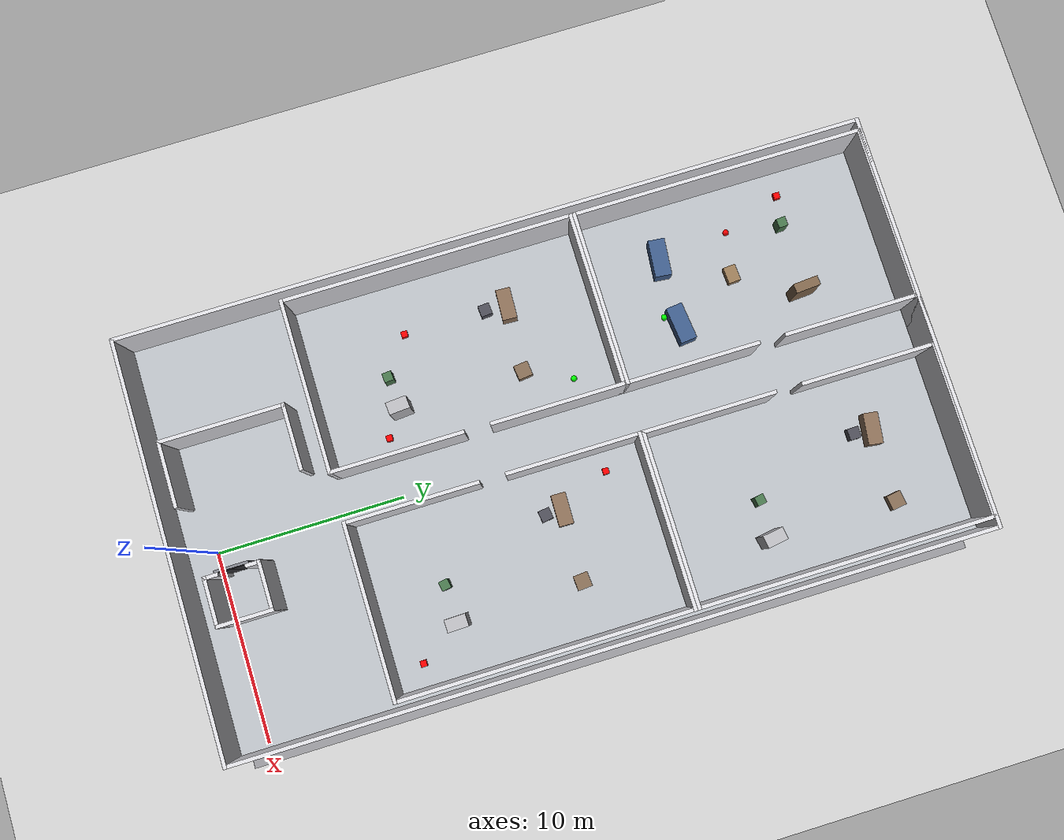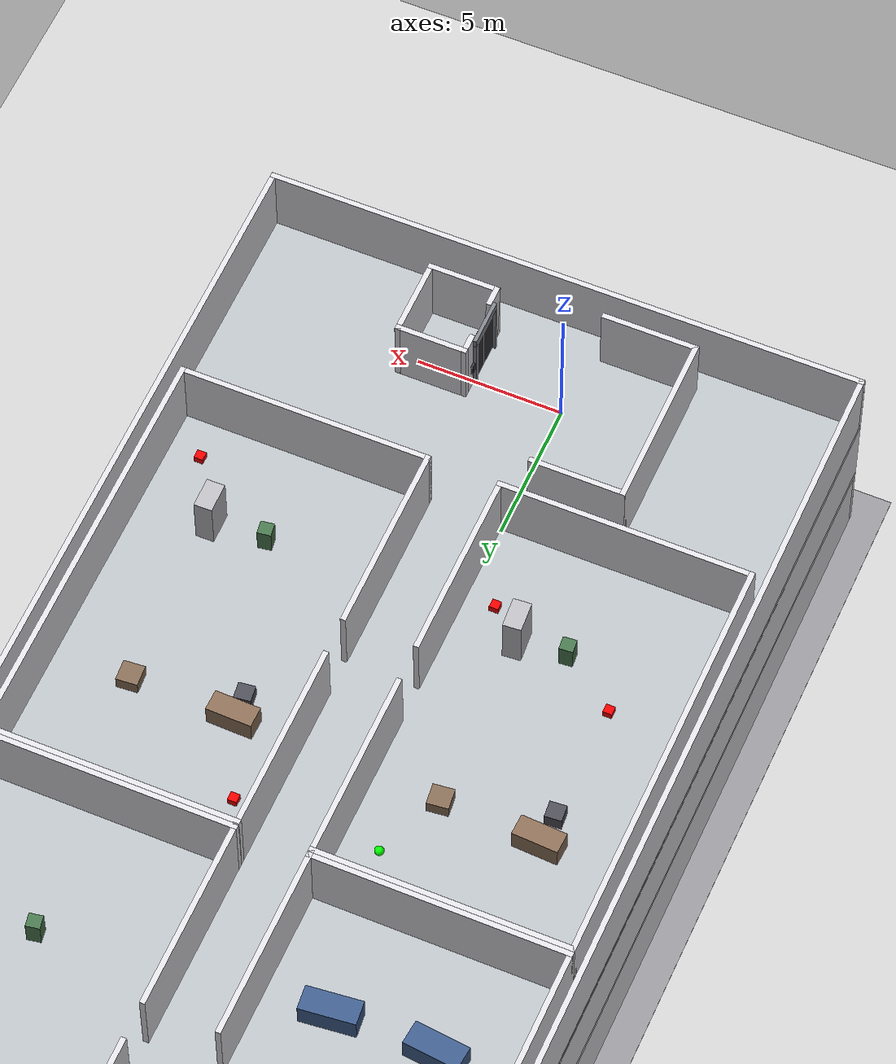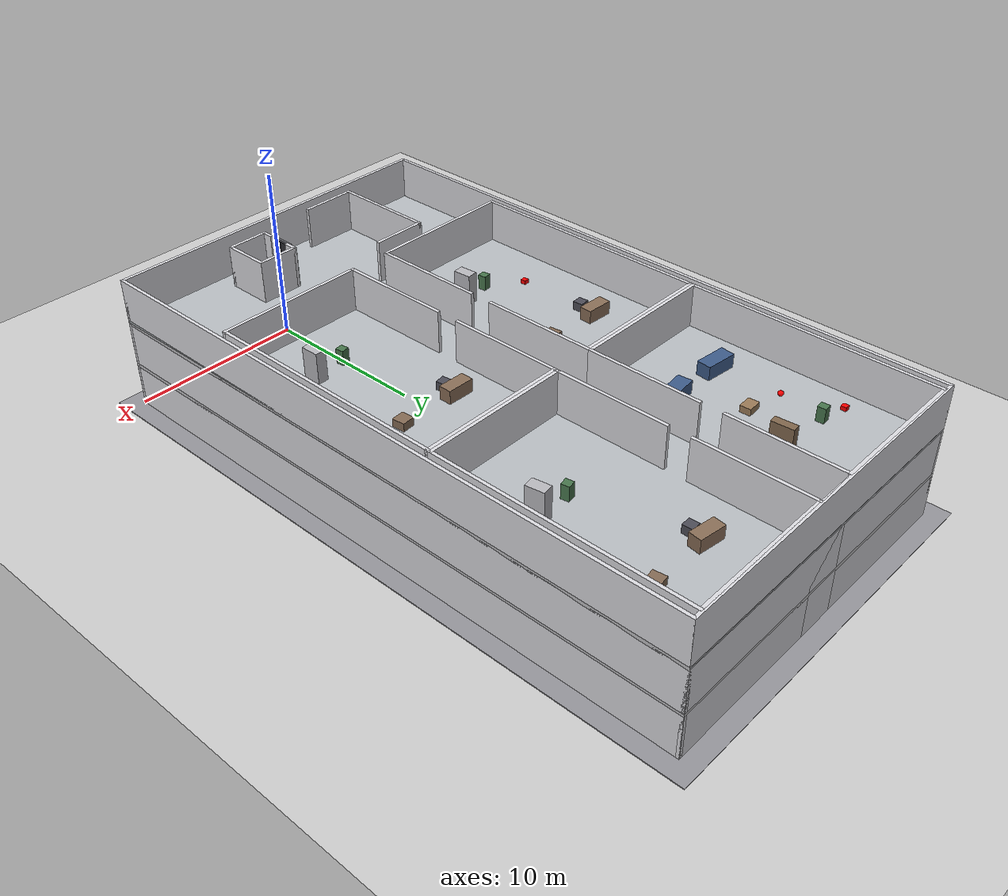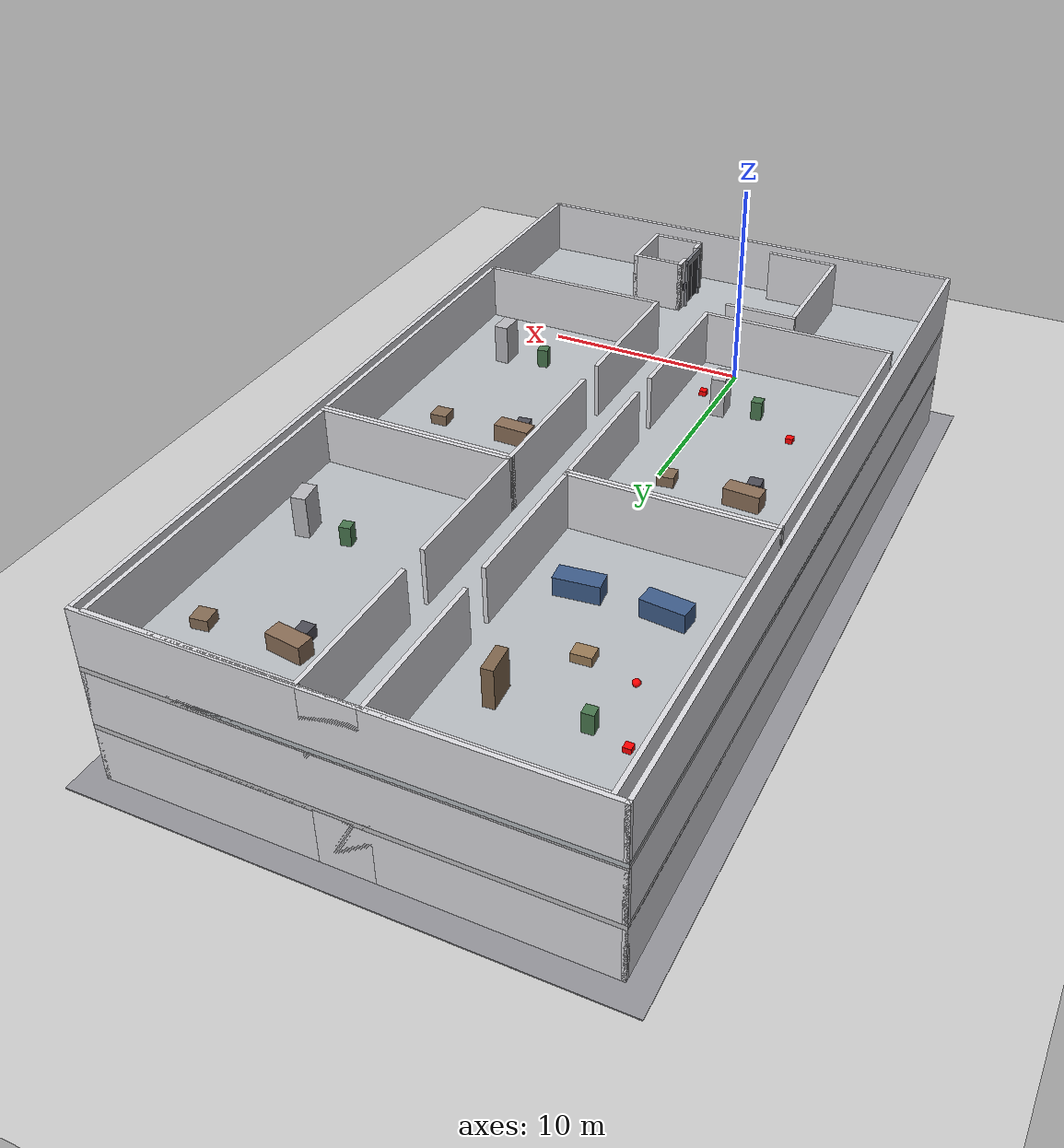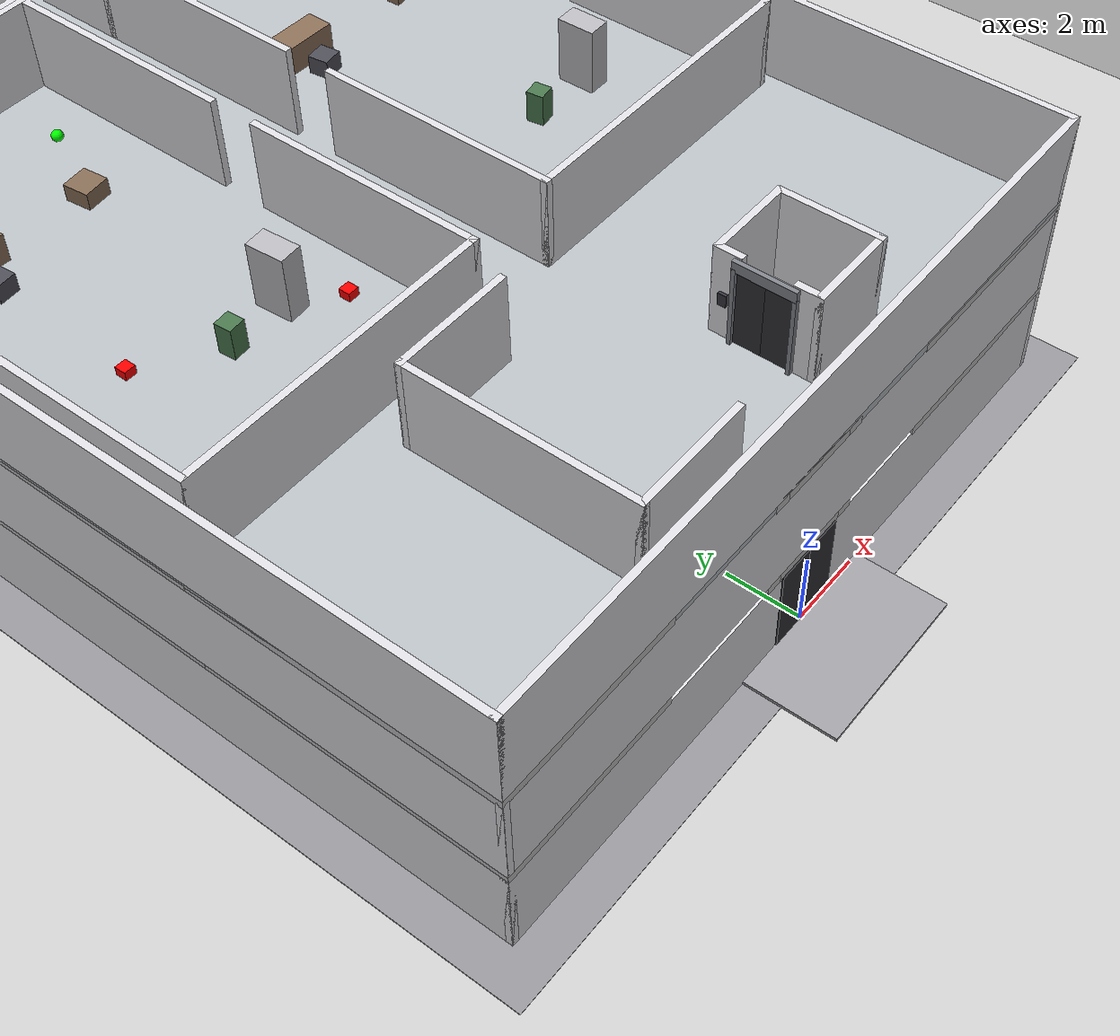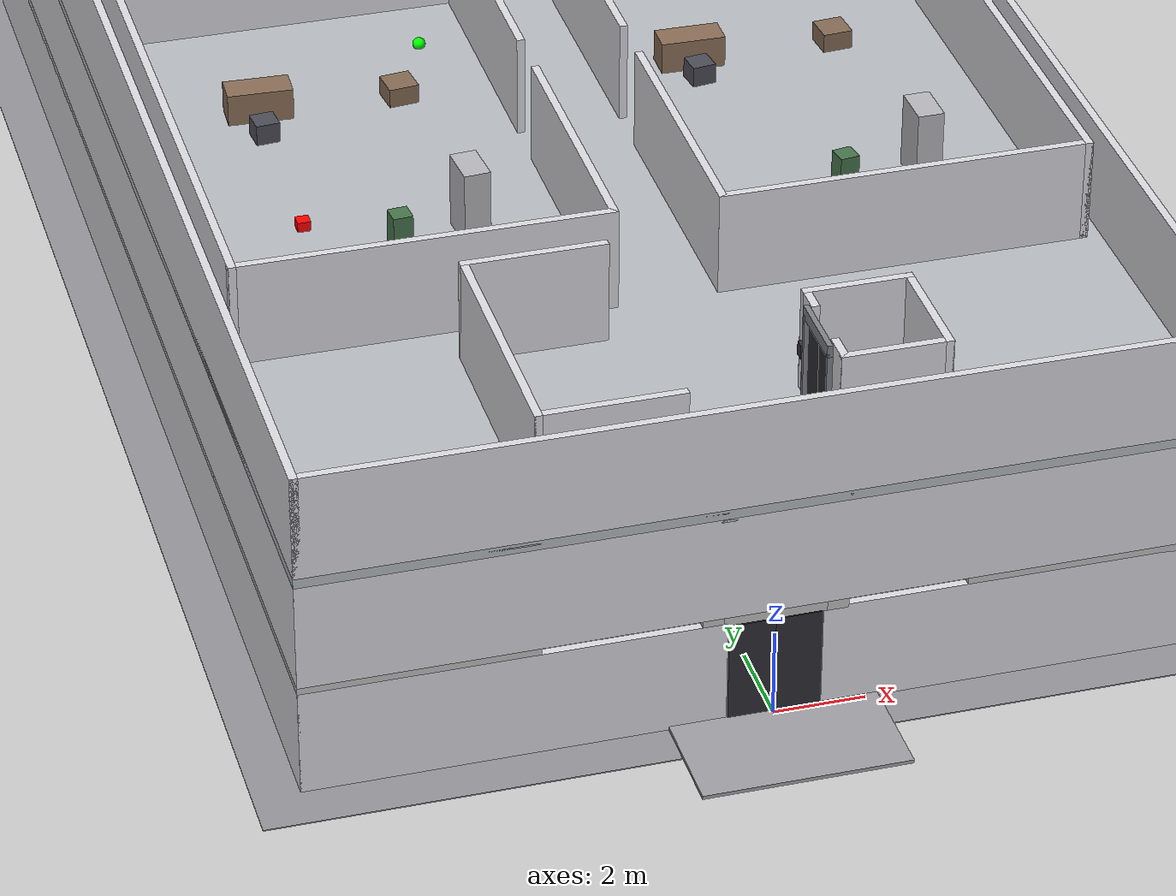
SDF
<?xml version='1.0' encoding='utf-8'?>
<sdf version="1.7">

  <world name="generated_world">

    <physics name="default_physics" default="0" type="ode">
      <max_step_size>0.001000</max_step_size>
      <real_time_factor>1.000000</real_time_factor>
      <real_time_update_rate>1000</real_time_update_rate>
      <gravity>0 0 -9.81</gravity>
      <ode>
        <solver>
          <type>quick</type>
          <iters>50</iters>
          <sor>1.3</sor>
        </solver>
        <constraints>
          <cfm>0.0</cfm>
          <erp>0.2</erp>
          <contact_max_correcting_vel>10.000000</contact_max_correcting_vel>
          <contact_surface_layer>0.001</contact_surface_layer>
        </constraints>
      </ode>
    </physics>
    <include>

      <uri>model://sun</uri>

    </include>

    <include>

      <uri>model://ground_plane</uri>

    </include>

    <model name="generated_building">
    <static>true</static>
    <pose>0 0 0 0 0 0</pose>
    <link name="foundation">
      <pose>0.0000 18.0000 -0.1500 0.0000 0.0000 0.0000</pose>
      <collision name="foundation_collision">
        <geometry>
          <box>
            <size>22.0000 38.0000 0.3000</size>
          </box>
        </geometry>
      </collision>
      <visual name="foundation_visual">
        <geometry>
          <box>
            <size>22.0000 38.0000 0.3000</size>
          </box>
        </geometry>
        <material>
          <ambient>0.58 0.58 0.60 1</ambient>
          <diffuse>0.58 0.58 0.60 1</diffuse>
        </material>
      </visual>
      <gravity>false</gravity>
    </link>
    <link name="entrance_apron">
      <pose>0.0000 -1.2000 0.0400 0.0000 0.0000 0.0000</pose>
      <collision name="entrance_apron_collision">
        <geometry>
          <box>
            <size>4.5000 2.4000 0.0800</size>
          </box>
        </geometry>
      </collision>
      <visual name="entrance_apron_visual">
        <geometry>
          <box>
            <size>4.5000 2.4000 0.0800</size>
          </box>
        </geometry>
        <material>
          <ambient>0.62 0.62 0.64 1</ambient>
          <diffuse>0.62 0.62 0.64 1</diffuse>
        </material>
      </visual>
      <gravity>false</gravity>
    </link>
    <link name="slab_floor_0_0">
      <pose>0.0000 21.9250 -0.1100 0.0000 0.0000 0.0000</pose>
      <collision name="slab_floor_0_0_collision">
        <geometry>
          <box>
            <size>20.0000 28.1500 0.2200</size>
          </box>
        </geometry>
      </collision>
      <visual name="slab_floor_0_0_visual">
        <geometry>
          <box>
            <size>20.0000 28.1500 0.2200</size>
          </box>
        </geometry>
        <material>
          <ambient>0.76 0.76 0.77 1</ambient>
          <diffuse>0.76 0.76 0.77 1</diffuse>
        </material>
      </visual>
      <gravity>false</gravity>
    </link>
    <link name="slab_floor_0_1">
      <pose>-7.4700 3.9250 -0.1100 0.0000 0.0000 0.0000</pose>
      <collision name="slab_floor_0_1_collision">
        <geometry>
          <box>
            <size>5.0600 7.8500 0.2200</size>
          </box>
        </geometry>
      </collision>
      <visual name="slab_floor_0_1_visual">
        <geometry>
          <box>
            <size>5.0600 7.8500 0.2200</size>
          </box>
        </geometry>
        <material>
          <ambient>0.76 0.76 0.77 1</ambient>
          <diffuse>0.76 0.76 0.77 1</diffuse>
        </material>
      </visual>
      <gravity>false</gravity>
    </link>
    <link name="slab_floor_0_2">
      <pose>-1.3300 3.9250 -0.1100 0.0000 0.0000 0.0000</pose>
      <collision name="slab_floor_0_2_collision">
        <geometry>
          <box>
            <size>0.4600 7.8500 0.2200</size>
          </box>
        </geometry>
      </collision>
      <visual name="slab_floor_0_2_visual">
        <geometry>
          <box>
            <size>0.4600 7.8500 0.2200</size>
          </box>
        </geometry>
        <material>
          <ambient>0.76 0.76 0.77 1</ambient>
          <diffuse>0.76 0.76 0.77 1</diffuse>
        </material>
      </visual>
      <gravity>false</gravity>
    </link>
    <link name="slab_floor_0_3">
      <pose>0.0000 3.9250 -0.1100 0.0000 0.0000 0.0000</pose>
      <collision name="slab_floor_0_3_collision">
        <geometry>
          <box>
            <size>2.2000 7.8500 0.2200</size>
          </box>
        </geometry>
      </collision>
      <visual name="slab_floor_0_3_visual">
        <geometry>
          <box>
            <size>2.2000 7.8500 0.2200</size>
          </box>
        </geometry>
        <material>
          <ambient>0.76 0.76 0.77 1</ambient>
          <diffuse>0.76 0.76 0.77 1</diffuse>
        </material>
      </visual>
      <gravity>false</gravity>
    </link>
    <link name="slab_floor_0_4">
      <pose>1.3300 3.9250 -0.1100 0.0000 0.0000 0.0000</pose>
      <collision name="slab_floor_0_4_collision">
        <geometry>
          <box>
            <size>0.4600 7.8500 0.2200</size>
          </box>
        </geometry>
      </collision>
      <visual name="slab_floor_0_4_visual">
        <geometry>
          <box>
            <size>0.4600 7.8500 0.2200</size>
          </box>
        </geometry>
        <material>
          <ambient>0.76 0.76 0.77 1</ambient>
          <diffuse>0.76 0.76 0.77 1</diffuse>
        </material>
      </visual>
      <gravity>false</gravity>
    </link>
    <link name="slab_floor_0_5">
      <pose>7.0700 3.9250 -0.1100 0.0000 0.0000 0.0000</pose>
      <collision name="slab_floor_0_5_collision">
        <geometry>
          <box>
            <size>5.8600 7.8500 0.2200</size>
          </box>
        </geometry>
      </collision>
      <visual name="slab_floor_0_5_visual">
        <geometry>
          <box>
            <size>5.8600 7.8500 0.2200</size>
          </box>
        </geometry>
        <material>
          <ambient>0.76 0.76 0.77 1</ambient>
          <diffuse>0.76 0.76 0.77 1</diffuse>
        </material>
      </visual>
      <gravity>false</gravity>
    </link>
    <link name="stair_edge_infill_floor_0">
      <pose>-1.6500 3.8500 -0.1100 0.0000 0.0000 0.0000</pose>
      <collision name="stair_edge_infill_floor_0_collision">
        <geometry>
          <box>
            <size>0.1800 6.0000 0.2200</size>
          </box>
        </geometry>
      </collision>
      <visual name="stair_edge_infill_floor_0_visual">
        <geometry>
          <box>
            <size>0.1800 6.0000 0.2200</size>
          </box>
        </geometry>
        <material>
          <ambient>0.76 0.76 0.77 1</ambient>
          <diffuse>0.76 0.76 0.77 1</diffuse>
        </material>
      </visual>
      <gravity>false</gravity>
    </link>
    <link name="exterior_west_floor_0">
      <pose>-9.9100 18.0000 1.2250 0.0000 0.0000 0.0000</pose>
      <collision name="exterior_west_floor_0_collision">
        <geometry>
          <box>
            <size>0.1800 36.0000 2.4500</size>
          </box>
        </geometry>
      </collision>
      <visual name="exterior_west_floor_0_visual">
        <geometry>
          <box>
            <size>0.1800 36.0000 2.4500</size>
          </box>
        </geometry>
        <material>
          <ambient>0.86 0.86 0.88 1</ambient>
          <diffuse>0.86 0.86 0.88 1</diffuse>
        </material>
      </visual>
      <gravity>false</gravity>
    </link>
    <link name="exterior_east_floor_0">
      <pose>9.9100 18.0000 1.2250 0.0000 0.0000 0.0000</pose>
      <collision name="exterior_east_floor_0_collision">
        <geometry>
          <box>
            <size>0.1800 36.0000 2.4500</size>
          </box>
        </geometry>
      </collision>
      <visual name="exterior_east_floor_0_visual">
        <geometry>
          <box>
            <size>0.1800 36.0000 2.4500</size>
          </box>
        </geometry>
        <material>
          <ambient>0.86 0.86 0.88 1</ambient>
          <diffuse>0.86 0.86 0.88 1</diffuse>
        </material>
      </visual>
      <gravity>false</gravity>
    </link>
    <link name="exterior_north_floor_0">
      <pose>0.0000 35.9100 1.2250 0.0000 0.0000 0.0000</pose>
      <collision name="exterior_north_floor_0_collision">
        <geometry>
          <box>
            <size>20.0000 0.1800 2.4500</size>
          </box>
        </geometry>
      </collision>
      <visual name="exterior_north_floor_0_visual">
        <geometry>
          <box>
            <size>20.0000 0.1800 2.4500</size>
          </box>
        </geometry>
        <material>
          <ambient>0.86 0.86 0.88 1</ambient>
          <diffuse>0.86 0.86 0.88 1</diffuse>
        </material>
      </visual>
      <gravity>false</gravity>
    </link>
    <link name="exterior_south_entrance_left">
      <pose>-5.5100 0.0900 1.2250 0.0000 0.0000 0.0000</pose>
      <collision name="exterior_south_entrance_left_collision">
        <geometry>
          <box>
            <size>8.9800 0.1800 2.4500</size>
          </box>
        </geometry>
      </collision>
      <visual name="exterior_south_entrance_left_visual">
        <geometry>
          <box>
            <size>8.9800 0.1800 2.4500</size>
          </box>
        </geometry>
        <material>
          <ambient>0.86 0.86 0.88 1</ambient>
          <diffuse>0.86 0.86 0.88 1</diffuse>
        </material>
      </visual>
      <gravity>false</gravity>
    </link>
    <link name="exterior_south_entrance_right">
      <pose>5.5100 0.0900 1.2250 0.0000 0.0000 0.0000</pose>
      <collision name="exterior_south_entrance_right_collision">
        <geometry>
          <box>
            <size>8.9800 0.1800 2.4500</size>
          </box>
        </geometry>
      </collision>
      <visual name="exterior_south_entrance_right_visual">
        <geometry>
          <box>
            <size>8.9800 0.1800 2.4500</size>
          </box>
        </geometry>
        <material>
          <ambient>0.86 0.86 0.88 1</ambient>
          <diffuse>0.86 0.86 0.88 1</diffuse>
        </material>
      </visual>
      <gravity>false</gravity>
    </link>
    <link name="north_end_wall_floor_0">
      <pose>0.0000 35.9100 1.2250 0.0000 0.0000 0.0000</pose>
      <collision name="north_end_wall_floor_0_collision">
        <geometry>
          <box>
            <size>2.2000 0.1800 2.4500</size>
          </box>
        </geometry>
      </collision>
      <visual name="north_end_wall_floor_0_visual">
        <geometry>
          <box>
            <size>2.2000 0.1800 2.4500</size>
          </box>
        </geometry>
        <material>
          <ambient>0.86 0.86 0.88 1</ambient>
          <diffuse>0.86 0.86 0.88 1</diffuse>
        </material>
      </visual>
      <gravity>false</gravity>
    </link>
    <link name="floor_0_room_0_corridor_wall_lower">
      <pose>-1.1900 11.0575 1.2250 0.0000 0.0000 0.0000</pose>
      <collision name="floor_0_room_0_corridor_wall_lower_collision">
        <geometry>
          <box>
            <size>0.1800 6.4150 2.4500</size>
          </box>
        </geometry>
      </collision>
      <visual name="floor_0_room_0_corridor_wall_lower_visual">
        <geometry>
          <box>
            <size>0.1800 6.4150 2.4500</size>
          </box>
        </geometry>
        <material>
          <ambient>0.86 0.86 0.88 1</ambient>
          <diffuse>0.86 0.86 0.88 1</diffuse>
        </material>
      </visual>
      <gravity>false</gravity>
    </link>
    <link name="floor_0_room_0_corridor_wall_upper">
      <pose>-1.1900 18.6725 1.2250 0.0000 0.0000 0.0000</pose>
      <collision name="floor_0_room_0_corridor_wall_upper_collision">
        <geometry>
          <box>
            <size>0.1800 6.4150 2.4500</size>
          </box>
        </geometry>
      </collision>
      <visual name="floor_0_room_0_corridor_wall_upper_visual">
        <geometry>
          <box>
            <size>0.1800 6.4150 2.4500</size>
          </box>
        </geometry>
        <material>
          <ambient>0.86 0.86 0.88 1</ambient>
          <diffuse>0.86 0.86 0.88 1</diffuse>
        </material>
      </visual>
      <gravity>false</gravity>
    </link>
    <link name="floor_0_room_0_west_wall">
      <pose>-9.4100 14.8650 1.2250 0.0000 0.0000 0.0000</pose>
      <collision name="floor_0_room_0_west_wall_collision">
        <geometry>
          <box>
            <size>0.1800 14.0300 2.4500</size>
          </box>
        </geometry>
      </collision>
      <visual name="floor_0_room_0_west_wall_visual">
        <geometry>
          <box>
            <size>0.1800 14.0300 2.4500</size>
          </box>
        </geometry>
        <material>
          <ambient>0.86 0.86 0.88 1</ambient>
          <diffuse>0.86 0.86 0.88 1</diffuse>
        </material>
      </visual>
      <gravity>false</gravity>
    </link>
    <link name="floor_0_room_0_south_wall">
      <pose>-5.3000 7.9400 1.2250 0.0000 0.0000 0.0000</pose>
      <collision name="floor_0_room_0_south_wall_collision">
        <geometry>
          <box>
            <size>8.4000 0.1800 2.4500</size>
          </box>
        </geometry>
      </collision>
      <visual name="floor_0_room_0_south_wall_visual">
        <geometry>
          <box>
            <size>8.4000 0.1800 2.4500</size>
          </box>
        </geometry>
        <material>
          <ambient>0.86 0.86 0.88 1</ambient>
          <diffuse>0.86 0.86 0.88 1</diffuse>
        </material>
      </visual>
      <gravity>false</gravity>
    </link>
    <link name="floor_0_room_0_north_wall">
      <pose>-5.3000 21.7900 1.2250 0.0000 0.0000 0.0000</pose>
      <collision name="floor_0_room_0_north_wall_collision">
        <geometry>
          <box>
            <size>8.4000 0.1800 2.4500</size>
          </box>
        </geometry>
      </collision>
      <visual name="floor_0_room_0_north_wall_visual">
        <geometry>
          <box>
            <size>8.4000 0.1800 2.4500</size>
          </box>
        </geometry>
        <material>
          <ambient>0.86 0.86 0.88 1</ambient>
          <diffuse>0.86 0.86 0.88 1</diffuse>
        </material>
      </visual>
      <gravity>false</gravity>
    </link>
    <link name="floor_0_room_1_corridor_wall_lower">
      <pose>1.1900 11.0575 1.2250 0.0000 0.0000 0.0000</pose>
      <collision name="floor_0_room_1_corridor_wall_lower_collision">
        <geometry>
          <box>
            <size>0.1800 6.4150 2.4500</size>
          </box>
        </geometry>
      </collision>
      <visual name="floor_0_room_1_corridor_wall_lower_visual">
        <geometry>
          <box>
            <size>0.1800 6.4150 2.4500</size>
          </box>
        </geometry>
        <material>
          <ambient>0.86 0.86 0.88 1</ambient>
          <diffuse>0.86 0.86 0.88 1</diffuse>
        </material>
      </visual>
      <gravity>false</gravity>
    </link>
    <link name="floor_0_room_1_corridor_wall_upper">
      <pose>1.1900 18.6725 1.2250 0.0000 0.0000 0.0000</pose>
      <collision name="floor_0_room_1_corridor_wall_upper_collision">
        <geometry>
          <box>
            <size>0.1800 6.4150 2.4500</size>
          </box>
        </geometry>
      </collision>
      <visual name="floor_0_room_1_corridor_wall_upper_visual">
        <geometry>
          <box>
            <size>0.1800 6.4150 2.4500</size>
          </box>
        </geometry>
        <material>
          <ambient>0.86 0.86 0.88 1</ambient>
          <diffuse>0.86 0.86 0.88 1</diffuse>
        </material>
      </visual>
      <gravity>false</gravity>
    </link>
    <link name="floor_0_room_1_east_wall">
      <pose>9.4100 14.8650 1.2250 0.0000 0.0000 0.0000</pose>
      <collision name="floor_0_room_1_east_wall_collision">
        <geometry>
          <box>
            <size>0.1800 14.0300 2.4500</size>
          </box>
        </geometry>
      </collision>
      <visual name="floor_0_room_1_east_wall_visual">
        <geometry>
          <box>
            <size>0.1800 14.0300 2.4500</size>
          </box>
        </geometry>
        <material>
          <ambient>0.86 0.86 0.88 1</ambient>
          <diffuse>0.86 0.86 0.88 1</diffuse>
        </material>
      </visual>
      <gravity>false</gravity>
    </link>
    <link name="floor_0_room_1_south_wall">
      <pose>5.3000 7.9400 1.2250 0.0000 0.0000 0.0000</pose>
      <collision name="floor_0_room_1_south_wall_collision">
        <geometry>
          <box>
            <size>8.4000 0.1800 2.4500</size>
          </box>
        </geometry>
      </collision>
      <visual name="floor_0_room_1_south_wall_visual">
        <geometry>
          <box>
            <size>8.4000 0.1800 2.4500</size>
          </box>
        </geometry>
        <material>
          <ambient>0.86 0.86 0.88 1</ambient>
          <diffuse>0.86 0.86 0.88 1</diffuse>
        </material>
      </visual>
      <gravity>false</gravity>
    </link>
    <link name="floor_0_room_1_north_wall">
      <pose>5.3000 21.7900 1.2250 0.0000 0.0000 0.0000</pose>
      <collision name="floor_0_room_1_north_wall_collision">
        <geometry>
          <box>
            <size>8.4000 0.1800 2.4500</size>
          </box>
        </geometry>
      </collision>
      <visual name="floor_0_room_1_north_wall_visual">
        <geometry>
          <box>
            <size>8.4000 0.1800 2.4500</size>
          </box>
        </geometry>
        <material>
          <ambient>0.86 0.86 0.88 1</ambient>
          <diffuse>0.86 0.86 0.88 1</diffuse>
        </material>
      </visual>
      <gravity>false</gravity>
    </link>
    <link name="floor_0_room_2_corridor_wall_lower">
      <pose>-1.1900 25.0875 1.2250 0.0000 0.0000 0.0000</pose>
      <collision name="floor_0_room_2_corridor_wall_lower_collision">
        <geometry>
          <box>
            <size>0.1800 6.4150 2.4500</size>
          </box>
        </geometry>
      </collision>
      <visual name="floor_0_room_2_corridor_wall_lower_visual">
        <geometry>
          <box>
            <size>0.1800 6.4150 2.4500</size>
          </box>
        </geometry>
        <material>
          <ambient>0.86 0.86 0.88 1</ambient>
          <diffuse>0.86 0.86 0.88 1</diffuse>
        </material>
      </visual>
      <gravity>false</gravity>
    </link>
    <link name="floor_0_room_2_corridor_wall_upper">
      <pose>-1.1900 32.7025 1.2250 0.0000 0.0000 0.0000</pose>
      <collision name="floor_0_room_2_corridor_wall_upper_collision">
        <geometry>
          <box>
            <size>0.1800 6.4150 2.4500</size>
          </box>
        </geometry>
      </collision>
      <visual name="floor_0_room_2_corridor_wall_upper_visual">
        <geometry>
          <box>
            <size>0.1800 6.4150 2.4500</size>
          </box>
        </geometry>
        <material>
          <ambient>0.86 0.86 0.88 1</ambient>
          <diffuse>0.86 0.86 0.88 1</diffuse>
        </material>
      </visual>
      <gravity>false</gravity>
    </link>
    <link name="floor_0_room_2_west_wall">
      <pose>-9.4100 28.8950 1.2250 0.0000 0.0000 0.0000</pose>
      <collision name="floor_0_room_2_west_wall_collision">
        <geometry>
          <box>
            <size>0.1800 14.0300 2.4500</size>
          </box>
        </geometry>
      </collision>
      <visual name="floor_0_room_2_west_wall_visual">
        <geometry>
          <box>
            <size>0.1800 14.0300 2.4500</size>
          </box>
        </geometry>
        <material>
          <ambient>0.86 0.86 0.88 1</ambient>
          <diffuse>0.86 0.86 0.88 1</diffuse>
        </material>
      </visual>
      <gravity>false</gravity>
    </link>
    <link name="floor_0_room_2_south_wall">
      <pose>-5.3000 21.9700 1.2250 0.0000 0.0000 0.0000</pose>
      <collision name="floor_0_room_2_south_wall_collision">
        <geometry>
          <box>
            <size>8.4000 0.1800 2.4500</size>
          </box>
        </geometry>
      </collision>
      <visual name="floor_0_room_2_south_wall_visual">
        <geometry>
          <box>
            <size>8.4000 0.1800 2.4500</size>
          </box>
        </geometry>
        <material>
          <ambient>0.86 0.86 0.88 1</ambient>
          <diffuse>0.86 0.86 0.88 1</diffuse>
        </material>
      </visual>
      <gravity>false</gravity>
    </link>
    <link name="floor_0_room_2_north_wall">
      <pose>-5.3000 35.8200 1.2250 0.0000 0.0000 0.0000</pose>
      <collision name="floor_0_room_2_north_wall_collision">
        <geometry>
          <box>
            <size>8.4000 0.1800 2.4500</size>
          </box>
        </geometry>
      </collision>
      <visual name="floor_0_room_2_north_wall_visual">
        <geometry>
          <box>
            <size>8.4000 0.1800 2.4500</size>
          </box>
        </geometry>
        <material>
          <ambient>0.86 0.86 0.88 1</ambient>
          <diffuse>0.86 0.86 0.88 1</diffuse>
        </material>
      </visual>
      <gravity>false</gravity>
    </link>
    <link name="floor_0_room_3_corridor_wall_lower">
      <pose>1.1900 25.0875 1.2250 0.0000 0.0000 0.0000</pose>
      <collision name="floor_0_room_3_corridor_wall_lower_collision">
        <geometry>
          <box>
            <size>0.1800 6.4150 2.4500</size>
          </box>
        </geometry>
      </collision>
      <visual name="floor_0_room_3_corridor_wall_lower_visual">
        <geometry>
          <box>
            <size>0.1800 6.4150 2.4500</size>
          </box>
        </geometry>
        <material>
          <ambient>0.86 0.86 0.88 1</ambient>
          <diffuse>0.86 0.86 0.88 1</diffuse>
        </material>
      </visual>
      <gravity>false</gravity>
    </link>
    <link name="floor_0_room_3_corridor_wall_upper">
      <pose>1.1900 32.7025 1.2250 0.0000 0.0000 0.0000</pose>
      <collision name="floor_0_room_3_corridor_wall_upper_collision">
        <geometry>
          <box>
            <size>0.1800 6.4150 2.4500</size>
          </box>
        </geometry>
      </collision>
      <visual name="floor_0_room_3_corridor_wall_upper_visual">
        <geometry>
          <box>
            <size>0.1800 6.4150 2.4500</size>
          </box>
        </geometry>
        <material>
          <ambient>0.86 0.86 0.88 1</ambient>
          <diffuse>0.86 0.86 0.88 1</diffuse>
        </material>
      </visual>
      <gravity>false</gravity>
    </link>
    <link name="floor_0_room_3_east_wall">
      <pose>9.4100 28.8950 1.2250 0.0000 0.0000 0.0000</pose>
      <collision name="floor_0_room_3_east_wall_collision">
        <geometry>
          <box>
            <size>0.1800 14.0300 2.4500</size>
          </box>
        </geometry>
      </collision>
      <visual name="floor_0_room_3_east_wall_visual">
        <geometry>
          <box>
            <size>0.1800 14.0300 2.4500</size>
          </box>
        </geometry>
        <material>
          <ambient>0.86 0.86 0.88 1</ambient>
          <diffuse>0.86 0.86 0.88 1</diffuse>
        </material>
      </visual>
      <gravity>false</gravity>
    </link>
    <link name="floor_0_room_3_south_wall">
      <pose>5.3000 21.9700 1.2250 0.0000 0.0000 0.0000</pose>
      <collision name="floor_0_room_3_south_wall_collision">
        <geometry>
          <box>
            <size>8.4000 0.1800 2.4500</size>
          </box>
        </geometry>
      </collision>
      <visual name="floor_0_room_3_south_wall_visual">
        <geometry>
          <box>
            <size>8.4000 0.1800 2.4500</size>
          </box>
        </geometry>
        <material>
          <ambient>0.86 0.86 0.88 1</ambient>
          <diffuse>0.86 0.86 0.88 1</diffuse>
        </material>
      </visual>
      <gravity>false</gravity>
    </link>
    <link name="floor_0_room_3_north_wall">
      <pose>5.3000 35.8200 1.2250 0.0000 0.0000 0.0000</pose>
      <collision name="floor_0_room_3_north_wall_collision">
        <geometry>
          <box>
            <size>8.4000 0.1800 2.4500</size>
          </box>
        </geometry>
      </collision>
      <visual name="floor_0_room_3_north_wall_visual">
        <geometry>
          <box>
            <size>8.4000 0.1800 2.4500</size>
          </box>
        </geometry>
        <material>
          <ambient>0.86 0.86 0.88 1</ambient>
          <diffuse>0.86 0.86 0.88 1</diffuse>
        </material>
      </visual>
      <gravity>false</gravity>
    </link>
    <link name="stair_core_floor_0_west">
      <pose>-4.7600 3.8500 1.2250 0.0000 0.0000 0.0000</pose>
      <collision name="stair_core_floor_0_west_collision">
        <geometry>
          <box>
            <size>0.1800 6.0000 2.4500</size>
          </box>
        </geometry>
      </collision>
      <visual name="stair_core_floor_0_west_visual">
        <geometry>
          <box>
            <size>0.1800 6.0000 2.4500</size>
          </box>
        </geometry>
        <material>
          <ambient>0.86 0.86 0.88 1</ambient>
          <diffuse>0.86 0.86 0.88 1</diffuse>
        </material>
      </visual>
      <gravity>false</gravity>
    </link>
    <link name="stair_core_floor_0_south">
      <pose>-3.2500 0.9400 1.2250 0.0000 0.0000 0.0000</pose>
      <collision name="stair_core_floor_0_south_collision">
        <geometry>
          <box>
            <size>3.2000 0.1800 2.4500</size>
          </box>
        </geometry>
      </collision>
      <visual name="stair_core_floor_0_south_visual">
        <geometry>
          <box>
            <size>3.2000 0.1800 2.4500</size>
          </box>
        </geometry>
        <material>
          <ambient>0.86 0.86 0.88 1</ambient>
          <diffuse>0.86 0.86 0.88 1</diffuse>
        </material>
      </visual>
      <gravity>false</gravity>
    </link>
    <link name="stair_core_floor_0_north">
      <pose>-3.2500 6.7600 1.2250 0.0000 0.0000 0.0000</pose>
      <collision name="stair_core_floor_0_north_collision">
        <geometry>
          <box>
            <size>3.2000 0.1800 2.4500</size>
          </box>
        </geometry>
      </collision>
      <visual name="stair_core_floor_0_north_visual">
        <geometry>
          <box>
            <size>3.2000 0.1800 2.4500</size>
          </box>
        </geometry>
        <material>
          <ambient>0.86 0.86 0.88 1</ambient>
          <diffuse>0.86 0.86 0.88 1</diffuse>
        </material>
      </visual>
      <gravity>false</gravity>
    </link>
    <link name="elevator_core_floor_0_west_lower">
      <pose>1.7400 1.6150 1.2250 0.0000 0.0000 0.0000</pose>
      <collision name="elevator_core_floor_0_west_lower_collision">
        <geometry>
          <box>
            <size>0.1800 0.7300 2.4500</size>
          </box>
        </geometry>
      </collision>
      <visual name="elevator_core_floor_0_west_lower_visual">
        <geometry>
          <box>
            <size>0.1800 0.7300 2.4500</size>
          </box>
        </geometry>
        <material>
          <ambient>0.86 0.86 0.88 1</ambient>
          <diffuse>0.86 0.86 0.88 1</diffuse>
        </material>
      </visual>
      <gravity>false</gravity>
    </link>
    <link name="elevator_core_floor_0_west_upper">
      <pose>1.7400 3.5850 1.2250 0.0000 0.0000 0.0000</pose>
      <collision name="elevator_core_floor_0_west_upper_collision">
        <geometry>
          <box>
            <size>0.1800 0.7300 2.4500</size>
          </box>
        </geometry>
      </collision>
      <visual name="elevator_core_floor_0_west_upper_visual">
        <geometry>
          <box>
            <size>0.1800 0.7300 2.4500</size>
          </box>
        </geometry>
        <material>
          <ambient>0.86 0.86 0.88 1</ambient>
          <diffuse>0.86 0.86 0.88 1</diffuse>
        </material>
      </visual>
      <gravity>false</gravity>
    </link>
    <link name="elevator_core_floor_0_east">
      <pose>3.9600 2.6000 1.2250 0.0000 0.0000 0.0000</pose>
      <collision name="elevator_core_floor_0_east_collision">
        <geometry>
          <box>
            <size>0.1800 2.7000 2.4500</size>
          </box>
        </geometry>
      </collision>
      <visual name="elevator_core_floor_0_east_visual">
        <geometry>
          <box>
            <size>0.1800 2.7000 2.4500</size>
          </box>
        </geometry>
        <material>
          <ambient>0.86 0.86 0.88 1</ambient>
          <diffuse>0.86 0.86 0.88 1</diffuse>
        </material>
      </visual>
      <gravity>false</gravity>
    </link>
    <link name="elevator_core_floor_0_south">
      <pose>2.8500 1.3400 1.2250 0.0000 0.0000 0.0000</pose>
      <collision name="elevator_core_floor_0_south_collision">
        <geometry>
          <box>
            <size>2.4000 0.1800 2.4500</size>
          </box>
        </geometry>
      </collision>
      <visual name="elevator_core_floor_0_south_visual">
        <geometry>
          <box>
            <size>2.4000 0.1800 2.4500</size>
          </box>
        </geometry>
        <material>
          <ambient>0.86 0.86 0.88 1</ambient>
          <diffuse>0.86 0.86 0.88 1</diffuse>
        </material>
      </visual>
      <gravity>false</gravity>
    </link>
    <link name="elevator_core_floor_0_north">
      <pose>2.8500 3.8600 1.2250 0.0000 0.0000 0.0000</pose>
      <collision name="elevator_core_floor_0_north_collision">
        <geometry>
          <box>
            <size>2.4000 0.1800 2.4500</size>
          </box>
        </geometry>
      </collision>
      <visual name="elevator_core_floor_0_north_visual">
        <geometry>
          <box>
            <size>2.4000 0.1800 2.4500</size>
          </box>
        </geometry>
        <material>
          <ambient>0.86 0.86 0.88 1</ambient>
          <diffuse>0.86 0.86 0.88 1</diffuse>
        </material>
      </visual>
      <gravity>false</gravity>
    </link>
    <link name="elevator_threshold_floor_0">
      <pose>1.5400 2.6000 0.0300 0.0000 0.0000 0.0000</pose>
      <collision name="elevator_threshold_floor_0_collision">
        <geometry>
          <box>
            <size>0.2200 1.5000 0.0600</size>
          </box>
        </geometry>
      </collision>
      <visual name="elevator_threshold_floor_0_visual">
        <geometry>
          <box>
            <size>0.2200 1.5000 0.0600</size>
          </box>
        </geometry>
        <material>
          <ambient>0.50 0.51 0.54 1</ambient>
          <diffuse>0.50 0.51 0.54 1</diffuse>
        </material>
      </visual>
      <gravity>false</gravity>
    </link>
    <link name="elevator_sill_infill_floor_0">
      <pose>1.6750 2.6000 -0.1100 0.0000 0.0000 0.0000</pose>
      <collision name="elevator_sill_infill_floor_0_collision">
        <geometry>
          <box>
            <size>0.0500 2.5200 0.2200</size>
          </box>
        </geometry>
      </collision>
      <visual name="elevator_sill_infill_floor_0_visual">
        <geometry>
          <box>
            <size>0.0500 2.5200 0.2200</size>
          </box>
        </geometry>
        <material>
          <ambient>0.72 0.72 0.73 1</ambient>
          <diffuse>0.72 0.72 0.73 1</diffuse>
        </material>
      </visual>
      <gravity>false</gravity>
    </link>
    <link name="elevator_header_floor_0">
      <pose>1.5900 2.6000 2.2600 0.0000 0.0000 0.0000</pose>
      <collision name="elevator_header_floor_0_collision">
        <geometry>
          <box>
            <size>0.1200 1.6000 0.2800</size>
          </box>
        </geometry>
      </collision>
      <visual name="elevator_header_floor_0_visual">
        <geometry>
          <box>
            <size>0.1200 1.6000 0.2800</size>
          </box>
        </geometry>
        <material>
          <ambient>0.50 0.51 0.54 1</ambient>
          <diffuse>0.50 0.51 0.54 1</diffuse>
        </material>
      </visual>
      <gravity>false</gravity>
    </link>
    <link name="elevator_jamb_left_floor_0">
      <pose>1.5900 1.8500 1.1000 0.0000 0.0000 0.0000</pose>
      <collision name="elevator_jamb_left_floor_0_collision">
        <geometry>
          <box>
            <size>0.1200 0.1000 2.2000</size>
          </box>
        </geometry>
      </collision>
      <visual name="elevator_jamb_left_floor_0_visual">
        <geometry>
          <box>
            <size>0.1200 0.1000 2.2000</size>
          </box>
        </geometry>
        <material>
          <ambient>0.50 0.51 0.54 1</ambient>
          <diffuse>0.50 0.51 0.54 1</diffuse>
        </material>
      </visual>
      <gravity>false</gravity>
    </link>
    <link name="elevator_jamb_right_floor_0">
      <pose>1.5900 3.3500 1.1000 0.0000 0.0000 0.0000</pose>
      <collision name="elevator_jamb_right_floor_0_collision">
        <geometry>
          <box>
            <size>0.1200 0.1000 2.2000</size>
          </box>
        </geometry>
      </collision>
      <visual name="elevator_jamb_right_floor_0_visual">
        <geometry>
          <box>
            <size>0.1200 0.1000 2.2000</size>
          </box>
        </geometry>
        <material>
          <ambient>0.50 0.51 0.54 1</ambient>
          <diffuse>0.50 0.51 0.54 1</diffuse>
        </material>
      </visual>
      <gravity>false</gravity>
    </link>
    <link name="elevator_call_panel_floor_0">
      <pose>1.5700 3.5800 1.2000 0.0000 0.0000 0.0000</pose>
      <collision name="elevator_call_panel_floor_0_collision">
        <geometry>
          <box>
            <size>0.0800 0.2200 0.3200</size>
          </box>
        </geometry>
      </collision>
      <visual name="elevator_call_panel_floor_0_visual">
        <geometry>
          <box>
            <size>0.0800 0.2200 0.3200</size>
          </box>
        </geometry>
        <material>
          <ambient>0.20 0.20 0.24 1</ambient>
          <diffuse>0.20 0.20 0.24 1</diffuse>
        </material>
      </visual>
      <gravity>false</gravity>
    </link>
    <link name="floor_0_room_0_desk">
      <pose>-7.09689446 18.6197399 0.45 0 0 0.107007869</pose>
      <collision name="floor_0_room_0_desk_collision">
        <geometry>
          <box>
            <size>1.5000 0.7000 0.7500</size>
          </box>
        </geometry>
      </collision>
      <visual name="floor_0_room_0_desk_visual">
        <geometry>
          <box>
            <size>1.5000 0.7000 0.7500</size>
          </box>
        </geometry>
        <material>
          <ambient>0.54 0.43 0.34 1</ambient>
          <diffuse>0.54 0.43 0.34 1</diffuse>
        </material>
      </visual>
      <gravity>false</gravity>
    </link>
    <link name="floor_0_room_0_chair">
      <pose>-7.04202012 17.6478418 0.28 0 0 0.0865985855</pose>
      <collision name="floor_0_room_0_chair_collision">
        <geometry>
          <box>
            <size>0.5500 0.5500 0.5500</size>
          </box>
        </geometry>
      </collision>
      <visual name="floor_0_room_0_chair_visual">
        <geometry>
          <box>
            <size>0.5500 0.5500 0.5500</size>
          </box>
        </geometry>
        <material>
          <ambient>0.30 0.30 0.34 1</ambient>
          <diffuse>0.30 0.30 0.34 1</diffuse>
        </material>
      </visual>
      <gravity>false</gravity>
    </link>
    <link name="floor_0_room_0_cabinet">
      <pose>-3.67033035 12.5012899 0.9 0 0 -0.0268373285</pose>
      <collision name="floor_0_room_0_cabinet_collision">
        <geometry>
          <box>
            <size>0.6000 1.0000 1.8000</size>
          </box>
        </geometry>
      </collision>
      <visual name="floor_0_room_0_cabinet_visual">
        <geometry>
          <box>
            <size>0.6000 1.0000 1.8000</size>
          </box>
        </geometry>
        <material>
          <ambient>0.72 0.72 0.74 1</ambient>
          <diffuse>0.72 0.72 0.74 1</diffuse>
        </material>
      </visual>
      <gravity>false</gravity>
    </link>
    <link name="floor_0_room_0_side_table">
      <pose>-3.73748459 18.5180826 0.32 0 0 -0.0451179216</pose>
      <collision name="floor_0_room_0_side_table_collision">
        <geometry>
          <box>
            <size>0.7000 0.7000 0.4500</size>
          </box>
        </geometry>
      </collision>
      <visual name="floor_0_room_0_side_table_visual">
        <geometry>
          <box>
            <size>0.7000 0.7000 0.4500</size>
          </box>
        </geometry>
        <material>
          <ambient>0.52 0.42 0.33 1</ambient>
          <diffuse>0.52 0.42 0.33 1</diffuse>
        </material>
      </visual>
      <gravity>false</gravity>
    </link>
    <link name="floor_0_room_0_planter">
      <pose>-5.36343219 12.3276635 0.45 0 0 0.0756690509</pose>
      <collision name="floor_0_room_0_planter_collision">
        <geometry>
          <box>
            <size>0.4500 0.4500 0.9000</size>
          </box>
        </geometry>
      </collision>
      <visual name="floor_0_room_0_planter_visual">
        <geometry>
          <box>
            <size>0.4500 0.4500 0.9000</size>
          </box>
        </geometry>
        <material>
          <ambient>0.28 0.46 0.30 1</ambient>
          <diffuse>0.28 0.46 0.30 1</diffuse>
        </material>
      </visual>
      <gravity>false</gravity>
    </link>
    <link name="floor_0_room_1_table">
      <pose>5.22760665 14.9086798 0.45 0 0 0.164572695</pose>
      <collision name="floor_0_room_1_table_collision">
        <geometry>
          <box>
            <size>2.2000 1.0000 0.7500</size>
          </box>
        </geometry>
      </collision>
      <visual name="floor_0_room_1_table_visual">
        <geometry>
          <box>
            <size>2.2000 1.0000 0.7500</size>
          </box>
        </geometry>
        <material>
          <ambient>0.50 0.38 0.28 1</ambient>
          <diffuse>0.50 0.38 0.28 1</diffuse>
        </material>
      </visual>
      <gravity>false</gravity>
    </link>
    <link name="floor_0_room_1_chair_north">
      <pose>5.08887748 18.1316608 0.28 0 0 -0.0657700177</pose>
      <collision name="floor_0_room_1_chair_north_collision">
        <geometry>
          <box>
            <size>0.5000 0.5000 0.5500</size>
          </box>
        </geometry>
      </collision>
      <visual name="floor_0_room_1_chair_north_visual">
        <geometry>
          <box>
            <size>0.5000 0.5000 0.5500</size>
          </box>
        </geometry>
        <material>
          <ambient>0.30 0.30 0.34 1</ambient>
          <diffuse>0.30 0.30 0.34 1</diffuse>
        </material>
      </visual>
      <gravity>false</gravity>
    </link>
    <link name="floor_0_room_1_chair_south">
      <pose>5.04622161 11.8723677 0.28 0 0 0.085724435</pose>
      <collision name="floor_0_room_1_chair_south_collision">
        <geometry>
          <box>
            <size>0.5000 0.5000 0.5500</size>
          </box>
        </geometry>
      </collision>
      <visual name="floor_0_room_1_chair_south_visual">
        <geometry>
          <box>
            <size>0.5000 0.5000 0.5500</size>
          </box>
        </geometry>
        <material>
          <ambient>0.30 0.30 0.34 1</ambient>
          <diffuse>0.30 0.30 0.34 1</diffuse>
        </material>
      </visual>
      <gravity>false</gravity>
    </link>
    <link name="floor_0_room_1_chair_west">
      <pose>3.13310465 14.9353807 0.28 0 0 1.55535222</pose>
      <collision name="floor_0_room_1_chair_west_collision">
        <geometry>
          <box>
            <size>0.5000 0.5000 0.5500</size>
          </box>
        </geometry>
      </collision>
      <visual name="floor_0_room_1_chair_west_visual">
        <geometry>
          <box>
            <size>0.5000 0.5000 0.5500</size>
          </box>
        </geometry>
        <material>
          <ambient>0.30 0.30 0.34 1</ambient>
          <diffuse>0.30 0.30 0.34 1</diffuse>
        </material>
      </visual>
      <gravity>false</gravity>
    </link>
    <link name="floor_0_room_1_chair_east">
      <pose>7.31700894 15.0322327 0.28 0 0 1.6106433</pose>
      <collision name="floor_0_room_1_chair_east_collision">
        <geometry>
          <box>
            <size>0.5000 0.5000 0.5500</size>
          </box>
        </geometry>
      </collision>
      <visual name="floor_0_room_1_chair_east_visual">
        <geometry>
          <box>
            <size>0.5000 0.5000 0.5500</size>
          </box>
        </geometry>
        <material>
          <ambient>0.30 0.30 0.34 1</ambient>
          <diffuse>0.30 0.30 0.34 1</diffuse>
        </material>
      </visual>
      <gravity>false</gravity>
    </link>
    <link name="floor_0_room_1_credenza">
      <pose>6.79521542 12.0195021 0.45 0 0 -0.123678274</pose>
      <collision name="floor_0_room_1_credenza_collision">
        <geometry>
          <box>
            <size>1.2000 0.4500 0.9000</size>
          </box>
        </geometry>
      </collision>
      <visual name="floor_0_room_1_credenza_visual">
        <geometry>
          <box>
            <size>1.2000 0.4500 0.9000</size>
          </box>
        </geometry>
        <material>
          <ambient>0.72 0.72 0.74 1</ambient>
          <diffuse>0.72 0.72 0.74 1</diffuse>
        </material>
      </visual>
      <gravity>false</gravity>
    </link>
    <link name="floor_0_room_2_desk">
      <pose>-7.46135201 32.1159734 0.45 0 0 0.0158183873</pose>
      <collision name="floor_0_room_2_desk_collision">
        <geometry>
          <box>
            <size>1.5000 0.7000 0.7500</size>
          </box>
        </geometry>
      </collision>
      <visual name="floor_0_room_2_desk_visual">
        <geometry>
          <box>
            <size>1.5000 0.7000 0.7500</size>
          </box>
        </geometry>
        <material>
          <ambient>0.54 0.43 0.34 1</ambient>
          <diffuse>0.54 0.43 0.34 1</diffuse>
        </material>
      </visual>
      <gravity>false</gravity>
    </link>
    <link name="floor_0_room_2_chair">
      <pose>-7.37490355 31.1940905 0.28 0 0 -0.173173231</pose>
      <collision name="floor_0_room_2_chair_collision">
        <geometry>
          <box>
            <size>0.5500 0.5500 0.5500</size>
          </box>
        </geometry>
      </collision>
      <visual name="floor_0_room_2_chair_visual">
        <geometry>
          <box>
            <size>0.5500 0.5500 0.5500</size>
          </box>
        </geometry>
        <material>
          <ambient>0.30 0.30 0.34 1</ambient>
          <diffuse>0.30 0.30 0.34 1</diffuse>
        </material>
      </visual>
      <gravity>false</gravity>
    </link>
    <link name="floor_0_room_2_cabinet">
      <pose>-4.02194807 26.0336138 0.9 0 0 0.106755562</pose>
      <collision name="floor_0_room_2_cabinet_collision">
        <geometry>
          <box>
            <size>0.6000 1.0000 1.8000</size>
          </box>
        </geometry>
      </collision>
      <visual name="floor_0_room_2_cabinet_visual">
        <geometry>
          <box>
            <size>0.6000 1.0000 1.8000</size>
          </box>
        </geometry>
        <material>
          <ambient>0.72 0.72 0.74 1</ambient>
          <diffuse>0.72 0.72 0.74 1</diffuse>
        </material>
      </visual>
      <gravity>false</gravity>
    </link>
    <link name="floor_0_room_2_side_table">
      <pose>-4.01439308 32.1215445 0.32 0 0 0.059338545</pose>
      <collision name="floor_0_room_2_side_table_collision">
        <geometry>
          <box>
            <size>0.7000 0.7000 0.4500</size>
          </box>
        </geometry>
      </collision>
      <visual name="floor_0_room_2_side_table_visual">
        <geometry>
          <box>
            <size>0.7000 0.7000 0.4500</size>
          </box>
        </geometry>
        <material>
          <ambient>0.52 0.42 0.33 1</ambient>
          <diffuse>0.52 0.42 0.33 1</diffuse>
        </material>
      </visual>
      <gravity>false</gravity>
    </link>
    <link name="floor_0_room_2_planter">
      <pose>-5.70854987 25.9253672 0.45 0 0 0.0981988586</pose>
      <collision name="floor_0_room_2_planter_collision">
        <geometry>
          <box>
            <size>0.4500 0.4500 0.9000</size>
          </box>
        </geometry>
      </collision>
      <visual name="floor_0_room_2_planter_visual">
        <geometry>
          <box>
            <size>0.4500 0.4500 0.9000</size>
          </box>
        </geometry>
        <material>
          <ambient>0.28 0.46 0.30 1</ambient>
          <diffuse>0.28 0.46 0.30 1</diffuse>
        </material>
      </visual>
      <gravity>false</gravity>
    </link>
    <link name="floor_0_room_3_desk">
      <pose>3.32821342 31.6858563 0.45 0 0 0.0100471294</pose>
      <collision name="floor_0_room_3_desk_collision">
        <geometry>
          <box>
            <size>1.5000 0.7000 0.7500</size>
          </box>
        </geometry>
      </collision>
      <visual name="floor_0_room_3_desk_visual">
        <geometry>
          <box>
            <size>1.5000 0.7000 0.7500</size>
          </box>
        </geometry>
        <material>
          <ambient>0.54 0.43 0.34 1</ambient>
          <diffuse>0.54 0.43 0.34 1</diffuse>
        </material>
      </visual>
      <gravity>false</gravity>
    </link>
    <link name="floor_0_room_3_chair">
      <pose>3.11130846 30.6734679 0.28 0 0 -0.134448262</pose>
      <collision name="floor_0_room_3_chair_collision">
        <geometry>
          <box>
            <size>0.5500 0.5500 0.5500</size>
          </box>
        </geometry>
      </collision>
      <visual name="floor_0_room_3_chair_visual">
        <geometry>
          <box>
            <size>0.5500 0.5500 0.5500</size>
          </box>
        </geometry>
        <material>
          <ambient>0.30 0.30 0.34 1</ambient>
          <diffuse>0.30 0.30 0.34 1</diffuse>
        </material>
      </visual>
      <gravity>false</gravity>
    </link>
    <link name="floor_0_room_3_cabinet">
      <pose>6.58164005 25.6609611 0.9 0 0 0.0411782034</pose>
      <collision name="floor_0_room_3_cabinet_collision">
        <geometry>
          <box>
            <size>0.6000 1.0000 1.8000</size>
          </box>
        </geometry>
      </collision>
      <visual name="floor_0_room_3_cabinet_visual">
        <geometry>
          <box>
            <size>0.6000 1.0000 1.8000</size>
          </box>
        </geometry>
        <material>
          <ambient>0.72 0.72 0.74 1</ambient>
          <diffuse>0.72 0.72 0.74 1</diffuse>
        </material>
      </visual>
      <gravity>false</gravity>
    </link>
    <link name="floor_0_room_3_side_table">
      <pose>6.68390586 31.7130007 0.32 0 0 0.102052026</pose>
      <collision name="floor_0_room_3_side_table_collision">
        <geometry>
          <box>
            <size>0.7000 0.7000 0.4500</size>
          </box>
        </geometry>
      </collision>
      <visual name="floor_0_room_3_side_table_visual">
        <geometry>
          <box>
            <size>0.7000 0.7000 0.4500</size>
          </box>
        </geometry>
        <material>
          <ambient>0.52 0.42 0.33 1</ambient>
          <diffuse>0.52 0.42 0.33 1</diffuse>
        </material>
      </visual>
      <gravity>false</gravity>
    </link>
    <link name="floor_0_room_3_planter">
      <pose>5.01652921 25.6828302 0.45 0 0 -0.0366846639</pose>
      <collision name="floor_0_room_3_planter_collision">
        <geometry>
          <box>
            <size>0.4500 0.4500 0.9000</size>
          </box>
        </geometry>
      </collision>
      <visual name="floor_0_room_3_planter_visual">
        <geometry>
          <box>
            <size>0.4500 0.4500 0.9000</size>
          </box>
        </geometry>
        <material>
          <ambient>0.28 0.46 0.30 1</ambient>
          <diffuse>0.28 0.46 0.30 1</diffuse>
        </material>
      </visual>
      <gravity>false</gravity>
    </link>
    <link name="slab_floor_1_0">
      <pose>0.0000 21.9250 2.4900 0.0000 0.0000 0.0000</pose>
      <collision name="slab_floor_1_0_collision">
        <geometry>
          <box>
            <size>20.0000 28.1500 0.2200</size>
          </box>
        </geometry>
      </collision>
      <visual name="slab_floor_1_0_visual">
        <geometry>
          <box>
            <size>20.0000 28.1500 0.2200</size>
          </box>
        </geometry>
        <material>
          <ambient>0.76 0.76 0.77 1</ambient>
          <diffuse>0.76 0.76 0.77 1</diffuse>
        </material>
      </visual>
      <gravity>false</gravity>
    </link>
    <link name="slab_floor_1_1">
      <pose>-7.4700 3.9250 2.4900 0.0000 0.0000 0.0000</pose>
      <collision name="slab_floor_1_1_collision">
        <geometry>
          <box>
            <size>5.0600 7.8500 0.2200</size>
          </box>
        </geometry>
      </collision>
      <visual name="slab_floor_1_1_visual">
        <geometry>
          <box>
            <size>5.0600 7.8500 0.2200</size>
          </box>
        </geometry>
        <material>
          <ambient>0.76 0.76 0.77 1</ambient>
          <diffuse>0.76 0.76 0.77 1</diffuse>
        </material>
      </visual>
      <gravity>false</gravity>
    </link>
    <link name="slab_floor_1_2">
      <pose>-1.3300 3.9250 2.4900 0.0000 0.0000 0.0000</pose>
      <collision name="slab_floor_1_2_collision">
        <geometry>
          <box>
            <size>0.4600 7.8500 0.2200</size>
          </box>
        </geometry>
      </collision>
      <visual name="slab_floor_1_2_visual">
        <geometry>
          <box>
            <size>0.4600 7.8500 0.2200</size>
          </box>
        </geometry>
        <material>
          <ambient>0.76 0.76 0.77 1</ambient>
          <diffuse>0.76 0.76 0.77 1</diffuse>
        </material>
      </visual>
      <gravity>false</gravity>
    </link>
    <link name="slab_floor_1_3">
      <pose>0.0000 3.9250 2.4900 0.0000 0.0000 0.0000</pose>
      <collision name="slab_floor_1_3_collision">
        <geometry>
          <box>
            <size>2.2000 7.8500 0.2200</size>
          </box>
        </geometry>
      </collision>
      <visual name="slab_floor_1_3_visual">
        <geometry>
          <box>
            <size>2.2000 7.8500 0.2200</size>
          </box>
        </geometry>
        <material>
          <ambient>0.76 0.76 0.77 1</ambient>
          <diffuse>0.76 0.76 0.77 1</diffuse>
        </material>
      </visual>
      <gravity>false</gravity>
    </link>
    <link name="slab_floor_1_4">
      <pose>1.3300 3.9250 2.4900 0.0000 0.0000 0.0000</pose>
      <collision name="slab_floor_1_4_collision">
        <geometry>
          <box>
            <size>0.4600 7.8500 0.2200</size>
          </box>
        </geometry>
      </collision>
      <visual name="slab_floor_1_4_visual">
        <geometry>
          <box>
            <size>0.4600 7.8500 0.2200</size>
          </box>
        </geometry>
        <material>
          <ambient>0.76 0.76 0.77 1</ambient>
          <diffuse>0.76 0.76 0.77 1</diffuse>
        </material>
      </visual>
      <gravity>false</gravity>
    </link>
    <link name="slab_floor_1_5">
      <pose>7.0700 3.9250 2.4900 0.0000 0.0000 0.0000</pose>
      <collision name="slab_floor_1_5_collision">
        <geometry>
          <box>
            <size>5.8600 7.8500 0.2200</size>
          </box>
        </geometry>
      </collision>
      <visual name="slab_floor_1_5_visual">
        <geometry>
          <box>
            <size>5.8600 7.8500 0.2200</size>
          </box>
        </geometry>
        <material>
          <ambient>0.76 0.76 0.77 1</ambient>
          <diffuse>0.76 0.76 0.77 1</diffuse>
        </material>
      </visual>
      <gravity>false</gravity>
    </link>
    <link name="stair_edge_infill_floor_1">
      <pose>-1.6500 3.8500 2.4900 0.0000 0.0000 0.0000</pose>
      <collision name="stair_edge_infill_floor_1_collision">
        <geometry>
          <box>
            <size>0.1800 6.0000 0.2200</size>
          </box>
        </geometry>
      </collision>
      <visual name="stair_edge_infill_floor_1_visual">
        <geometry>
          <box>
            <size>0.1800 6.0000 0.2200</size>
          </box>
        </geometry>
        <material>
          <ambient>0.76 0.76 0.77 1</ambient>
          <diffuse>0.76 0.76 0.77 1</diffuse>
        </material>
      </visual>
      <gravity>false</gravity>
    </link>
    <link name="exterior_west_floor_1">
      <pose>-9.9100 18.0000 3.8250 0.0000 0.0000 0.0000</pose>
      <collision name="exterior_west_floor_1_collision">
        <geometry>
          <box>
            <size>0.1800 36.0000 2.4500</size>
          </box>
        </geometry>
      </collision>
      <visual name="exterior_west_floor_1_visual">
        <geometry>
          <box>
            <size>0.1800 36.0000 2.4500</size>
          </box>
        </geometry>
        <material>
          <ambient>0.86 0.86 0.88 1</ambient>
          <diffuse>0.86 0.86 0.88 1</diffuse>
        </material>
      </visual>
      <gravity>false</gravity>
    </link>
    <link name="exterior_east_floor_1">
      <pose>9.9100 18.0000 3.8250 0.0000 0.0000 0.0000</pose>
      <collision name="exterior_east_floor_1_collision">
        <geometry>
          <box>
            <size>0.1800 36.0000 2.4500</size>
          </box>
        </geometry>
      </collision>
      <visual name="exterior_east_floor_1_visual">
        <geometry>
          <box>
            <size>0.1800 36.0000 2.4500</size>
          </box>
        </geometry>
        <material>
          <ambient>0.86 0.86 0.88 1</ambient>
          <diffuse>0.86 0.86 0.88 1</diffuse>
        </material>
      </visual>
      <gravity>false</gravity>
    </link>
    <link name="exterior_north_floor_1">
      <pose>0.0000 35.9100 3.8250 0.0000 0.0000 0.0000</pose>
      <collision name="exterior_north_floor_1_collision">
        <geometry>
          <box>
            <size>20.0000 0.1800 2.4500</size>
          </box>
        </geometry>
      </collision>
      <visual name="exterior_north_floor_1_visual">
        <geometry>
          <box>
            <size>20.0000 0.1800 2.4500</size>
          </box>
        </geometry>
        <material>
          <ambient>0.86 0.86 0.88 1</ambient>
          <diffuse>0.86 0.86 0.88 1</diffuse>
        </material>
      </visual>
      <gravity>false</gravity>
    </link>
    <link name="exterior_south_floor_1">
      <pose>0.0000 0.0900 3.8250 0.0000 0.0000 0.0000</pose>
      <collision name="exterior_south_floor_1_collision">
        <geometry>
          <box>
            <size>20.0000 0.1800 2.4500</size>
          </box>
        </geometry>
      </collision>
      <visual name="exterior_south_floor_1_visual">
        <geometry>
          <box>
            <size>20.0000 0.1800 2.4500</size>
          </box>
        </geometry>
        <material>
          <ambient>0.86 0.86 0.88 1</ambient>
          <diffuse>0.86 0.86 0.88 1</diffuse>
        </material>
      </visual>
      <gravity>false</gravity>
    </link>
    <link name="north_end_wall_floor_1">
      <pose>0.0000 35.9100 3.8250 0.0000 0.0000 0.0000</pose>
      <collision name="north_end_wall_floor_1_collision">
        <geometry>
          <box>
            <size>2.2000 0.1800 2.4500</size>
          </box>
        </geometry>
      </collision>
      <visual name="north_end_wall_floor_1_visual">
        <geometry>
          <box>
            <size>2.2000 0.1800 2.4500</size>
          </box>
        </geometry>
        <material>
          <ambient>0.86 0.86 0.88 1</ambient>
          <diffuse>0.86 0.86 0.88 1</diffuse>
        </material>
      </visual>
      <gravity>false</gravity>
    </link>
    <link name="floor_1_room_0_corridor_wall_lower">
      <pose>-1.1900 11.0575 3.8250 0.0000 0.0000 0.0000</pose>
      <collision name="floor_1_room_0_corridor_wall_lower_collision">
        <geometry>
          <box>
            <size>0.1800 6.4150 2.4500</size>
          </box>
        </geometry>
      </collision>
      <visual name="floor_1_room_0_corridor_wall_lower_visual">
        <geometry>
          <box>
            <size>0.1800 6.4150 2.4500</size>
          </box>
        </geometry>
        <material>
          <ambient>0.86 0.86 0.88 1</ambient>
          <diffuse>0.86 0.86 0.88 1</diffuse>
        </material>
      </visual>
      <gravity>false</gravity>
    </link>
    <link name="floor_1_room_0_corridor_wall_upper">
      <pose>-1.1900 18.6725 3.8250 0.0000 0.0000 0.0000</pose>
      <collision name="floor_1_room_0_corridor_wall_upper_collision">
        <geometry>
          <box>
            <size>0.1800 6.4150 2.4500</size>
          </box>
        </geometry>
      </collision>
      <visual name="floor_1_room_0_corridor_wall_upper_visual">
        <geometry>
          <box>
            <size>0.1800 6.4150 2.4500</size>
          </box>
        </geometry>
        <material>
          <ambient>0.86 0.86 0.88 1</ambient>
          <diffuse>0.86 0.86 0.88 1</diffuse>
        </material>
      </visual>
      <gravity>false</gravity>
    </link>
    <link name="floor_1_room_0_west_wall">
      <pose>-9.4100 14.8650 3.8250 0.0000 0.0000 0.0000</pose>
      <collision name="floor_1_room_0_west_wall_collision">
        <geometry>
          <box>
            <size>0.1800 14.0300 2.4500</size>
          </box>
        </geometry>
      </collision>
      <visual name="floor_1_room_0_west_wall_visual">
        <geometry>
          <box>
            <size>0.1800 14.0300 2.4500</size>
          </box>
        </geometry>
        <material>
          <ambient>0.86 0.86 0.88 1</ambient>
          <diffuse>0.86 0.86 0.88 1</diffuse>
        </material>
      </visual>
      <gravity>false</gravity>
    </link>
    <link name="floor_1_room_0_south_wall">
      <pose>-5.3000 7.9400 3.8250 0.0000 0.0000 0.0000</pose>
      <collision name="floor_1_room_0_south_wall_collision">
        <geometry>
          <box>
            <size>8.4000 0.1800 2.4500</size>
          </box>
        </geometry>
      </collision>
      <visual name="floor_1_room_0_south_wall_visual">
        <geometry>
          <box>
            <size>8.4000 0.1800 2.4500</size>
          </box>
        </geometry>
        <material>
          <ambient>0.86 0.86 0.88 1</ambient>
          <diffuse>0.86 0.86 0.88 1</diffuse>
        </material>
      </visual>
      <gravity>false</gravity>
    </link>
    <link name="floor_1_room_0_north_wall">
      <pose>-5.3000 21.7900 3.8250 0.0000 0.0000 0.0000</pose>
      <collision name="floor_1_room_0_north_wall_collision">
        <geometry>
          <box>
            <size>8.4000 0.1800 2.4500</size>
          </box>
        </geometry>
      </collision>
      <visual name="floor_1_room_0_north_wall_visual">
        <geometry>
          <box>
            <size>8.4000 0.1800 2.4500</size>
          </box>
        </geometry>
        <material>
          <ambient>0.86 0.86 0.88 1</ambient>
          <diffuse>0.86 0.86 0.88 1</diffuse>
        </material>
      </visual>
      <gravity>false</gravity>
    </link>
    <link name="floor_1_room_1_corridor_wall_lower">
      <pose>1.1900 11.0575 3.8250 0.0000 0.0000 0.0000</pose>
      <collision name="floor_1_room_1_corridor_wall_lower_collision">
        <geometry>
          <box>
            <size>0.1800 6.4150 2.4500</size>
          </box>
        </geometry>
      </collision>
      <visual name="floor_1_room_1_corridor_wall_lower_visual">
        <geometry>
          <box>
            <size>0.1800 6.4150 2.4500</size>
          </box>
        </geometry>
        <material>
          <ambient>0.86 0.86 0.88 1</ambient>
          <diffuse>0.86 0.86 0.88 1</diffuse>
        </material>
      </visual>
      <gravity>false</gravity>
    </link>
    <link name="floor_1_room_1_corridor_wall_upper">
      <pose>1.1900 18.6725 3.8250 0.0000 0.0000 0.0000</pose>
      <collision name="floor_1_room_1_corridor_wall_upper_collision">
        <geometry>
          <box>
            <size>0.1800 6.4150 2.4500</size>
          </box>
        </geometry>
      </collision>
      <visual name="floor_1_room_1_corridor_wall_upper_visual">
        <geometry>
          <box>
            <size>0.1800 6.4150 2.4500</size>
          </box>
        </geometry>
        <material>
          <ambient>0.86 0.86 0.88 1</ambient>
          <diffuse>0.86 0.86 0.88 1</diffuse>
        </material>
      </visual>
      <gravity>false</gravity>
    </link>
    <link name="floor_1_room_1_east_wall">
      <pose>9.4100 14.8650 3.8250 0.0000 0.0000 0.0000</pose>
      <collision name="floor_1_room_1_east_wall_collision">
        <geometry>
          <box>
            <size>0.1800 14.0300 2.4500</size>
          </box>
        </geometry>
      </collision>
      <visual name="floor_1_room_1_east_wall_visual">
        <geometry>
          <box>
            <size>0.1800 14.0300 2.4500</size>
          </box>
        </geometry>
        <material>
          <ambient>0.86 0.86 0.88 1</ambient>
          <diffuse>0.86 0.86 0.88 1</diffuse>
        </material>
      </visual>
      <gravity>false</gravity>
    </link>
    <link name="floor_1_room_1_south_wall">
      <pose>5.3000 7.9400 3.8250 0.0000 0.0000 0.0000</pose>
      <collision name="floor_1_room_1_south_wall_collision">
        <geometry>
          <box>
            <size>8.4000 0.1800 2.4500</size>
          </box>
        </geometry>
      </collision>
      <visual name="floor_1_room_1_south_wall_visual">
        <geometry>
          <box>
            <size>8.4000 0.1800 2.4500</size>
          </box>
        </geometry>
        <material>
          <ambient>0.86 0.86 0.88 1</ambient>
          <diffuse>0.86 0.86 0.88 1</diffuse>
        </material>
      </visual>
      <gravity>false</gravity>
    </link>
    <link name="floor_1_room_1_north_wall">
      <pose>5.3000 21.7900 3.8250 0.0000 0.0000 0.0000</pose>
      <collision name="floor_1_room_1_north_wall_collision">
        <geometry>
          <box>
            <size>8.4000 0.1800 2.4500</size>
          </box>
        </geometry>
      </collision>
      <visual name="floor_1_room_1_north_wall_visual">
        <geometry>
          <box>
            <size>8.4000 0.1800 2.4500</size>
          </box>
        </geometry>
        <material>
          <ambient>0.86 0.86 0.88 1</ambient>
          <diffuse>0.86 0.86 0.88 1</diffuse>
        </material>
      </visual>
      <gravity>false</gravity>
    </link>
    <link name="floor_1_room_2_corridor_wall_lower">
      <pose>-1.1900 25.0875 3.8250 0.0000 0.0000 0.0000</pose>
      <collision name="floor_1_room_2_corridor_wall_lower_collision">
        <geometry>
          <box>
            <size>0.1800 6.4150 2.4500</size>
          </box>
        </geometry>
      </collision>
      <visual name="floor_1_room_2_corridor_wall_lower_visual">
        <geometry>
          <box>
            <size>0.1800 6.4150 2.4500</size>
          </box>
        </geometry>
        <material>
          <ambient>0.86 0.86 0.88 1</ambient>
          <diffuse>0.86 0.86 0.88 1</diffuse>
        </material>
      </visual>
      <gravity>false</gravity>
    </link>
    <link name="floor_1_room_2_corridor_wall_upper">
      <pose>-1.1900 32.7025 3.8250 0.0000 0.0000 0.0000</pose>
      <collision name="floor_1_room_2_corridor_wall_upper_collision">
        <geometry>
          <box>
            <size>0.1800 6.4150 2.4500</size>
          </box>
        </geometry>
      </collision>
      <visual name="floor_1_room_2_corridor_wall_upper_visual">
        <geometry>
          <box>
            <size>0.1800 6.4150 2.4500</size>
          </box>
        </geometry>
        <material>
          <ambient>0.86 0.86 0.88 1</ambient>
          <diffuse>0.86 0.86 0.88 1</diffuse>
        </material>
      </visual>
      <gravity>false</gravity>
    </link>
    <link name="floor_1_room_2_west_wall">
      <pose>-9.4100 28.8950 3.8250 0.0000 0.0000 0.0000</pose>
      <collision name="floor_1_room_2_west_wall_collision">
        <geometry>
          <box>
            <size>0.1800 14.0300 2.4500</size>
          </box>
        </geometry>
      </collision>
      <visual name="floor_1_room_2_west_wall_visual">
        <geometry>
          <box>
            <size>0.1800 14.0300 2.4500</size>
          </box>
        </geometry>
        <material>
          <ambient>0.86 0.86 0.88 1</ambient>
          <diffuse>0.86 0.86 0.88 1</diffuse>
        </material>
      </visual>
      <gravity>false</gravity>
    </link>
    <link name="floor_1_room_2_south_wall">
      <pose>-5.3000 21.9700 3.8250 0.0000 0.0000 0.0000</pose>
      <collision name="floor_1_room_2_south_wall_collision">
        <geometry>
          <box>
            <size>8.4000 0.1800 2.4500</size>
          </box>
        </geometry>
      </collision>
      <visual name="floor_1_room_2_south_wall_visual">
        <geometry>
          <box>
            <size>8.4000 0.1800 2.4500</size>
          </box>
        </geometry>
        <material>
          <ambient>0.86 0.86 0.88 1</ambient>
          <diffuse>0.86 0.86 0.88 1</diffuse>
        </material>
      </visual>
      <gravity>false</gravity>
    </link>
    <link name="floor_1_room_2_north_wall">
      <pose>-5.3000 35.8200 3.8250 0.0000 0.0000 0.0000</pose>
      <collision name="floor_1_room_2_north_wall_collision">
        <geometry>
          <box>
            <size>8.4000 0.1800 2.4500</size>
          </box>
        </geometry>
      </collision>
      <visual name="floor_1_room_2_north_wall_visual">
        <geometry>
          <box>
            <size>8.4000 0.1800 2.4500</size>
          </box>
        </geometry>
        <material>
          <ambient>0.86 0.86 0.88 1</ambient>
          <diffuse>0.86 0.86 0.88 1</diffuse>
        </material>
      </visual>
      <gravity>false</gravity>
    </link>
    <link name="floor_1_room_3_corridor_wall_lower">
      <pose>1.1900 25.0875 3.8250 0.0000 0.0000 0.0000</pose>
      <collision name="floor_1_room_3_corridor_wall_lower_collision">
        <geometry>
          <box>
            <size>0.1800 6.4150 2.4500</size>
          </box>
        </geometry>
      </collision>
      <visual name="floor_1_room_3_corridor_wall_lower_visual">
        <geometry>
          <box>
            <size>0.1800 6.4150 2.4500</size>
          </box>
        </geometry>
        <material>
          <ambient>0.86 0.86 0.88 1</ambient>
          <diffuse>0.86 0.86 0.88 1</diffuse>
        </material>
      </visual>
      <gravity>false</gravity>
    </link>
    <link name="floor_1_room_3_corridor_wall_upper">
      <pose>1.1900 32.7025 3.8250 0.0000 0.0000 0.0000</pose>
      <collision name="floor_1_room_3_corridor_wall_upper_collision">
        <geometry>
          <box>
            <size>0.1800 6.4150 2.4500</size>
          </box>
        </geometry>
      </collision>
      <visual name="floor_1_room_3_corridor_wall_upper_visual">
        <geometry>
          <box>
            <size>0.1800 6.4150 2.4500</size>
          </box>
        </geometry>
        <material>
          <ambient>0.86 0.86 0.88 1</ambient>
          <diffuse>0.86 0.86 0.88 1</diffuse>
        </material>
      </visual>
      <gravity>false</gravity>
    </link>
    <link name="floor_1_room_3_east_wall">
      <pose>9.4100 28.8950 3.8250 0.0000 0.0000 0.0000</pose>
      <collision name="floor_1_room_3_east_wall_collision">
        <geometry>
          <box>
            <size>0.1800 14.0300 2.4500</size>
          </box>
        </geometry>
      </collision>
      <visual name="floor_1_room_3_east_wall_visual">
        <geometry>
          <box>
            <size>0.1800 14.0300 2.4500</size>
          </box>
        </geometry>
        <material>
          <ambient>0.86 0.86 0.88 1</ambient>
          <diffuse>0.86 0.86 0.88 1</diffuse>
        </material>
      </visual>
      <gravity>false</gravity>
    </link>
    <link name="floor_1_room_3_south_wall">
      <pose>5.3000 21.9700 3.8250 0.0000 0.0000 0.0000</pose>
      <collision name="floor_1_room_3_south_wall_collision">
        <geometry>
          <box>
            <size>8.4000 0.1800 2.4500</size>
          </box>
        </geometry>
      </collision>
      <visual name="floor_1_room_3_south_wall_visual">
        <geometry>
          <box>
            <size>8.4000 0.1800 2.4500</size>
          </box>
        </geometry>
        <material>
          <ambient>0.86 0.86 0.88 1</ambient>
          <diffuse>0.86 0.86 0.88 1</diffuse>
        </material>
      </visual>
      <gravity>false</gravity>
    </link>
    <link name="floor_1_room_3_north_wall">
      <pose>5.3000 35.8200 3.8250 0.0000 0.0000 0.0000</pose>
      <collision name="floor_1_room_3_north_wall_collision">
        <geometry>
          <box>
            <size>8.4000 0.1800 2.4500</size>
          </box>
        </geometry>
      </collision>
      <visual name="floor_1_room_3_north_wall_visual">
        <geometry>
          <box>
            <size>8.4000 0.1800 2.4500</size>
          </box>
        </geometry>
        <material>
          <ambient>0.86 0.86 0.88 1</ambient>
          <diffuse>0.86 0.86 0.88 1</diffuse>
        </material>
      </visual>
      <gravity>false</gravity>
    </link>
    <link name="stair_core_floor_1_west">
      <pose>-4.7600 3.8500 3.8250 0.0000 0.0000 0.0000</pose>
      <collision name="stair_core_floor_1_west_collision">
        <geometry>
          <box>
            <size>0.1800 6.0000 2.4500</size>
          </box>
        </geometry>
      </collision>
      <visual name="stair_core_floor_1_west_visual">
        <geometry>
          <box>
            <size>0.1800 6.0000 2.4500</size>
          </box>
        </geometry>
        <material>
          <ambient>0.86 0.86 0.88 1</ambient>
          <diffuse>0.86 0.86 0.88 1</diffuse>
        </material>
      </visual>
      <gravity>false</gravity>
    </link>
    <link name="stair_core_floor_1_south">
      <pose>-3.2500 0.9400 3.8250 0.0000 0.0000 0.0000</pose>
      <collision name="stair_core_floor_1_south_collision">
        <geometry>
          <box>
            <size>3.2000 0.1800 2.4500</size>
          </box>
        </geometry>
      </collision>
      <visual name="stair_core_floor_1_south_visual">
        <geometry>
          <box>
            <size>3.2000 0.1800 2.4500</size>
          </box>
        </geometry>
        <material>
          <ambient>0.86 0.86 0.88 1</ambient>
          <diffuse>0.86 0.86 0.88 1</diffuse>
        </material>
      </visual>
      <gravity>false</gravity>
    </link>
    <link name="stair_core_floor_1_north">
      <pose>-3.2500 6.7600 3.8250 0.0000 0.0000 0.0000</pose>
      <collision name="stair_core_floor_1_north_collision">
        <geometry>
          <box>
            <size>3.2000 0.1800 2.4500</size>
          </box>
        </geometry>
      </collision>
      <visual name="stair_core_floor_1_north_visual">
        <geometry>
          <box>
            <size>3.2000 0.1800 2.4500</size>
          </box>
        </geometry>
        <material>
          <ambient>0.86 0.86 0.88 1</ambient>
          <diffuse>0.86 0.86 0.88 1</diffuse>
        </material>
      </visual>
      <gravity>false</gravity>
    </link>
    <link name="elevator_core_floor_1_west_lower">
      <pose>1.7400 1.6150 3.8250 0.0000 0.0000 0.0000</pose>
      <collision name="elevator_core_floor_1_west_lower_collision">
        <geometry>
          <box>
            <size>0.1800 0.7300 2.4500</size>
          </box>
        </geometry>
      </collision>
      <visual name="elevator_core_floor_1_west_lower_visual">
        <geometry>
          <box>
            <size>0.1800 0.7300 2.4500</size>
          </box>
        </geometry>
        <material>
          <ambient>0.86 0.86 0.88 1</ambient>
          <diffuse>0.86 0.86 0.88 1</diffuse>
        </material>
      </visual>
      <gravity>false</gravity>
    </link>
    <link name="elevator_core_floor_1_west_upper">
      <pose>1.7400 3.5850 3.8250 0.0000 0.0000 0.0000</pose>
      <collision name="elevator_core_floor_1_west_upper_collision">
        <geometry>
          <box>
            <size>0.1800 0.7300 2.4500</size>
          </box>
        </geometry>
      </collision>
      <visual name="elevator_core_floor_1_west_upper_visual">
        <geometry>
          <box>
            <size>0.1800 0.7300 2.4500</size>
          </box>
        </geometry>
        <material>
          <ambient>0.86 0.86 0.88 1</ambient>
          <diffuse>0.86 0.86 0.88 1</diffuse>
        </material>
      </visual>
      <gravity>false</gravity>
    </link>
    <link name="elevator_core_floor_1_east">
      <pose>3.9600 2.6000 3.8250 0.0000 0.0000 0.0000</pose>
      <collision name="elevator_core_floor_1_east_collision">
        <geometry>
          <box>
            <size>0.1800 2.7000 2.4500</size>
          </box>
        </geometry>
      </collision>
      <visual name="elevator_core_floor_1_east_visual">
        <geometry>
          <box>
            <size>0.1800 2.7000 2.4500</size>
          </box>
        </geometry>
        <material>
          <ambient>0.86 0.86 0.88 1</ambient>
          <diffuse>0.86 0.86 0.88 1</diffuse>
        </material>
      </visual>
      <gravity>false</gravity>
    </link>
    <link name="elevator_core_floor_1_south">
      <pose>2.8500 1.3400 3.8250 0.0000 0.0000 0.0000</pose>
      <collision name="elevator_core_floor_1_south_collision">
        <geometry>
          <box>
            <size>2.4000 0.1800 2.4500</size>
          </box>
        </geometry>
      </collision>
      <visual name="elevator_core_floor_1_south_visual">
        <geometry>
          <box>
            <size>2.4000 0.1800 2.4500</size>
          </box>
        </geometry>
        <material>
          <ambient>0.86 0.86 0.88 1</ambient>
          <diffuse>0.86 0.86 0.88 1</diffuse>
        </material>
      </visual>
      <gravity>false</gravity>
    </link>
    <link name="elevator_core_floor_1_north">
      <pose>2.8500 3.8600 3.8250 0.0000 0.0000 0.0000</pose>
      <collision name="elevator_core_floor_1_north_collision">
        <geometry>
          <box>
            <size>2.4000 0.1800 2.4500</size>
          </box>
        </geometry>
      </collision>
      <visual name="elevator_core_floor_1_north_visual">
        <geometry>
          <box>
            <size>2.4000 0.1800 2.4500</size>
          </box>
        </geometry>
        <material>
          <ambient>0.86 0.86 0.88 1</ambient>
          <diffuse>0.86 0.86 0.88 1</diffuse>
        </material>
      </visual>
      <gravity>false</gravity>
    </link>
    <link name="elevator_threshold_floor_1">
      <pose>1.5400 2.6000 2.6300 0.0000 0.0000 0.0000</pose>
      <collision name="elevator_threshold_floor_1_collision">
        <geometry>
          <box>
            <size>0.2200 1.5000 0.0600</size>
          </box>
        </geometry>
      </collision>
      <visual name="elevator_threshold_floor_1_visual">
        <geometry>
          <box>
            <size>0.2200 1.5000 0.0600</size>
          </box>
        </geometry>
        <material>
          <ambient>0.50 0.51 0.54 1</ambient>
          <diffuse>0.50 0.51 0.54 1</diffuse>
        </material>
      </visual>
      <gravity>false</gravity>
    </link>
    <link name="elevator_sill_infill_floor_1">
      <pose>1.6750 2.6000 2.4900 0.0000 0.0000 0.0000</pose>
      <collision name="elevator_sill_infill_floor_1_collision">
        <geometry>
          <box>
            <size>0.0500 2.5200 0.2200</size>
          </box>
        </geometry>
      </collision>
      <visual name="elevator_sill_infill_floor_1_visual">
        <geometry>
          <box>
            <size>0.0500 2.5200 0.2200</size>
          </box>
        </geometry>
        <material>
          <ambient>0.72 0.72 0.73 1</ambient>
          <diffuse>0.72 0.72 0.73 1</diffuse>
        </material>
      </visual>
      <gravity>false</gravity>
    </link>
    <link name="elevator_header_floor_1">
      <pose>1.5900 2.6000 4.8600 0.0000 0.0000 0.0000</pose>
      <collision name="elevator_header_floor_1_collision">
        <geometry>
          <box>
            <size>0.1200 1.6000 0.2800</size>
          </box>
        </geometry>
      </collision>
      <visual name="elevator_header_floor_1_visual">
        <geometry>
          <box>
            <size>0.1200 1.6000 0.2800</size>
          </box>
        </geometry>
        <material>
          <ambient>0.50 0.51 0.54 1</ambient>
          <diffuse>0.50 0.51 0.54 1</diffuse>
        </material>
      </visual>
      <gravity>false</gravity>
    </link>
    <link name="elevator_jamb_left_floor_1">
      <pose>1.5900 1.8500 3.7000 0.0000 0.0000 0.0000</pose>
      <collision name="elevator_jamb_left_floor_1_collision">
        <geometry>
          <box>
            <size>0.1200 0.1000 2.2000</size>
          </box>
        </geometry>
      </collision>
      <visual name="elevator_jamb_left_floor_1_visual">
        <geometry>
          <box>
            <size>0.1200 0.1000 2.2000</size>
          </box>
        </geometry>
        <material>
          <ambient>0.50 0.51 0.54 1</ambient>
          <diffuse>0.50 0.51 0.54 1</diffuse>
        </material>
      </visual>
      <gravity>false</gravity>
    </link>
    <link name="elevator_jamb_right_floor_1">
      <pose>1.5900 3.3500 3.7000 0.0000 0.0000 0.0000</pose>
      <collision name="elevator_jamb_right_floor_1_collision">
        <geometry>
          <box>
            <size>0.1200 0.1000 2.2000</size>
          </box>
        </geometry>
      </collision>
      <visual name="elevator_jamb_right_floor_1_visual">
        <geometry>
          <box>
            <size>0.1200 0.1000 2.2000</size>
          </box>
        </geometry>
        <material>
          <ambient>0.50 0.51 0.54 1</ambient>
          <diffuse>0.50 0.51 0.54 1</diffuse>
        </material>
      </visual>
      <gravity>false</gravity>
    </link>
    <link name="elevator_call_panel_floor_1">
      <pose>1.5700 3.5800 3.8000 0.0000 0.0000 0.0000</pose>
      <collision name="elevator_call_panel_floor_1_collision">
        <geometry>
          <box>
            <size>0.0800 0.2200 0.3200</size>
          </box>
        </geometry>
      </collision>
      <visual name="elevator_call_panel_floor_1_visual">
        <geometry>
          <box>
            <size>0.0800 0.2200 0.3200</size>
          </box>
        </geometry>
        <material>
          <ambient>0.20 0.20 0.24 1</ambient>
          <diffuse>0.20 0.20 0.24 1</diffuse>
        </material>
      </visual>
      <gravity>false</gravity>
    </link>
    <link name="floor_1_room_0_rack_a">
      <pose>-6.73661441 18.3171861 3.5 0 0 -0.105137542</pose>
      <collision name="floor_1_room_0_rack_a_collision">
        <geometry>
          <box>
            <size>0.8000 1.6000 1.8000</size>
          </box>
        </geometry>
      </collision>
      <visual name="floor_1_room_0_rack_a_visual">
        <geometry>
          <box>
            <size>0.8000 1.6000 1.8000</size>
          </box>
        </geometry>
        <material>
          <ambient>0.56 0.57 0.60 1</ambient>
          <diffuse>0.56 0.57 0.60 1</diffuse>
        </material>
      </visual>
      <gravity>false</gravity>
    </link>
    <link name="floor_1_room_0_rack_b">
      <pose>-3.24720876 18.29859 3.5 0 0 0.0591551628</pose>
      <collision name="floor_1_room_0_rack_b_collision">
        <geometry>
          <box>
            <size>0.8000 1.6000 1.8000</size>
          </box>
        </geometry>
      </collision>
      <visual name="floor_1_room_0_rack_b_visual">
        <geometry>
          <box>
            <size>0.8000 1.6000 1.8000</size>
          </box>
        </geometry>
        <material>
          <ambient>0.56 0.57 0.60 1</ambient>
          <diffuse>0.56 0.57 0.60 1</diffuse>
        </material>
      </visual>
      <gravity>false</gravity>
    </link>
    <link name="floor_1_room_0_rack_c">
      <pose>-6.7566702 12.1727291 3.5 0 0 -0.0211116546</pose>
      <collision name="floor_1_room_0_rack_c_collision">
        <geometry>
          <box>
            <size>0.8000 1.5000 1.8000</size>
          </box>
        </geometry>
      </collision>
      <visual name="floor_1_room_0_rack_c_visual">
        <geometry>
          <box>
            <size>0.8000 1.5000 1.8000</size>
          </box>
        </geometry>
        <material>
          <ambient>0.56 0.57 0.60 1</ambient>
          <diffuse>0.56 0.57 0.60 1</diffuse>
        </material>
      </visual>
      <gravity>false</gravity>
    </link>
    <link name="floor_1_room_0_pallet">
      <pose>-3.30303996 12.0847519 2.72 0 0 0.13293715</pose>
      <collision name="floor_1_room_0_pallet_collision">
        <geometry>
          <box>
            <size>1.0000 1.0000 0.2400</size>
          </box>
        </geometry>
      </collision>
      <visual name="floor_1_room_0_pallet_visual">
        <geometry>
          <box>
            <size>1.0000 1.0000 0.2400</size>
          </box>
        </geometry>
        <material>
          <ambient>0.56 0.44 0.28 1</ambient>
          <diffuse>0.56 0.44 0.28 1</diffuse>
        </material>
      </visual>
      <gravity>false</gravity>
    </link>
    <link name="floor_1_room_1_rack_a">
      <pose>3.82946663 17.3819103 3.5 0 0 -0.11968903</pose>
      <collision name="floor_1_room_1_rack_a_collision">
        <geometry>
          <box>
            <size>0.8000 1.6000 1.8000</size>
          </box>
        </geometry>
      </collision>
      <visual name="floor_1_room_1_rack_a_visual">
        <geometry>
          <box>
            <size>0.8000 1.6000 1.8000</size>
          </box>
        </geometry>
        <material>
          <ambient>0.56 0.57 0.60 1</ambient>
          <diffuse>0.56 0.57 0.60 1</diffuse>
        </material>
      </visual>
      <gravity>false</gravity>
    </link>
    <link name="floor_1_room_1_rack_b">
      <pose>7.2523439 17.2497554 3.5 0 0 0.0855656485</pose>
      <collision name="floor_1_room_1_rack_b_collision">
        <geometry>
          <box>
            <size>0.8000 1.6000 1.8000</size>
          </box>
        </geometry>
      </collision>
      <visual name="floor_1_room_1_rack_b_visual">
        <geometry>
          <box>
            <size>0.8000 1.6000 1.8000</size>
          </box>
        </geometry>
        <material>
          <ambient>0.56 0.57 0.60 1</ambient>
          <diffuse>0.56 0.57 0.60 1</diffuse>
        </material>
      </visual>
      <gravity>false</gravity>
    </link>
    <link name="floor_1_room_1_rack_c">
      <pose>3.69049441 11.1242345 3.5 0 0 0.00416555285</pose>
      <collision name="floor_1_room_1_rack_c_collision">
        <geometry>
          <box>
            <size>0.8000 1.5000 1.8000</size>
          </box>
        </geometry>
      </collision>
      <visual name="floor_1_room_1_rack_c_visual">
        <geometry>
          <box>
            <size>0.8000 1.5000 1.8000</size>
          </box>
        </geometry>
        <material>
          <ambient>0.56 0.57 0.60 1</ambient>
          <diffuse>0.56 0.57 0.60 1</diffuse>
        </material>
      </visual>
      <gravity>false</gravity>
    </link>
    <link name="floor_1_room_1_pallet">
      <pose>7.27618048 11.3033741 2.72 0 0 0.0203858461</pose>
      <collision name="floor_1_room_1_pallet_collision">
        <geometry>
          <box>
            <size>1.0000 1.0000 0.2400</size>
          </box>
        </geometry>
      </collision>
      <visual name="floor_1_room_1_pallet_visual">
        <geometry>
          <box>
            <size>1.0000 1.0000 0.2400</size>
          </box>
        </geometry>
        <material>
          <ambient>0.56 0.44 0.28 1</ambient>
          <diffuse>0.56 0.44 0.28 1</diffuse>
        </material>
      </visual>
      <gravity>false</gravity>
    </link>
    <link name="floor_1_room_2_desk">
      <pose>-6.76269468 31.3724194 3.05 0 0 0.0217037175</pose>
      <collision name="floor_1_room_2_desk_collision">
        <geometry>
          <box>
            <size>1.5000 0.7000 0.7500</size>
          </box>
        </geometry>
      </collision>
      <visual name="floor_1_room_2_desk_visual">
        <geometry>
          <box>
            <size>1.5000 0.7000 0.7500</size>
          </box>
        </geometry>
        <material>
          <ambient>0.54 0.43 0.34 1</ambient>
          <diffuse>0.54 0.43 0.34 1</diffuse>
        </material>
      </visual>
      <gravity>false</gravity>
    </link>
    <link name="floor_1_room_2_chair">
      <pose>-6.75245976 30.4551013 2.88 0 0 0.117541975</pose>
      <collision name="floor_1_room_2_chair_collision">
        <geometry>
          <box>
            <size>0.5500 0.5500 0.5500</size>
          </box>
        </geometry>
      </collision>
      <visual name="floor_1_room_2_chair_visual">
        <geometry>
          <box>
            <size>0.5500 0.5500 0.5500</size>
          </box>
        </geometry>
        <material>
          <ambient>0.30 0.30 0.34 1</ambient>
          <diffuse>0.30 0.30 0.34 1</diffuse>
        </material>
      </visual>
      <gravity>false</gravity>
    </link>
    <link name="floor_1_room_2_cabinet">
      <pose>-3.38334132 25.3857285 3.5 0 0 -0.117830622</pose>
      <collision name="floor_1_room_2_cabinet_collision">
        <geometry>
          <box>
            <size>0.6000 1.0000 1.8000</size>
          </box>
        </geometry>
      </collision>
      <visual name="floor_1_room_2_cabinet_visual">
        <geometry>
          <box>
            <size>0.6000 1.0000 1.8000</size>
          </box>
        </geometry>
        <material>
          <ambient>0.72 0.72 0.74 1</ambient>
          <diffuse>0.72 0.72 0.74 1</diffuse>
        </material>
      </visual>
      <gravity>false</gravity>
    </link>
    <link name="floor_1_room_2_side_table">
      <pose>-3.31942091 31.5248161 2.92 0 0 -0.171241131</pose>
      <collision name="floor_1_room_2_side_table_collision">
        <geometry>
          <box>
            <size>0.7000 0.7000 0.4500</size>
          </box>
        </geometry>
      </collision>
      <visual name="floor_1_room_2_side_table_visual">
        <geometry>
          <box>
            <size>0.7000 0.7000 0.4500</size>
          </box>
        </geometry>
        <material>
          <ambient>0.52 0.42 0.33 1</ambient>
          <diffuse>0.52 0.42 0.33 1</diffuse>
        </material>
      </visual>
      <gravity>false</gravity>
    </link>
    <link name="floor_1_room_2_planter">
      <pose>-5.09226645 25.2200709 3.05 0 0 0.123171097</pose>
      <collision name="floor_1_room_2_planter_collision">
        <geometry>
          <box>
            <size>0.4500 0.4500 0.9000</size>
          </box>
        </geometry>
      </collision>
      <visual name="floor_1_room_2_planter_visual">
        <geometry>
          <box>
            <size>0.4500 0.4500 0.9000</size>
          </box>
        </geometry>
        <material>
          <ambient>0.28 0.46 0.30 1</ambient>
          <diffuse>0.28 0.46 0.30 1</diffuse>
        </material>
      </visual>
      <gravity>false</gravity>
    </link>
    <link name="floor_1_room_3_rack_a">
      <pose>3.11626826 32.3416385 3.5 0 0 0.0966155681</pose>
      <collision name="floor_1_room_3_rack_a_collision">
        <geometry>
          <box>
            <size>0.8000 1.6000 1.8000</size>
          </box>
        </geometry>
      </collision>
      <visual name="floor_1_room_3_rack_a_visual">
        <geometry>
          <box>
            <size>0.8000 1.6000 1.8000</size>
          </box>
        </geometry>
        <material>
          <ambient>0.56 0.57 0.60 1</ambient>
          <diffuse>0.56 0.57 0.60 1</diffuse>
        </material>
      </visual>
      <gravity>false</gravity>
    </link>
    <link name="floor_1_room_3_rack_b">
      <pose>6.63130504 32.3479166 3.5 0 0 0.0822238825</pose>
      <collision name="floor_1_room_3_rack_b_collision">
        <geometry>
          <box>
            <size>0.8000 1.6000 1.8000</size>
          </box>
        </geometry>
      </collision>
      <visual name="floor_1_room_3_rack_b_visual">
        <geometry>
          <box>
            <size>0.8000 1.6000 1.8000</size>
          </box>
        </geometry>
        <material>
          <ambient>0.56 0.57 0.60 1</ambient>
          <diffuse>0.56 0.57 0.60 1</diffuse>
        </material>
      </visual>
      <gravity>false</gravity>
    </link>
    <link name="floor_1_room_3_rack_c">
      <pose>3.1903556 26.2900191 3.5 0 0 0.0706468928</pose>
      <collision name="floor_1_room_3_rack_c_collision">
        <geometry>
          <box>
            <size>0.8000 1.5000 1.8000</size>
          </box>
        </geometry>
      </collision>
      <visual name="floor_1_room_3_rack_c_visual">
        <geometry>
          <box>
            <size>0.8000 1.5000 1.8000</size>
          </box>
        </geometry>
        <material>
          <ambient>0.56 0.57 0.60 1</ambient>
          <diffuse>0.56 0.57 0.60 1</diffuse>
        </material>
      </visual>
      <gravity>false</gravity>
    </link>
    <link name="floor_1_room_3_pallet">
      <pose>6.51359247 26.4079548 2.72 0 0 -0.0290461162</pose>
      <collision name="floor_1_room_3_pallet_collision">
        <geometry>
          <box>
            <size>1.0000 1.0000 0.2400</size>
          </box>
        </geometry>
      </collision>
      <visual name="floor_1_room_3_pallet_visual">
        <geometry>
          <box>
            <size>1.0000 1.0000 0.2400</size>
          </box>
        </geometry>
        <material>
          <ambient>0.56 0.44 0.28 1</ambient>
          <diffuse>0.56 0.44 0.28 1</diffuse>
        </material>
      </visual>
      <gravity>false</gravity>
    </link>
    <link name="stair_floor_landing_floor_0">
      <pose>-3.2500 1.5500 -0.0900 0.0000 0.0000 0.0000</pose>
      <collision name="stair_floor_landing_floor_0_collision">
        <geometry>
          <box>
            <size>3.0200 1.0000 0.1800</size>
          </box>
        </geometry>
      </collision>
      <visual name="stair_floor_landing_floor_0_visual">
        <geometry>
          <box>
            <size>3.0200 1.0000 0.1800</size>
          </box>
        </geometry>
        <material>
          <ambient>0.68 0.68 0.70 1</ambient>
          <diffuse>0.68 0.68 0.70 1</diffuse>
        </material>
      </visual>
      <gravity>false</gravity>
    </link>
    <link name="stair_floor_landing_floor_1">
      <pose>-3.2500 1.5500 2.5100 0.0000 0.0000 0.0000</pose>
      <collision name="stair_floor_landing_floor_1_collision">
        <geometry>
          <box>
            <size>3.0200 1.0000 0.1800</size>
          </box>
        </geometry>
      </collision>
      <visual name="stair_floor_landing_floor_1_visual">
        <geometry>
          <box>
            <size>3.0200 1.0000 0.1800</size>
          </box>
        </geometry>
        <material>
          <ambient>0.68 0.68 0.70 1</ambient>
          <diffuse>0.68 0.68 0.70 1</diffuse>
        </material>
      </visual>
      <gravity>false</gravity>
    </link>
    <link name="stair_flight_a_floor_0_step_0">
      <pose>-4.0150 2.1800 0.0650 0.0000 0.0000 0.0000</pose>
      <collision name="stair_flight_a_floor_0_step_0_collision">
        <geometry>
          <box>
            <size>1.4300 0.2600 0.1300</size>
          </box>
        </geometry>
      </collision>
      <visual name="stair_flight_a_floor_0_step_0_visual">
        <geometry>
          <box>
            <size>1.4300 0.2600 0.1300</size>
          </box>
        </geometry>
        <material>
          <ambient>0.64 0.64 0.66 1</ambient>
          <diffuse>0.64 0.64 0.66 1</diffuse>
        </material>
      </visual>
      <gravity>false</gravity>
    </link>
    <link name="stair_flight_a_floor_0_step_1">
      <pose>-4.0150 2.4400 0.1950 0.0000 0.0000 0.0000</pose>
      <collision name="stair_flight_a_floor_0_step_1_collision">
        <geometry>
          <box>
            <size>1.4300 0.2600 0.1300</size>
          </box>
        </geometry>
      </collision>
      <visual name="stair_flight_a_floor_0_step_1_visual">
        <geometry>
          <box>
            <size>1.4300 0.2600 0.1300</size>
          </box>
        </geometry>
        <material>
          <ambient>0.64 0.64 0.66 1</ambient>
          <diffuse>0.64 0.64 0.66 1</diffuse>
        </material>
      </visual>
      <gravity>false</gravity>
    </link>
    <link name="stair_flight_a_floor_0_step_2">
      <pose>-4.0150 2.7000 0.3250 0.0000 0.0000 0.0000</pose>
      <collision name="stair_flight_a_floor_0_step_2_collision">
        <geometry>
          <box>
            <size>1.4300 0.2600 0.1300</size>
          </box>
        </geometry>
      </collision>
      <visual name="stair_flight_a_floor_0_step_2_visual">
        <geometry>
          <box>
            <size>1.4300 0.2600 0.1300</size>
          </box>
        </geometry>
        <material>
          <ambient>0.64 0.64 0.66 1</ambient>
          <diffuse>0.64 0.64 0.66 1</diffuse>
        </material>
      </visual>
      <gravity>false</gravity>
    </link>
    <link name="stair_flight_a_floor_0_step_3">
      <pose>-4.0150 2.9600 0.4550 0.0000 0.0000 0.0000</pose>
      <collision name="stair_flight_a_floor_0_step_3_collision">
        <geometry>
          <box>
            <size>1.4300 0.2600 0.1300</size>
          </box>
        </geometry>
      </collision>
      <visual name="stair_flight_a_floor_0_step_3_visual">
        <geometry>
          <box>
            <size>1.4300 0.2600 0.1300</size>
          </box>
        </geometry>
        <material>
          <ambient>0.64 0.64 0.66 1</ambient>
          <diffuse>0.64 0.64 0.66 1</diffuse>
        </material>
      </visual>
      <gravity>false</gravity>
    </link>
    <link name="stair_flight_a_floor_0_step_4">
      <pose>-4.0150 3.2200 0.5850 0.0000 0.0000 0.0000</pose>
      <collision name="stair_flight_a_floor_0_step_4_collision">
        <geometry>
          <box>
            <size>1.4300 0.2600 0.1300</size>
          </box>
        </geometry>
      </collision>
      <visual name="stair_flight_a_floor_0_step_4_visual">
        <geometry>
          <box>
            <size>1.4300 0.2600 0.1300</size>
          </box>
        </geometry>
        <material>
          <ambient>0.64 0.64 0.66 1</ambient>
          <diffuse>0.64 0.64 0.66 1</diffuse>
        </material>
      </visual>
      <gravity>false</gravity>
    </link>
    <link name="stair_flight_a_floor_0_step_5">
      <pose>-4.0150 3.4800 0.7150 0.0000 0.0000 0.0000</pose>
      <collision name="stair_flight_a_floor_0_step_5_collision">
        <geometry>
          <box>
            <size>1.4300 0.2600 0.1300</size>
          </box>
        </geometry>
      </collision>
      <visual name="stair_flight_a_floor_0_step_5_visual">
        <geometry>
          <box>
            <size>1.4300 0.2600 0.1300</size>
          </box>
        </geometry>
        <material>
          <ambient>0.64 0.64 0.66 1</ambient>
          <diffuse>0.64 0.64 0.66 1</diffuse>
        </material>
      </visual>
      <gravity>false</gravity>
    </link>
    <link name="stair_flight_a_floor_0_step_6">
      <pose>-4.0150 3.7400 0.8450 0.0000 0.0000 0.0000</pose>
      <collision name="stair_flight_a_floor_0_step_6_collision">
        <geometry>
          <box>
            <size>1.4300 0.2600 0.1300</size>
          </box>
        </geometry>
      </collision>
      <visual name="stair_flight_a_floor_0_step_6_visual">
        <geometry>
          <box>
            <size>1.4300 0.2600 0.1300</size>
          </box>
        </geometry>
        <material>
          <ambient>0.64 0.64 0.66 1</ambient>
          <diffuse>0.64 0.64 0.66 1</diffuse>
        </material>
      </visual>
      <gravity>false</gravity>
    </link>
    <link name="stair_flight_a_floor_0_step_7">
      <pose>-4.0150 4.0000 0.9750 0.0000 0.0000 0.0000</pose>
      <collision name="stair_flight_a_floor_0_step_7_collision">
        <geometry>
          <box>
            <size>1.4300 0.2600 0.1300</size>
          </box>
        </geometry>
      </collision>
      <visual name="stair_flight_a_floor_0_step_7_visual">
        <geometry>
          <box>
            <size>1.4300 0.2600 0.1300</size>
          </box>
        </geometry>
        <material>
          <ambient>0.64 0.64 0.66 1</ambient>
          <diffuse>0.64 0.64 0.66 1</diffuse>
        </material>
      </visual>
      <gravity>false</gravity>
    </link>
    <link name="stair_flight_a_floor_0_step_8">
      <pose>-4.0150 4.2600 1.1050 0.0000 0.0000 0.0000</pose>
      <collision name="stair_flight_a_floor_0_step_8_collision">
        <geometry>
          <box>
            <size>1.4300 0.2600 0.1300</size>
          </box>
        </geometry>
      </collision>
      <visual name="stair_flight_a_floor_0_step_8_visual">
        <geometry>
          <box>
            <size>1.4300 0.2600 0.1300</size>
          </box>
        </geometry>
        <material>
          <ambient>0.64 0.64 0.66 1</ambient>
          <diffuse>0.64 0.64 0.66 1</diffuse>
        </material>
      </visual>
      <gravity>false</gravity>
    </link>
    <link name="stair_flight_a_floor_0_step_9">
      <pose>-4.0150 4.5200 1.2350 0.0000 0.0000 0.0000</pose>
      <collision name="stair_flight_a_floor_0_step_9_collision">
        <geometry>
          <box>
            <size>1.4300 0.2600 0.1300</size>
          </box>
        </geometry>
      </collision>
      <visual name="stair_flight_a_floor_0_step_9_visual">
        <geometry>
          <box>
            <size>1.4300 0.2600 0.1300</size>
          </box>
        </geometry>
        <material>
          <ambient>0.64 0.64 0.66 1</ambient>
          <diffuse>0.64 0.64 0.66 1</diffuse>
        </material>
      </visual>
      <gravity>false</gravity>
    </link>
    <link name="stair_turn_landing_floor_0">
      <pose>-3.2500 5.1750 1.2100 0.0000 0.0000 0.0000</pose>
      <collision name="stair_turn_landing_floor_0_collision">
        <geometry>
          <box>
            <size>3.0200 1.0500 0.1800</size>
          </box>
        </geometry>
      </collision>
      <visual name="stair_turn_landing_floor_0_visual">
        <geometry>
          <box>
            <size>3.0200 1.0500 0.1800</size>
          </box>
        </geometry>
        <material>
          <ambient>0.68 0.68 0.70 1</ambient>
          <diffuse>0.68 0.68 0.70 1</diffuse>
        </material>
      </visual>
      <gravity>false</gravity>
    </link>
    <link name="stair_flight_b_floor_0_step_0">
      <pose>-2.4850 4.5200 1.3650 0.0000 0.0000 0.0000</pose>
      <collision name="stair_flight_b_floor_0_step_0_collision">
        <geometry>
          <box>
            <size>1.4300 0.2600 0.1300</size>
          </box>
        </geometry>
      </collision>
      <visual name="stair_flight_b_floor_0_step_0_visual">
        <geometry>
          <box>
            <size>1.4300 0.2600 0.1300</size>
          </box>
        </geometry>
        <material>
          <ambient>0.64 0.64 0.66 1</ambient>
          <diffuse>0.64 0.64 0.66 1</diffuse>
        </material>
      </visual>
      <gravity>false</gravity>
    </link>
    <link name="stair_flight_b_floor_0_step_1">
      <pose>-2.4850 4.2600 1.4950 0.0000 0.0000 0.0000</pose>
      <collision name="stair_flight_b_floor_0_step_1_collision">
        <geometry>
          <box>
            <size>1.4300 0.2600 0.1300</size>
          </box>
        </geometry>
      </collision>
      <visual name="stair_flight_b_floor_0_step_1_visual">
        <geometry>
          <box>
            <size>1.4300 0.2600 0.1300</size>
          </box>
        </geometry>
        <material>
          <ambient>0.64 0.64 0.66 1</ambient>
          <diffuse>0.64 0.64 0.66 1</diffuse>
        </material>
      </visual>
      <gravity>false</gravity>
    </link>
    <link name="stair_flight_b_floor_0_step_2">
      <pose>-2.4850 4.0000 1.6250 0.0000 0.0000 0.0000</pose>
      <collision name="stair_flight_b_floor_0_step_2_collision">
        <geometry>
          <box>
            <size>1.4300 0.2600 0.1300</size>
          </box>
        </geometry>
      </collision>
      <visual name="stair_flight_b_floor_0_step_2_visual">
        <geometry>
          <box>
            <size>1.4300 0.2600 0.1300</size>
          </box>
        </geometry>
        <material>
          <ambient>0.64 0.64 0.66 1</ambient>
          <diffuse>0.64 0.64 0.66 1</diffuse>
        </material>
      </visual>
      <gravity>false</gravity>
    </link>
    <link name="stair_flight_b_floor_0_step_3">
      <pose>-2.4850 3.7400 1.7550 0.0000 0.0000 0.0000</pose>
      <collision name="stair_flight_b_floor_0_step_3_collision">
        <geometry>
          <box>
            <size>1.4300 0.2600 0.1300</size>
          </box>
        </geometry>
      </collision>
      <visual name="stair_flight_b_floor_0_step_3_visual">
        <geometry>
          <box>
            <size>1.4300 0.2600 0.1300</size>
          </box>
        </geometry>
        <material>
          <ambient>0.64 0.64 0.66 1</ambient>
          <diffuse>0.64 0.64 0.66 1</diffuse>
        </material>
      </visual>
      <gravity>false</gravity>
    </link>
    <link name="stair_flight_b_floor_0_step_4">
      <pose>-2.4850 3.4800 1.8850 0.0000 0.0000 0.0000</pose>
      <collision name="stair_flight_b_floor_0_step_4_collision">
        <geometry>
          <box>
            <size>1.4300 0.2600 0.1300</size>
          </box>
        </geometry>
      </collision>
      <visual name="stair_flight_b_floor_0_step_4_visual">
        <geometry>
          <box>
            <size>1.4300 0.2600 0.1300</size>
          </box>
        </geometry>
        <material>
          <ambient>0.64 0.64 0.66 1</ambient>
          <diffuse>0.64 0.64 0.66 1</diffuse>
        </material>
      </visual>
      <gravity>false</gravity>
    </link>
    <link name="stair_flight_b_floor_0_step_5">
      <pose>-2.4850 3.2200 2.0150 0.0000 0.0000 0.0000</pose>
      <collision name="stair_flight_b_floor_0_step_5_collision">
        <geometry>
          <box>
            <size>1.4300 0.2600 0.1300</size>
          </box>
        </geometry>
      </collision>
      <visual name="stair_flight_b_floor_0_step_5_visual">
        <geometry>
          <box>
            <size>1.4300 0.2600 0.1300</size>
          </box>
        </geometry>
        <material>
          <ambient>0.64 0.64 0.66 1</ambient>
          <diffuse>0.64 0.64 0.66 1</diffuse>
        </material>
      </visual>
      <gravity>false</gravity>
    </link>
    <link name="stair_flight_b_floor_0_step_6">
      <pose>-2.4850 2.9600 2.1450 0.0000 0.0000 0.0000</pose>
      <collision name="stair_flight_b_floor_0_step_6_collision">
        <geometry>
          <box>
            <size>1.4300 0.2600 0.1300</size>
          </box>
        </geometry>
      </collision>
      <visual name="stair_flight_b_floor_0_step_6_visual">
        <geometry>
          <box>
            <size>1.4300 0.2600 0.1300</size>
          </box>
        </geometry>
        <material>
          <ambient>0.64 0.64 0.66 1</ambient>
          <diffuse>0.64 0.64 0.66 1</diffuse>
        </material>
      </visual>
      <gravity>false</gravity>
    </link>
    <link name="stair_flight_b_floor_0_step_7">
      <pose>-2.4850 2.7000 2.2750 0.0000 0.0000 0.0000</pose>
      <collision name="stair_flight_b_floor_0_step_7_collision">
        <geometry>
          <box>
            <size>1.4300 0.2600 0.1300</size>
          </box>
        </geometry>
      </collision>
      <visual name="stair_flight_b_floor_0_step_7_visual">
        <geometry>
          <box>
            <size>1.4300 0.2600 0.1300</size>
          </box>
        </geometry>
        <material>
          <ambient>0.64 0.64 0.66 1</ambient>
          <diffuse>0.64 0.64 0.66 1</diffuse>
        </material>
      </visual>
      <gravity>false</gravity>
    </link>
    <link name="stair_flight_b_floor_0_step_8">
      <pose>-2.4850 2.4400 2.4050 0.0000 0.0000 0.0000</pose>
      <collision name="stair_flight_b_floor_0_step_8_collision">
        <geometry>
          <box>
            <size>1.4300 0.2600 0.1300</size>
          </box>
        </geometry>
      </collision>
      <visual name="stair_flight_b_floor_0_step_8_visual">
        <geometry>
          <box>
            <size>1.4300 0.2600 0.1300</size>
          </box>
        </geometry>
        <material>
          <ambient>0.64 0.64 0.66 1</ambient>
          <diffuse>0.64 0.64 0.66 1</diffuse>
        </material>
      </visual>
      <gravity>false</gravity>
    </link>
    <link name="stair_flight_b_floor_0_step_9">
      <pose>-2.4850 2.1800 2.5350 0.0000 0.0000 0.0000</pose>
      <collision name="stair_flight_b_floor_0_step_9_collision">
        <geometry>
          <box>
            <size>1.4300 0.2600 0.1300</size>
          </box>
        </geometry>
      </collision>
      <visual name="stair_flight_b_floor_0_step_9_visual">
        <geometry>
          <box>
            <size>1.4300 0.2600 0.1300</size>
          </box>
        </geometry>
        <material>
          <ambient>0.64 0.64 0.66 1</ambient>
          <diffuse>0.64 0.64 0.66 1</diffuse>
        </material>
      </visual>
      <gravity>false</gravity>
    </link>
    <link name="roof">
      <pose>0.0000 18.0000 5.1600 0.0000 0.0000 0.0000</pose>
      <collision name="roof_collision">
        <geometry>
          <box>
            <size>20.0000 36.0000 0.2200</size>
          </box>
        </geometry>
      </collision>
      <visual name="roof_visual">
        <geometry>
          <box>
            <size>20.0000 36.0000 0.2200</size>
          </box>
        </geometry>
        <material>
          <ambient>0.72 0.74 0.76 1</ambient>
          <diffuse>0.72 0.74 0.76 1</diffuse>
        </material>
      </visual>
      <gravity>false</gravity>
    </link>
  <link name="slab_floor_2_0">
      <pose>0.0000 21.9250 5.0900 0.0000 0.0000 0.0000</pose>
      <collision name="slab_floor_2_0_collision">
        <geometry>
          <box>
            <size>20.0000 28.1500 0.2200</size>
          </box>
        </geometry>
      </collision>
      <visual name="slab_floor_2_0_visual">
        <geometry>
          <box>
            <size>20.0000 28.1500 0.2200</size>
          </box>
        </geometry>
        <material>
          <ambient>0.76 0.76 0.77 1</ambient>
          <diffuse>0.76 0.76 0.77 1</diffuse>
        </material>
      </visual>
      <gravity>false</gravity>
    </link>
    <link name="slab_floor_2_1">
      <pose>-7.4700 3.9250 5.0900 0.0000 0.0000 0.0000</pose>
      <collision name="slab_floor_2_1_collision">
        <geometry>
          <box>
            <size>5.0600 7.8500 0.2200</size>
          </box>
        </geometry>
      </collision>
      <visual name="slab_floor_2_1_visual">
        <geometry>
          <box>
            <size>5.0600 7.8500 0.2200</size>
          </box>
        </geometry>
        <material>
          <ambient>0.76 0.76 0.77 1</ambient>
          <diffuse>0.76 0.76 0.77 1</diffuse>
        </material>
      </visual>
      <gravity>false</gravity>
    </link>
    <link name="slab_floor_2_2">
      <pose>-1.3300 3.9250 5.0900 0.0000 0.0000 0.0000</pose>
      <collision name="slab_floor_2_2_collision">
        <geometry>
          <box>
            <size>0.4600 7.8500 0.2200</size>
          </box>
        </geometry>
      </collision>
      <visual name="slab_floor_2_2_visual">
        <geometry>
          <box>
            <size>0.4600 7.8500 0.2200</size>
          </box>
        </geometry>
        <material>
          <ambient>0.76 0.76 0.77 1</ambient>
          <diffuse>0.76 0.76 0.77 1</diffuse>
        </material>
      </visual>
      <gravity>false</gravity>
    </link>
    <link name="slab_floor_2_3">
      <pose>0.0000 3.9250 5.0900 0.0000 0.0000 0.0000</pose>
      <collision name="slab_floor_2_3_collision">
        <geometry>
          <box>
            <size>2.2000 7.8500 0.2200</size>
          </box>
        </geometry>
      </collision>
      <visual name="slab_floor_2_3_visual">
        <geometry>
          <box>
            <size>2.2000 7.8500 0.2200</size>
          </box>
        </geometry>
        <material>
          <ambient>0.76 0.76 0.77 1</ambient>
          <diffuse>0.76 0.76 0.77 1</diffuse>
        </material>
      </visual>
      <gravity>false</gravity>
    </link>
    <link name="slab_floor_2_4">
      <pose>1.3300 3.9250 5.0900 0.0000 0.0000 0.0000</pose>
      <collision name="slab_floor_2_4_collision">
        <geometry>
          <box>
            <size>0.4600 7.8500 0.2200</size>
          </box>
        </geometry>
      </collision>
      <visual name="slab_floor_2_4_visual">
        <geometry>
          <box>
            <size>0.4600 7.8500 0.2200</size>
          </box>
        </geometry>
        <material>
          <ambient>0.76 0.76 0.77 1</ambient>
          <diffuse>0.76 0.76 0.77 1</diffuse>
        </material>
      </visual>
      <gravity>false</gravity>
    </link>
    <link name="slab_floor_2_5">
      <pose>7.0700 3.9250 5.0900 0.0000 0.0000 0.0000</pose>
      <collision name="slab_floor_2_5_collision">
        <geometry>
          <box>
            <size>5.8600 7.8500 0.2200</size>
          </box>
        </geometry>
      </collision>
      <visual name="slab_floor_2_5_visual">
        <geometry>
          <box>
            <size>5.8600 7.8500 0.2200</size>
          </box>
        </geometry>
        <material>
          <ambient>0.76 0.76 0.77 1</ambient>
          <diffuse>0.76 0.76 0.77 1</diffuse>
        </material>
      </visual>
      <gravity>false</gravity>
    </link>
    <link name="stair_edge_infill_floor_2">
      <pose>-1.6500 3.8500 5.0900 0.0000 0.0000 0.0000</pose>
      <collision name="stair_edge_infill_floor_2_collision">
        <geometry>
          <box>
            <size>0.1800 6.0000 0.2200</size>
          </box>
        </geometry>
      </collision>
      <visual name="stair_edge_infill_floor_2_visual">
        <geometry>
          <box>
            <size>0.1800 6.0000 0.2200</size>
          </box>
        </geometry>
        <material>
          <ambient>0.76 0.76 0.77 1</ambient>
          <diffuse>0.76 0.76 0.77 1</diffuse>
        </material>
      </visual>
      <gravity>false</gravity>
    </link>
    <link name="exterior_west_floor_2">
      <pose>-9.9100 18.0000 6.4250 0.0000 0.0000 0.0000</pose>
      <collision name="exterior_west_floor_2_collision">
        <geometry>
          <box>
            <size>0.1800 36.0000 2.4500</size>
          </box>
        </geometry>
      </collision>
      <visual name="exterior_west_floor_2_visual">
        <geometry>
          <box>
            <size>0.1800 36.0000 2.4500</size>
          </box>
        </geometry>
        <material>
          <ambient>0.86 0.86 0.88 1</ambient>
          <diffuse>0.86 0.86 0.88 1</diffuse>
        </material>
      </visual>
      <gravity>false</gravity>
    </link>
    <link name="exterior_east_floor_2">
      <pose>9.9100 18.0000 6.4250 0.0000 0.0000 0.0000</pose>
      <collision name="exterior_east_floor_2_collision">
        <geometry>
          <box>
            <size>0.1800 36.0000 2.4500</size>
          </box>
        </geometry>
      </collision>
      <visual name="exterior_east_floor_2_visual">
        <geometry>
          <box>
            <size>0.1800 36.0000 2.4500</size>
          </box>
        </geometry>
        <material>
          <ambient>0.86 0.86 0.88 1</ambient>
          <diffuse>0.86 0.86 0.88 1</diffuse>
        </material>
      </visual>
      <gravity>false</gravity>
    </link>
    <link name="exterior_north_floor_2">
      <pose>0.0000 35.9100 6.4250 0.0000 0.0000 0.0000</pose>
      <collision name="exterior_north_floor_2_collision">
        <geometry>
          <box>
            <size>20.0000 0.1800 2.4500</size>
          </box>
        </geometry>
      </collision>
      <visual name="exterior_north_floor_2_visual">
        <geometry>
          <box>
            <size>20.0000 0.1800 2.4500</size>
          </box>
        </geometry>
        <material>
          <ambient>0.86 0.86 0.88 1</ambient>
          <diffuse>0.86 0.86 0.88 1</diffuse>
        </material>
      </visual>
      <gravity>false</gravity>
    </link>
    <link name="exterior_south_floor_2">
      <pose>0.0000 0.0900 6.4250 0.0000 0.0000 0.0000</pose>
      <collision name="exterior_south_floor_2_collision">
        <geometry>
          <box>
            <size>20.0000 0.1800 2.4500</size>
          </box>
        </geometry>
      </collision>
      <visual name="exterior_south_floor_2_visual">
        <geometry>
          <box>
            <size>20.0000 0.1800 2.4500</size>
          </box>
        </geometry>
        <material>
          <ambient>0.86 0.86 0.88 1</ambient>
          <diffuse>0.86 0.86 0.88 1</diffuse>
        </material>
      </visual>
      <gravity>false</gravity>
    </link>
    <link name="north_end_wall_floor_2">
      <pose>0.0000 35.9100 6.4250 0.0000 0.0000 0.0000</pose>
      <collision name="north_end_wall_floor_2_collision">
        <geometry>
          <box>
            <size>2.2000 0.1800 2.4500</size>
          </box>
        </geometry>
      </collision>
      <visual name="north_end_wall_floor_2_visual">
        <geometry>
          <box>
            <size>2.2000 0.1800 2.4500</size>
          </box>
        </geometry>
        <material>
          <ambient>0.86 0.86 0.88 1</ambient>
          <diffuse>0.86 0.86 0.88 1</diffuse>
        </material>
      </visual>
      <gravity>false</gravity>
    </link>
    <link name="floor_2_room_0_corridor_wall_lower">
      <pose>-1.1900 11.0575 6.4250 0.0000 0.0000 0.0000</pose>
      <collision name="floor_2_room_0_corridor_wall_lower_collision">
        <geometry>
          <box>
            <size>0.1800 6.4150 2.4500</size>
          </box>
        </geometry>
      </collision>
      <visual name="floor_2_room_0_corridor_wall_lower_visual">
        <geometry>
          <box>
            <size>0.1800 6.4150 2.4500</size>
          </box>
        </geometry>
        <material>
          <ambient>0.86 0.86 0.88 1</ambient>
          <diffuse>0.86 0.86 0.88 1</diffuse>
        </material>
      </visual>
      <gravity>false</gravity>
    </link>
    <link name="floor_2_room_0_corridor_wall_upper">
      <pose>-1.1900 18.6725 6.4250 0.0000 0.0000 0.0000</pose>
      <collision name="floor_2_room_0_corridor_wall_upper_collision">
        <geometry>
          <box>
            <size>0.1800 6.4150 2.4500</size>
          </box>
        </geometry>
      </collision>
      <visual name="floor_2_room_0_corridor_wall_upper_visual">
        <geometry>
          <box>
            <size>0.1800 6.4150 2.4500</size>
          </box>
        </geometry>
        <material>
          <ambient>0.86 0.86 0.88 1</ambient>
          <diffuse>0.86 0.86 0.88 1</diffuse>
        </material>
      </visual>
      <gravity>false</gravity>
    </link>
    <link name="floor_2_room_0_west_wall">
      <pose>-9.4100 14.8650 6.4250 0.0000 0.0000 0.0000</pose>
      <collision name="floor_2_room_0_west_wall_collision">
        <geometry>
          <box>
            <size>0.1800 14.0300 2.4500</size>
          </box>
        </geometry>
      </collision>
      <visual name="floor_2_room_0_west_wall_visual">
        <geometry>
          <box>
            <size>0.1800 14.0300 2.4500</size>
          </box>
        </geometry>
        <material>
          <ambient>0.86 0.86 0.88 1</ambient>
          <diffuse>0.86 0.86 0.88 1</diffuse>
        </material>
      </visual>
      <gravity>false</gravity>
    </link>
    <link name="floor_2_room_0_south_wall">
      <pose>-5.3000 7.9400 6.4250 0.0000 0.0000 0.0000</pose>
      <collision name="floor_2_room_0_south_wall_collision">
        <geometry>
          <box>
            <size>8.4000 0.1800 2.4500</size>
          </box>
        </geometry>
      </collision>
      <visual name="floor_2_room_0_south_wall_visual">
        <geometry>
          <box>
            <size>8.4000 0.1800 2.4500</size>
          </box>
        </geometry>
        <material>
          <ambient>0.86 0.86 0.88 1</ambient>
          <diffuse>0.86 0.86 0.88 1</diffuse>
        </material>
      </visual>
      <gravity>false</gravity>
    </link>
    <link name="floor_2_room_0_north_wall">
      <pose>-5.3000 21.7900 6.4250 0.0000 0.0000 0.0000</pose>
      <collision name="floor_2_room_0_north_wall_collision">
        <geometry>
          <box>
            <size>8.4000 0.1800 2.4500</size>
          </box>
        </geometry>
      </collision>
      <visual name="floor_2_room_0_north_wall_visual">
        <geometry>
          <box>
            <size>8.4000 0.1800 2.4500</size>
          </box>
        </geometry>
        <material>
          <ambient>0.86 0.86 0.88 1</ambient>
          <diffuse>0.86 0.86 0.88 1</diffuse>
        </material>
      </visual>
      <gravity>false</gravity>
    </link>
    <link name="floor_2_room_1_corridor_wall_lower">
      <pose>1.1900 11.0575 6.4250 0.0000 0.0000 0.0000</pose>
      <collision name="floor_2_room_1_corridor_wall_lower_collision">
        <geometry>
          <box>
            <size>0.1800 6.4150 2.4500</size>
          </box>
        </geometry>
      </collision>
      <visual name="floor_2_room_1_corridor_wall_lower_visual">
        <geometry>
          <box>
            <size>0.1800 6.4150 2.4500</size>
          </box>
        </geometry>
        <material>
          <ambient>0.86 0.86 0.88 1</ambient>
          <diffuse>0.86 0.86 0.88 1</diffuse>
        </material>
      </visual>
      <gravity>false</gravity>
    </link>
    <link name="floor_2_room_1_corridor_wall_upper">
      <pose>1.1900 18.6725 6.4250 0.0000 0.0000 0.0000</pose>
      <collision name="floor_2_room_1_corridor_wall_upper_collision">
        <geometry>
          <box>
            <size>0.1800 6.4150 2.4500</size>
          </box>
        </geometry>
      </collision>
      <visual name="floor_2_room_1_corridor_wall_upper_visual">
        <geometry>
          <box>
            <size>0.1800 6.4150 2.4500</size>
          </box>
        </geometry>
        <material>
          <ambient>0.86 0.86 0.88 1</ambient>
          <diffuse>0.86 0.86 0.88 1</diffuse>
        </material>
      </visual>
      <gravity>false</gravity>
    </link>
    <link name="floor_2_room_1_east_wall">
      <pose>9.4100 14.8650 6.4250 0.0000 0.0000 0.0000</pose>
      <collision name="floor_2_room_1_east_wall_collision">
        <geometry>
          <box>
            <size>0.1800 14.0300 2.4500</size>
          </box>
        </geometry>
      </collision>
      <visual name="floor_2_room_1_east_wall_visual">
        <geometry>
          <box>
            <size>0.1800 14.0300 2.4500</size>
          </box>
        </geometry>
        <material>
          <ambient>0.86 0.86 0.88 1</ambient>
          <diffuse>0.86 0.86 0.88 1</diffuse>
        </material>
      </visual>
      <gravity>false</gravity>
    </link>
    <link name="floor_2_room_1_south_wall">
      <pose>5.3000 7.9400 6.4250 0.0000 0.0000 0.0000</pose>
      <collision name="floor_2_room_1_south_wall_collision">
        <geometry>
          <box>
            <size>8.4000 0.1800 2.4500</size>
          </box>
        </geometry>
      </collision>
      <visual name="floor_2_room_1_south_wall_visual">
        <geometry>
          <box>
            <size>8.4000 0.1800 2.4500</size>
          </box>
        </geometry>
        <material>
          <ambient>0.86 0.86 0.88 1</ambient>
          <diffuse>0.86 0.86 0.88 1</diffuse>
        </material>
      </visual>
      <gravity>false</gravity>
    </link>
    <link name="floor_2_room_1_north_wall">
      <pose>5.3000 21.7900 6.4250 0.0000 0.0000 0.0000</pose>
      <collision name="floor_2_room_1_north_wall_collision">
        <geometry>
          <box>
            <size>8.4000 0.1800 2.4500</size>
          </box>
        </geometry>
      </collision>
      <visual name="floor_2_room_1_north_wall_visual">
        <geometry>
          <box>
            <size>8.4000 0.1800 2.4500</size>
          </box>
        </geometry>
        <material>
          <ambient>0.86 0.86 0.88 1</ambient>
          <diffuse>0.86 0.86 0.88 1</diffuse>
        </material>
      </visual>
      <gravity>false</gravity>
    </link>
    <link name="floor_2_room_2_corridor_wall_lower">
      <pose>-1.1900 25.0875 6.4250 0.0000 0.0000 0.0000</pose>
      <collision name="floor_2_room_2_corridor_wall_lower_collision">
        <geometry>
          <box>
            <size>0.1800 6.4150 2.4500</size>
          </box>
        </geometry>
      </collision>
      <visual name="floor_2_room_2_corridor_wall_lower_visual">
        <geometry>
          <box>
            <size>0.1800 6.4150 2.4500</size>
          </box>
        </geometry>
        <material>
          <ambient>0.86 0.86 0.88 1</ambient>
          <diffuse>0.86 0.86 0.88 1</diffuse>
        </material>
      </visual>
      <gravity>false</gravity>
    </link>
    <link name="floor_2_room_2_corridor_wall_upper">
      <pose>-1.1900 32.7025 6.4250 0.0000 0.0000 0.0000</pose>
      <collision name="floor_2_room_2_corridor_wall_upper_collision">
        <geometry>
          <box>
            <size>0.1800 6.4150 2.4500</size>
          </box>
        </geometry>
      </collision>
      <visual name="floor_2_room_2_corridor_wall_upper_visual">
        <geometry>
          <box>
            <size>0.1800 6.4150 2.4500</size>
          </box>
        </geometry>
        <material>
          <ambient>0.86 0.86 0.88 1</ambient>
          <diffuse>0.86 0.86 0.88 1</diffuse>
        </material>
      </visual>
      <gravity>false</gravity>
    </link>
    <link name="floor_2_room_2_west_wall">
      <pose>-9.4100 28.8950 6.4250 0.0000 0.0000 0.0000</pose>
      <collision name="floor_2_room_2_west_wall_collision">
        <geometry>
          <box>
            <size>0.1800 14.0300 2.4500</size>
          </box>
        </geometry>
      </collision>
      <visual name="floor_2_room_2_west_wall_visual">
        <geometry>
          <box>
            <size>0.1800 14.0300 2.4500</size>
          </box>
        </geometry>
        <material>
          <ambient>0.86 0.86 0.88 1</ambient>
          <diffuse>0.86 0.86 0.88 1</diffuse>
        </material>
      </visual>
      <gravity>false</gravity>
    </link>
    <link name="floor_2_room_2_south_wall">
      <pose>-5.3000 21.9700 6.4250 0.0000 0.0000 0.0000</pose>
      <collision name="floor_2_room_2_south_wall_collision">
        <geometry>
          <box>
            <size>8.4000 0.1800 2.4500</size>
          </box>
        </geometry>
      </collision>
      <visual name="floor_2_room_2_south_wall_visual">
        <geometry>
          <box>
            <size>8.4000 0.1800 2.4500</size>
          </box>
        </geometry>
        <material>
          <ambient>0.86 0.86 0.88 1</ambient>
          <diffuse>0.86 0.86 0.88 1</diffuse>
        </material>
      </visual>
      <gravity>false</gravity>
    </link>
    <link name="floor_2_room_2_north_wall">
      <pose>-5.3000 35.8200 6.4250 0.0000 0.0000 0.0000</pose>
      <collision name="floor_2_room_2_north_wall_collision">
        <geometry>
          <box>
            <size>8.4000 0.1800 2.4500</size>
          </box>
        </geometry>
      </collision>
      <visual name="floor_2_room_2_north_wall_visual">
        <geometry>
          <box>
            <size>8.4000 0.1800 2.4500</size>
          </box>
        </geometry>
        <material>
          <ambient>0.86 0.86 0.88 1</ambient>
          <diffuse>0.86 0.86 0.88 1</diffuse>
        </material>
      </visual>
      <gravity>false</gravity>
    </link>
    <link name="floor_2_room_3_corridor_wall_lower">
      <pose>1.1900 25.0875 6.4250 0.0000 0.0000 0.0000</pose>
      <collision name="floor_2_room_3_corridor_wall_lower_collision">
        <geometry>
          <box>
            <size>0.1800 6.4150 2.4500</size>
          </box>
        </geometry>
      </collision>
      <visual name="floor_2_room_3_corridor_wall_lower_visual">
        <geometry>
          <box>
            <size>0.1800 6.4150 2.4500</size>
          </box>
        </geometry>
        <material>
          <ambient>0.86 0.86 0.88 1</ambient>
          <diffuse>0.86 0.86 0.88 1</diffuse>
        </material>
      </visual>
      <gravity>false</gravity>
    </link>
    <link name="floor_2_room_3_corridor_wall_upper">
      <pose>1.1900 32.7025 6.4250 0.0000 0.0000 0.0000</pose>
      <collision name="floor_2_room_3_corridor_wall_upper_collision">
        <geometry>
          <box>
            <size>0.1800 6.4150 2.4500</size>
          </box>
        </geometry>
      </collision>
      <visual name="floor_2_room_3_corridor_wall_upper_visual">
        <geometry>
          <box>
            <size>0.1800 6.4150 2.4500</size>
          </box>
        </geometry>
        <material>
          <ambient>0.86 0.86 0.88 1</ambient>
          <diffuse>0.86 0.86 0.88 1</diffuse>
        </material>
      </visual>
      <gravity>false</gravity>
    </link>
    <link name="floor_2_room_3_east_wall">
      <pose>9.4100 28.8950 6.4250 0.0000 0.0000 0.0000</pose>
      <collision name="floor_2_room_3_east_wall_collision">
        <geometry>
          <box>
            <size>0.1800 14.0300 2.4500</size>
          </box>
        </geometry>
      </collision>
      <visual name="floor_2_room_3_east_wall_visual">
        <geometry>
          <box>
            <size>0.1800 14.0300 2.4500</size>
          </box>
        </geometry>
        <material>
          <ambient>0.86 0.86 0.88 1</ambient>
          <diffuse>0.86 0.86 0.88 1</diffuse>
        </material>
      </visual>
      <gravity>false</gravity>
    </link>
    <link name="floor_2_room_3_south_wall">
      <pose>5.3000 21.9700 6.4250 0.0000 0.0000 0.0000</pose>
      <collision name="floor_2_room_3_south_wall_collision">
        <geometry>
          <box>
            <size>8.4000 0.1800 2.4500</size>
          </box>
        </geometry>
      </collision>
      <visual name="floor_2_room_3_south_wall_visual">
        <geometry>
          <box>
            <size>8.4000 0.1800 2.4500</size>
          </box>
        </geometry>
        <material>
          <ambient>0.86 0.86 0.88 1</ambient>
          <diffuse>0.86 0.86 0.88 1</diffuse>
        </material>
      </visual>
      <gravity>false</gravity>
    </link>
    <link name="floor_2_room_3_north_wall">
      <pose>5.3000 35.8200 6.4250 0.0000 0.0000 0.0000</pose>
      <collision name="floor_2_room_3_north_wall_collision">
        <geometry>
          <box>
            <size>8.4000 0.1800 2.4500</size>
          </box>
        </geometry>
      </collision>
      <visual name="floor_2_room_3_north_wall_visual">
        <geometry>
          <box>
            <size>8.4000 0.1800 2.4500</size>
          </box>
        </geometry>
        <material>
          <ambient>0.86 0.86 0.88 1</ambient>
          <diffuse>0.86 0.86 0.88 1</diffuse>
        </material>
      </visual>
      <gravity>false</gravity>
    </link>
    <link name="stair_core_floor_2_west">
      <pose>-4.7600 3.8500 6.4250 0.0000 0.0000 0.0000</pose>
      <collision name="stair_core_floor_2_west_collision">
        <geometry>
          <box>
            <size>0.1800 6.0000 2.4500</size>
          </box>
        </geometry>
      </collision>
      <visual name="stair_core_floor_2_west_visual">
        <geometry>
          <box>
            <size>0.1800 6.0000 2.4500</size>
          </box>
        </geometry>
        <material>
          <ambient>0.86 0.86 0.88 1</ambient>
          <diffuse>0.86 0.86 0.88 1</diffuse>
        </material>
      </visual>
      <gravity>false</gravity>
    </link>
    <link name="stair_core_floor_2_south">
      <pose>-3.2500 0.9400 6.4250 0.0000 0.0000 0.0000</pose>
      <collision name="stair_core_floor_2_south_collision">
        <geometry>
          <box>
            <size>3.2000 0.1800 2.4500</size>
          </box>
        </geometry>
      </collision>
      <visual name="stair_core_floor_2_south_visual">
        <geometry>
          <box>
            <size>3.2000 0.1800 2.4500</size>
          </box>
        </geometry>
        <material>
          <ambient>0.86 0.86 0.88 1</ambient>
          <diffuse>0.86 0.86 0.88 1</diffuse>
        </material>
      </visual>
      <gravity>false</gravity>
    </link>
    <link name="stair_core_floor_2_north">
      <pose>-3.2500 6.7600 6.4250 0.0000 0.0000 0.0000</pose>
      <collision name="stair_core_floor_2_north_collision">
        <geometry>
          <box>
            <size>3.2000 0.1800 2.4500</size>
          </box>
        </geometry>
      </collision>
      <visual name="stair_core_floor_2_north_visual">
        <geometry>
          <box>
            <size>3.2000 0.1800 2.4500</size>
          </box>
        </geometry>
        <material>
          <ambient>0.86 0.86 0.88 1</ambient>
          <diffuse>0.86 0.86 0.88 1</diffuse>
        </material>
      </visual>
      <gravity>false</gravity>
    </link>
    <link name="elevator_core_floor_2_west_lower">
      <pose>1.7400 1.6150 6.4250 0.0000 0.0000 0.0000</pose>
      <collision name="elevator_core_floor_2_west_lower_collision">
        <geometry>
          <box>
            <size>0.1800 0.7300 2.4500</size>
          </box>
        </geometry>
      </collision>
      <visual name="elevator_core_floor_2_west_lower_visual">
        <geometry>
          <box>
            <size>0.1800 0.7300 2.4500</size>
          </box>
        </geometry>
        <material>
          <ambient>0.86 0.86 0.88 1</ambient>
          <diffuse>0.86 0.86 0.88 1</diffuse>
        </material>
      </visual>
      <gravity>false</gravity>
    </link>
    <link name="elevator_core_floor_2_west_upper">
      <pose>1.7400 3.5850 6.4250 0.0000 0.0000 0.0000</pose>
      <collision name="elevator_core_floor_2_west_upper_collision">
        <geometry>
          <box>
            <size>0.1800 0.7300 2.4500</size>
          </box>
        </geometry>
      </collision>
      <visual name="elevator_core_floor_2_west_upper_visual">
        <geometry>
          <box>
            <size>0.1800 0.7300 2.4500</size>
          </box>
        </geometry>
        <material>
          <ambient>0.86 0.86 0.88 1</ambient>
          <diffuse>0.86 0.86 0.88 1</diffuse>
        </material>
      </visual>
      <gravity>false</gravity>
    </link>
    <link name="elevator_core_floor_2_east">
      <pose>3.9600 2.6000 6.4250 0.0000 0.0000 0.0000</pose>
      <collision name="elevator_core_floor_2_east_collision">
        <geometry>
          <box>
            <size>0.1800 2.7000 2.4500</size>
          </box>
        </geometry>
      </collision>
      <visual name="elevator_core_floor_2_east_visual">
        <geometry>
          <box>
            <size>0.1800 2.7000 2.4500</size>
          </box>
        </geometry>
        <material>
          <ambient>0.86 0.86 0.88 1</ambient>
          <diffuse>0.86 0.86 0.88 1</diffuse>
        </material>
      </visual>
      <gravity>false</gravity>
    </link>
    <link name="elevator_core_floor_2_south">
      <pose>2.8500 1.3400 6.4250 0.0000 0.0000 0.0000</pose>
      <collision name="elevator_core_floor_2_south_collision">
        <geometry>
          <box>
            <size>2.4000 0.1800 2.4500</size>
          </box>
        </geometry>
      </collision>
      <visual name="elevator_core_floor_2_south_visual">
        <geometry>
          <box>
            <size>2.4000 0.1800 2.4500</size>
          </box>
        </geometry>
        <material>
          <ambient>0.86 0.86 0.88 1</ambient>
          <diffuse>0.86 0.86 0.88 1</diffuse>
        </material>
      </visual>
      <gravity>false</gravity>
    </link>
    <link name="elevator_core_floor_2_north">
      <pose>2.8500 3.8600 6.4250 0.0000 0.0000 0.0000</pose>
      <collision name="elevator_core_floor_2_north_collision">
        <geometry>
          <box>
            <size>2.4000 0.1800 2.4500</size>
          </box>
        </geometry>
      </collision>
      <visual name="elevator_core_floor_2_north_visual">
        <geometry>
          <box>
            <size>2.4000 0.1800 2.4500</size>
          </box>
        </geometry>
        <material>
          <ambient>0.86 0.86 0.88 1</ambient>
          <diffuse>0.86 0.86 0.88 1</diffuse>
        </material>
      </visual>
      <gravity>false</gravity>
    </link>
    <link name="elevator_threshold_floor_2">
      <pose>1.5400 2.6000 5.2300 0.0000 0.0000 0.0000</pose>
      <collision name="elevator_threshold_floor_2_collision">
        <geometry>
          <box>
            <size>0.2200 1.5000 0.0600</size>
          </box>
        </geometry>
      </collision>
      <visual name="elevator_threshold_floor_2_visual">
        <geometry>
          <box>
            <size>0.2200 1.5000 0.0600</size>
          </box>
        </geometry>
        <material>
          <ambient>0.50 0.51 0.54 1</ambient>
          <diffuse>0.50 0.51 0.54 1</diffuse>
        </material>
      </visual>
      <gravity>false</gravity>
    </link>
    <link name="elevator_sill_infill_floor_2">
      <pose>1.6750 2.6000 5.0900 0.0000 0.0000 0.0000</pose>
      <collision name="elevator_sill_infill_floor_2_collision">
        <geometry>
          <box>
            <size>0.0500 2.5200 0.2200</size>
          </box>
        </geometry>
      </collision>
      <visual name="elevator_sill_infill_floor_2_visual">
        <geometry>
          <box>
            <size>0.0500 2.5200 0.2200</size>
          </box>
        </geometry>
        <material>
          <ambient>0.72 0.72 0.73 1</ambient>
          <diffuse>0.72 0.72 0.73 1</diffuse>
        </material>
      </visual>
      <gravity>false</gravity>
    </link>
    <link name="elevator_header_floor_2">
      <pose>1.5900 2.6000 7.4600 0.0000 0.0000 0.0000</pose>
      <collision name="elevator_header_floor_2_collision">
        <geometry>
          <box>
            <size>0.1200 1.6000 0.2800</size>
          </box>
        </geometry>
      </collision>
      <visual name="elevator_header_floor_2_visual">
        <geometry>
          <box>
            <size>0.1200 1.6000 0.2800</size>
          </box>
        </geometry>
        <material>
          <ambient>0.50 0.51 0.54 1</ambient>
          <diffuse>0.50 0.51 0.54 1</diffuse>
        </material>
      </visual>
      <gravity>false</gravity>
    </link>
    <link name="elevator_jamb_left_floor_2">
      <pose>1.5900 1.8500 6.3000 0.0000 0.0000 0.0000</pose>
      <collision name="elevator_jamb_left_floor_2_collision">
        <geometry>
          <box>
            <size>0.1200 0.1000 2.2000</size>
          </box>
        </geometry>
      </collision>
      <visual name="elevator_jamb_left_floor_2_visual">
        <geometry>
          <box>
            <size>0.1200 0.1000 2.2000</size>
          </box>
        </geometry>
        <material>
          <ambient>0.50 0.51 0.54 1</ambient>
          <diffuse>0.50 0.51 0.54 1</diffuse>
        </material>
      </visual>
      <gravity>false</gravity>
    </link>
    <link name="elevator_jamb_right_floor_2">
      <pose>1.5900 3.3500 6.3000 0.0000 0.0000 0.0000</pose>
      <collision name="elevator_jamb_right_floor_2_collision">
        <geometry>
          <box>
            <size>0.1200 0.1000 2.2000</size>
          </box>
        </geometry>
      </collision>
      <visual name="elevator_jamb_right_floor_2_visual">
        <geometry>
          <box>
            <size>0.1200 0.1000 2.2000</size>
          </box>
        </geometry>
        <material>
          <ambient>0.50 0.51 0.54 1</ambient>
          <diffuse>0.50 0.51 0.54 1</diffuse>
        </material>
      </visual>
      <gravity>false</gravity>
    </link>
    <link name="elevator_call_panel_floor_2">
      <pose>1.5700 3.5800 6.4000 0.0000 0.0000 0.0000</pose>
      <collision name="elevator_call_panel_floor_2_collision">
        <geometry>
          <box>
            <size>0.0800 0.2200 0.3200</size>
          </box>
        </geometry>
      </collision>
      <visual name="elevator_call_panel_floor_2_visual">
        <geometry>
          <box>
            <size>0.0800 0.2200 0.3200</size>
          </box>
        </geometry>
        <material>
          <ambient>0.20 0.20 0.24 1</ambient>
          <diffuse>0.20 0.20 0.24 1</diffuse>
        </material>
      </visual>
      <gravity>false</gravity>
    </link>
    <link name="floor_2_room_0_desk">
      <pose>-6.70500522 17.8166297 5.65 0 0 -0.0470481193</pose>
      <collision name="floor_2_room_0_desk_collision">
        <geometry>
          <box>
            <size>1.5000 0.7000 0.7500</size>
          </box>
        </geometry>
      </collision>
      <visual name="floor_2_room_0_desk_visual">
        <geometry>
          <box>
            <size>1.5000 0.7000 0.7500</size>
          </box>
        </geometry>
        <material>
          <ambient>0.54 0.43 0.34 1</ambient>
          <diffuse>0.54 0.43 0.34 1</diffuse>
        </material>
      </visual>
      <gravity>false</gravity>
    </link>
    <link name="floor_2_room_0_chair">
      <pose>-6.78992468 16.7785874 5.48 0 0 0.0836266788</pose>
      <collision name="floor_2_room_0_chair_collision">
        <geometry>
          <box>
            <size>0.5500 0.5500 0.5500</size>
          </box>
        </geometry>
      </collision>
      <visual name="floor_2_room_0_chair_visual">
        <geometry>
          <box>
            <size>0.5500 0.5500 0.5500</size>
          </box>
        </geometry>
        <material>
          <ambient>0.30 0.30 0.34 1</ambient>
          <diffuse>0.30 0.30 0.34 1</diffuse>
        </material>
      </visual>
      <gravity>false</gravity>
    </link>
    <link name="floor_2_room_0_cabinet">
      <pose>-3.35437662 11.6523771 6.1 0 0 0.0746470875</pose>
      <collision name="floor_2_room_0_cabinet_collision">
        <geometry>
          <box>
            <size>0.6000 1.0000 1.8000</size>
          </box>
        </geometry>
      </collision>
      <visual name="floor_2_room_0_cabinet_visual">
        <geometry>
          <box>
            <size>0.6000 1.0000 1.8000</size>
          </box>
        </geometry>
        <material>
          <ambient>0.72 0.72 0.74 1</ambient>
          <diffuse>0.72 0.72 0.74 1</diffuse>
        </material>
      </visual>
      <gravity>false</gravity>
    </link>
    <link name="floor_2_room_0_side_table">
      <pose>-3.46782247 17.6624601 5.52 0 0 0.110891192</pose>
      <collision name="floor_2_room_0_side_table_collision">
        <geometry>
          <box>
            <size>0.7000 0.7000 0.4500</size>
          </box>
        </geometry>
      </collision>
      <visual name="floor_2_room_0_side_table_visual">
        <geometry>
          <box>
            <size>0.7000 0.7000 0.4500</size>
          </box>
        </geometry>
        <material>
          <ambient>0.52 0.42 0.33 1</ambient>
          <diffuse>0.52 0.42 0.33 1</diffuse>
        </material>
      </visual>
      <gravity>false</gravity>
    </link>
    <link name="floor_2_room_0_planter">
      <pose>-4.96289891 11.5042169 5.65 0 0 0.0823595939</pose>
      <collision name="floor_2_room_0_planter_collision">
        <geometry>
          <box>
            <size>0.4500 0.4500 0.9000</size>
          </box>
        </geometry>
      </collision>
      <visual name="floor_2_room_0_planter_visual">
        <geometry>
          <box>
            <size>0.4500 0.4500 0.9000</size>
          </box>
        </geometry>
        <material>
          <ambient>0.28 0.46 0.30 1</ambient>
          <diffuse>0.28 0.46 0.30 1</diffuse>
        </material>
      </visual>
      <gravity>false</gravity>
    </link>
    <link name="floor_2_room_1_desk">
      <pose>3.36069294 17.4970114 5.65 0 0 -0.0182389381</pose>
      <collision name="floor_2_room_1_desk_collision">
        <geometry>
          <box>
            <size>1.5000 0.7000 0.7500</size>
          </box>
        </geometry>
      </collision>
      <visual name="floor_2_room_1_desk_visual">
        <geometry>
          <box>
            <size>1.5000 0.7000 0.7500</size>
          </box>
        </geometry>
        <material>
          <ambient>0.54 0.43 0.34 1</ambient>
          <diffuse>0.54 0.43 0.34 1</diffuse>
        </material>
      </visual>
      <gravity>false</gravity>
    </link>
    <link name="floor_2_room_1_chair">
      <pose>3.36392125 16.6885972 5.48 0 0 0.13398783</pose>
      <collision name="floor_2_room_1_chair_collision">
        <geometry>
          <box>
            <size>0.5500 0.5500 0.5500</size>
          </box>
        </geometry>
      </collision>
      <visual name="floor_2_room_1_chair_visual">
        <geometry>
          <box>
            <size>0.5500 0.5500 0.5500</size>
          </box>
        </geometry>
        <material>
          <ambient>0.30 0.30 0.34 1</ambient>
          <diffuse>0.30 0.30 0.34 1</diffuse>
        </material>
      </visual>
      <gravity>false</gravity>
    </link>
    <link name="floor_2_room_1_cabinet">
      <pose>6.9084945 11.4348397 6.1 0 0 0.0139725611</pose>
      <collision name="floor_2_room_1_cabinet_collision">
        <geometry>
          <box>
            <size>0.6000 1.0000 1.8000</size>
          </box>
        </geometry>
      </collision>
      <visual name="floor_2_room_1_cabinet_visual">
        <geometry>
          <box>
            <size>0.6000 1.0000 1.8000</size>
          </box>
        </geometry>
        <material>
          <ambient>0.72 0.72 0.74 1</ambient>
          <diffuse>0.72 0.72 0.74 1</diffuse>
        </material>
      </visual>
      <gravity>false</gravity>
    </link>
    <link name="floor_2_room_1_side_table">
      <pose>6.79129785 17.4359626 5.52 0 0 0.0755673409</pose>
      <collision name="floor_2_room_1_side_table_collision">
        <geometry>
          <box>
            <size>0.7000 0.7000 0.4500</size>
          </box>
        </geometry>
      </collision>
      <visual name="floor_2_room_1_side_table_visual">
        <geometry>
          <box>
            <size>0.7000 0.7000 0.4500</size>
          </box>
        </geometry>
        <material>
          <ambient>0.52 0.42 0.33 1</ambient>
          <diffuse>0.52 0.42 0.33 1</diffuse>
        </material>
      </visual>
      <gravity>false</gravity>
    </link>
    <link name="floor_2_room_1_planter">
      <pose>5.10110469 11.3330783 5.65 0 0 0.151706316</pose>
      <collision name="floor_2_room_1_planter_collision">
        <geometry>
          <box>
            <size>0.4500 0.4500 0.9000</size>
          </box>
        </geometry>
      </collision>
      <visual name="floor_2_room_1_planter_visual">
        <geometry>
          <box>
            <size>0.4500 0.4500 0.9000</size>
          </box>
        </geometry>
        <material>
          <ambient>0.28 0.46 0.30 1</ambient>
          <diffuse>0.28 0.46 0.30 1</diffuse>
        </material>
      </visual>
      <gravity>false</gravity>
    </link>
    <link name="floor_2_room_2_sofa_a">
      <pose>-6.71402906 25.4301956 5.65 0 0 -0.0994779017</pose>
      <collision name="floor_2_room_2_sofa_a_collision">
        <geometry>
          <box>
            <size>1.8000 0.8000 0.8000</size>
          </box>
        </geometry>
      </collision>
      <visual name="floor_2_room_2_sofa_a_visual">
        <geometry>
          <box>
            <size>1.8000 0.8000 0.8000</size>
          </box>
        </geometry>
        <material>
          <ambient>0.24 0.36 0.54 1</ambient>
          <diffuse>0.24 0.36 0.54 1</diffuse>
        </material>
      </visual>
      <gravity>false</gravity>
    </link>
    <link name="floor_2_room_2_sofa_b">
      <pose>-3.39829543 25.44743 5.65 0 0 3.24763364</pose>
      <collision name="floor_2_room_2_sofa_b_collision">
        <geometry>
          <box>
            <size>1.8000 0.8000 0.8000</size>
          </box>
        </geometry>
      </collision>
      <visual name="floor_2_room_2_sofa_b_visual">
        <geometry>
          <box>
            <size>1.8000 0.8000 0.8000</size>
          </box>
        </geometry>
        <material>
          <ambient>0.24 0.36 0.54 1</ambient>
          <diffuse>0.24 0.36 0.54 1</diffuse>
        </material>
      </visual>
      <gravity>false</gravity>
    </link>
    <link name="floor_2_room_2_coffee_table">
      <pose>-5.05279221 28.5545542 5.45 0 0 0.0586070767</pose>
      <collision name="floor_2_room_2_coffee_table_collision">
        <geometry>
          <box>
            <size>0.8000 0.6000 0.4000</size>
          </box>
        </geometry>
      </collision>
      <visual name="floor_2_room_2_coffee_table_visual">
        <geometry>
          <box>
            <size>0.8000 0.6000 0.4000</size>
          </box>
        </geometry>
        <material>
          <ambient>0.60 0.48 0.34 1</ambient>
          <diffuse>0.60 0.48 0.34 1</diffuse>
        </material>
      </visual>
      <gravity>false</gravity>
    </link>
    <link name="floor_2_room_2_bookshelf">
      <pose>-3.27188411 31.4255181 6.05 0 0 0.0717811991</pose>
      <collision name="floor_2_room_2_bookshelf_collision">
        <geometry>
          <box>
            <size>0.4500 1.2000 1.7000</size>
          </box>
        </geometry>
      </collision>
      <visual name="floor_2_room_2_bookshelf_visual">
        <geometry>
          <box>
            <size>0.4500 1.2000 1.7000</size>
          </box>
        </geometry>
        <material>
          <ambient>0.50 0.40 0.30 1</ambient>
          <diffuse>0.50 0.40 0.30 1</diffuse>
        </material>
      </visual>
      <gravity>false</gravity>
    </link>
    <link name="floor_2_room_2_planter">
      <pose>-6.65598994 31.5094593 5.65 0 0 0.0611971183</pose>
      <collision name="floor_2_room_2_planter_collision">
        <geometry>
          <box>
            <size>0.4500 0.4500 0.9000</size>
          </box>
        </geometry>
      </collision>
      <visual name="floor_2_room_2_planter_visual">
        <geometry>
          <box>
            <size>0.4500 0.4500 0.9000</size>
          </box>
        </geometry>
        <material>
          <ambient>0.28 0.46 0.30 1</ambient>
          <diffuse>0.28 0.46 0.30 1</diffuse>
        </material>
      </visual>
      <gravity>false</gravity>
    </link>
    <link name="floor_2_room_3_desk">
      <pose>3.98232931 32.4640041 5.65 0 0 -0.137092182</pose>
      <collision name="floor_2_room_3_desk_collision">
        <geometry>
          <box>
            <size>1.5000 0.7000 0.7500</size>
          </box>
        </geometry>
      </collision>
      <visual name="floor_2_room_3_desk_visual">
        <geometry>
          <box>
            <size>1.5000 0.7000 0.7500</size>
          </box>
        </geometry>
        <material>
          <ambient>0.54 0.43 0.34 1</ambient>
          <diffuse>0.54 0.43 0.34 1</diffuse>
        </material>
      </visual>
      <gravity>false</gravity>
    </link>
    <link name="floor_2_room_3_chair">
      <pose>3.92997394 31.630716 5.48 0 0 0.01606442</pose>
      <collision name="floor_2_room_3_chair_collision">
        <geometry>
          <box>
            <size>0.5500 0.5500 0.5500</size>
          </box>
        </geometry>
      </collision>
      <visual name="floor_2_room_3_chair_visual">
        <geometry>
          <box>
            <size>0.5500 0.5500 0.5500</size>
          </box>
        </geometry>
        <material>
          <ambient>0.30 0.30 0.34 1</ambient>
          <diffuse>0.30 0.30 0.34 1</diffuse>
        </material>
      </visual>
      <gravity>false</gravity>
    </link>
    <link name="floor_2_room_3_cabinet">
      <pose>7.4553752 26.3115801 6.1 0 0 0.156440726</pose>
      <collision name="floor_2_room_3_cabinet_collision">
        <geometry>
          <box>
            <size>0.6000 1.0000 1.8000</size>
          </box>
        </geometry>
      </collision>
      <visual name="floor_2_room_3_cabinet_visual">
        <geometry>
          <box>
            <size>0.6000 1.0000 1.8000</size>
          </box>
        </geometry>
        <material>
          <ambient>0.72 0.72 0.74 1</ambient>
          <diffuse>0.72 0.72 0.74 1</diffuse>
        </material>
      </visual>
      <gravity>false</gravity>
    </link>
    <link name="floor_2_room_3_side_table">
      <pose>7.48818056 32.5054985 5.52 0 0 0.135830353</pose>
      <collision name="floor_2_room_3_side_table_collision">
        <geometry>
          <box>
            <size>0.7000 0.7000 0.4500</size>
          </box>
        </geometry>
      </collision>
      <visual name="floor_2_room_3_side_table_visual">
        <geometry>
          <box>
            <size>0.7000 0.7000 0.4500</size>
          </box>
        </geometry>
        <material>
          <ambient>0.52 0.42 0.33 1</ambient>
          <diffuse>0.52 0.42 0.33 1</diffuse>
        </material>
      </visual>
      <gravity>false</gravity>
    </link>
    <link name="floor_2_room_3_planter">
      <pose>5.63320667 26.3838569 5.65 0 0 0.172994726</pose>
      <collision name="floor_2_room_3_planter_collision">
        <geometry>
          <box>
            <size>0.4500 0.4500 0.9000</size>
          </box>
        </geometry>
      </collision>
      <visual name="floor_2_room_3_planter_visual">
        <geometry>
          <box>
            <size>0.4500 0.4500 0.9000</size>
          </box>
        </geometry>
        <material>
          <ambient>0.28 0.46 0.30 1</ambient>
          <diffuse>0.28 0.46 0.30 1</diffuse>
        </material>
      </visual>
      <gravity>false</gravity>
    </link>
    <link name="stair_floor_landing_floor_2">
      <pose>-3.2500 1.5500 5.1100 0.0000 0.0000 0.0000</pose>
      <collision name="stair_floor_landing_floor_2_collision">
        <geometry>
          <box>
            <size>3.0200 1.0000 0.1800</size>
          </box>
        </geometry>
      </collision>
      <visual name="stair_floor_landing_floor_2_visual">
        <geometry>
          <box>
            <size>3.0200 1.0000 0.1800</size>
          </box>
        </geometry>
        <material>
          <ambient>0.68 0.68 0.70 1</ambient>
          <diffuse>0.68 0.68 0.70 1</diffuse>
        </material>
      </visual>
      <gravity>false</gravity>
    </link>
    <link name="stair_flight_a_floor_1_step_0">
      <pose>-4.0150 2.1800 2.6650 0.0000 0.0000 0.0000</pose>
      <collision name="stair_flight_a_floor_1_step_0_collision">
        <geometry>
          <box>
            <size>1.4300 0.2600 0.1300</size>
          </box>
        </geometry>
      </collision>
      <visual name="stair_flight_a_floor_1_step_0_visual">
        <geometry>
          <box>
            <size>1.4300 0.2600 0.1300</size>
          </box>
        </geometry>
        <material>
          <ambient>0.64 0.64 0.66 1</ambient>
          <diffuse>0.64 0.64 0.66 1</diffuse>
        </material>
      </visual>
      <gravity>false</gravity>
    </link>
    <link name="stair_flight_a_floor_1_step_1">
      <pose>-4.0150 2.4400 2.7950 0.0000 0.0000 0.0000</pose>
      <collision name="stair_flight_a_floor_1_step_1_collision">
        <geometry>
          <box>
            <size>1.4300 0.2600 0.1300</size>
          </box>
        </geometry>
      </collision>
      <visual name="stair_flight_a_floor_1_step_1_visual">
        <geometry>
          <box>
            <size>1.4300 0.2600 0.1300</size>
          </box>
        </geometry>
        <material>
          <ambient>0.64 0.64 0.66 1</ambient>
          <diffuse>0.64 0.64 0.66 1</diffuse>
        </material>
      </visual>
      <gravity>false</gravity>
    </link>
    <link name="stair_flight_a_floor_1_step_2">
      <pose>-4.0150 2.7000 2.9250 0.0000 0.0000 0.0000</pose>
      <collision name="stair_flight_a_floor_1_step_2_collision">
        <geometry>
          <box>
            <size>1.4300 0.2600 0.1300</size>
          </box>
        </geometry>
      </collision>
      <visual name="stair_flight_a_floor_1_step_2_visual">
        <geometry>
          <box>
            <size>1.4300 0.2600 0.1300</size>
          </box>
        </geometry>
        <material>
          <ambient>0.64 0.64 0.66 1</ambient>
          <diffuse>0.64 0.64 0.66 1</diffuse>
        </material>
      </visual>
      <gravity>false</gravity>
    </link>
    <link name="stair_flight_a_floor_1_step_3">
      <pose>-4.0150 2.9600 3.0550 0.0000 0.0000 0.0000</pose>
      <collision name="stair_flight_a_floor_1_step_3_collision">
        <geometry>
          <box>
            <size>1.4300 0.2600 0.1300</size>
          </box>
        </geometry>
      </collision>
      <visual name="stair_flight_a_floor_1_step_3_visual">
        <geometry>
          <box>
            <size>1.4300 0.2600 0.1300</size>
          </box>
        </geometry>
        <material>
          <ambient>0.64 0.64 0.66 1</ambient>
          <diffuse>0.64 0.64 0.66 1</diffuse>
        </material>
      </visual>
      <gravity>false</gravity>
    </link>
    <link name="stair_flight_a_floor_1_step_4">
      <pose>-4.0150 3.2200 3.1850 0.0000 0.0000 0.0000</pose>
      <collision name="stair_flight_a_floor_1_step_4_collision">
        <geometry>
          <box>
            <size>1.4300 0.2600 0.1300</size>
          </box>
        </geometry>
      </collision>
      <visual name="stair_flight_a_floor_1_step_4_visual">
        <geometry>
          <box>
            <size>1.4300 0.2600 0.1300</size>
          </box>
        </geometry>
        <material>
          <ambient>0.64 0.64 0.66 1</ambient>
          <diffuse>0.64 0.64 0.66 1</diffuse>
        </material>
      </visual>
      <gravity>false</gravity>
    </link>
    <link name="stair_flight_a_floor_1_step_5">
      <pose>-4.0150 3.4800 3.3150 0.0000 0.0000 0.0000</pose>
      <collision name="stair_flight_a_floor_1_step_5_collision">
        <geometry>
          <box>
            <size>1.4300 0.2600 0.1300</size>
          </box>
        </geometry>
      </collision>
      <visual name="stair_flight_a_floor_1_step_5_visual">
        <geometry>
          <box>
            <size>1.4300 0.2600 0.1300</size>
          </box>
        </geometry>
        <material>
          <ambient>0.64 0.64 0.66 1</ambient>
          <diffuse>0.64 0.64 0.66 1</diffuse>
        </material>
      </visual>
      <gravity>false</gravity>
    </link>
    <link name="stair_flight_a_floor_1_step_6">
      <pose>-4.0150 3.7400 3.4450 0.0000 0.0000 0.0000</pose>
      <collision name="stair_flight_a_floor_1_step_6_collision">
        <geometry>
          <box>
            <size>1.4300 0.2600 0.1300</size>
          </box>
        </geometry>
      </collision>
      <visual name="stair_flight_a_floor_1_step_6_visual">
        <geometry>
          <box>
            <size>1.4300 0.2600 0.1300</size>
          </box>
        </geometry>
        <material>
          <ambient>0.64 0.64 0.66 1</ambient>
          <diffuse>0.64 0.64 0.66 1</diffuse>
        </material>
      </visual>
      <gravity>false</gravity>
    </link>
    <link name="stair_flight_a_floor_1_step_7">
      <pose>-4.0150 4.0000 3.5750 0.0000 0.0000 0.0000</pose>
      <collision name="stair_flight_a_floor_1_step_7_collision">
        <geometry>
          <box>
            <size>1.4300 0.2600 0.1300</size>
          </box>
        </geometry>
      </collision>
      <visual name="stair_flight_a_floor_1_step_7_visual">
        <geometry>
          <box>
            <size>1.4300 0.2600 0.1300</size>
          </box>
        </geometry>
        <material>
          <ambient>0.64 0.64 0.66 1</ambient>
          <diffuse>0.64 0.64 0.66 1</diffuse>
        </material>
      </visual>
      <gravity>false</gravity>
    </link>
    <link name="stair_flight_a_floor_1_step_8">
      <pose>-4.0150 4.2600 3.7050 0.0000 0.0000 0.0000</pose>
      <collision name="stair_flight_a_floor_1_step_8_collision">
        <geometry>
          <box>
            <size>1.4300 0.2600 0.1300</size>
          </box>
        </geometry>
      </collision>
      <visual name="stair_flight_a_floor_1_step_8_visual">
        <geometry>
          <box>
            <size>1.4300 0.2600 0.1300</size>
          </box>
        </geometry>
        <material>
          <ambient>0.64 0.64 0.66 1</ambient>
          <diffuse>0.64 0.64 0.66 1</diffuse>
        </material>
      </visual>
      <gravity>false</gravity>
    </link>
    <link name="stair_flight_a_floor_1_step_9">
      <pose>-4.0150 4.5200 3.8350 0.0000 0.0000 0.0000</pose>
      <collision name="stair_flight_a_floor_1_step_9_collision">
        <geometry>
          <box>
            <size>1.4300 0.2600 0.1300</size>
          </box>
        </geometry>
      </collision>
      <visual name="stair_flight_a_floor_1_step_9_visual">
        <geometry>
          <box>
            <size>1.4300 0.2600 0.1300</size>
          </box>
        </geometry>
        <material>
          <ambient>0.64 0.64 0.66 1</ambient>
          <diffuse>0.64 0.64 0.66 1</diffuse>
        </material>
      </visual>
      <gravity>false</gravity>
    </link>
    <link name="stair_turn_landing_floor_1">
      <pose>-3.2500 5.1750 3.8100 0.0000 0.0000 0.0000</pose>
      <collision name="stair_turn_landing_floor_1_collision">
        <geometry>
          <box>
            <size>3.0200 1.0500 0.1800</size>
          </box>
        </geometry>
      </collision>
      <visual name="stair_turn_landing_floor_1_visual">
        <geometry>
          <box>
            <size>3.0200 1.0500 0.1800</size>
          </box>
        </geometry>
        <material>
          <ambient>0.68 0.68 0.70 1</ambient>
          <diffuse>0.68 0.68 0.70 1</diffuse>
        </material>
      </visual>
      <gravity>false</gravity>
    </link>
    <link name="stair_flight_b_floor_1_step_0">
      <pose>-2.4850 4.5200 3.9650 0.0000 0.0000 0.0000</pose>
      <collision name="stair_flight_b_floor_1_step_0_collision">
        <geometry>
          <box>
            <size>1.4300 0.2600 0.1300</size>
          </box>
        </geometry>
      </collision>
      <visual name="stair_flight_b_floor_1_step_0_visual">
        <geometry>
          <box>
            <size>1.4300 0.2600 0.1300</size>
          </box>
        </geometry>
        <material>
          <ambient>0.64 0.64 0.66 1</ambient>
          <diffuse>0.64 0.64 0.66 1</diffuse>
        </material>
      </visual>
      <gravity>false</gravity>
    </link>
    <link name="stair_flight_b_floor_1_step_1">
      <pose>-2.4850 4.2600 4.0950 0.0000 0.0000 0.0000</pose>
      <collision name="stair_flight_b_floor_1_step_1_collision">
        <geometry>
          <box>
            <size>1.4300 0.2600 0.1300</size>
          </box>
        </geometry>
      </collision>
      <visual name="stair_flight_b_floor_1_step_1_visual">
        <geometry>
          <box>
            <size>1.4300 0.2600 0.1300</size>
          </box>
        </geometry>
        <material>
          <ambient>0.64 0.64 0.66 1</ambient>
          <diffuse>0.64 0.64 0.66 1</diffuse>
        </material>
      </visual>
      <gravity>false</gravity>
    </link>
    <link name="stair_flight_b_floor_1_step_2">
      <pose>-2.4850 4.0000 4.2250 0.0000 0.0000 0.0000</pose>
      <collision name="stair_flight_b_floor_1_step_2_collision">
        <geometry>
          <box>
            <size>1.4300 0.2600 0.1300</size>
          </box>
        </geometry>
      </collision>
      <visual name="stair_flight_b_floor_1_step_2_visual">
        <geometry>
          <box>
            <size>1.4300 0.2600 0.1300</size>
          </box>
        </geometry>
        <material>
          <ambient>0.64 0.64 0.66 1</ambient>
          <diffuse>0.64 0.64 0.66 1</diffuse>
        </material>
      </visual>
      <gravity>false</gravity>
    </link>
    <link name="stair_flight_b_floor_1_step_3">
      <pose>-2.4850 3.7400 4.3550 0.0000 0.0000 0.0000</pose>
      <collision name="stair_flight_b_floor_1_step_3_collision">
        <geometry>
          <box>
            <size>1.4300 0.2600 0.1300</size>
          </box>
        </geometry>
      </collision>
      <visual name="stair_flight_b_floor_1_step_3_visual">
        <geometry>
          <box>
            <size>1.4300 0.2600 0.1300</size>
          </box>
        </geometry>
        <material>
          <ambient>0.64 0.64 0.66 1</ambient>
          <diffuse>0.64 0.64 0.66 1</diffuse>
        </material>
      </visual>
      <gravity>false</gravity>
    </link>
    <link name="stair_flight_b_floor_1_step_4">
      <pose>-2.4850 3.4800 4.4850 0.0000 0.0000 0.0000</pose>
      <collision name="stair_flight_b_floor_1_step_4_collision">
        <geometry>
          <box>
            <size>1.4300 0.2600 0.1300</size>
          </box>
        </geometry>
      </collision>
      <visual name="stair_flight_b_floor_1_step_4_visual">
        <geometry>
          <box>
            <size>1.4300 0.2600 0.1300</size>
          </box>
        </geometry>
        <material>
          <ambient>0.64 0.64 0.66 1</ambient>
          <diffuse>0.64 0.64 0.66 1</diffuse>
        </material>
      </visual>
      <gravity>false</gravity>
    </link>
    <link name="stair_flight_b_floor_1_step_5">
      <pose>-2.4850 3.2200 4.6150 0.0000 0.0000 0.0000</pose>
            <collision name="stair_flight_b_floor_1_step_5_collision">
        <geometry>
          <box>
            <size>1.4300 0.2600 0.1300</size>
          </box>
        </geometry>
      </collision>
<visual name="stair_flight_b_floor_1_step_5_visual">
        <geometry>
          <box>
            <size>1.4300 0.2600 0.1300</size>
          </box>
        </geometry>
        <material>
          <ambient>0.64 0.64 0.66 1</ambient>
          <diffuse>0.64 0.64 0.66 1</diffuse>
        </material>
      </visual>
      <gravity>false</gravity>
    </link>
    <link name="stair_flight_b_floor_1_step_6">
      <pose>-2.4850 2.9600 4.7450 0.0000 0.0000 0.0000</pose>
            <collision name="stair_flight_b_floor_1_step_6_collision">
        <geometry>
          <box>
            <size>1.4300 0.2600 0.1300</size>
          </box>
        </geometry>
      </collision>
<visual name="stair_flight_b_floor_1_step_6_visual">
        <geometry>
          <box>
            <size>1.4300 0.2600 0.1300</size>
          </box>
        </geometry>
        <material>
          <ambient>0.64 0.64 0.66 1</ambient>
          <diffuse>0.64 0.64 0.66 1</diffuse>
        </material>
      </visual>
      <gravity>false</gravity>
    </link>
    <link name="stair_flight_b_floor_1_step_7">
      <pose>-2.4850 2.7000 4.8750 0.0000 0.0000 0.0000</pose>
            <collision name="stair_flight_b_floor_1_step_7_collision">
        <geometry>
          <box>
            <size>1.4300 0.2600 0.1300</size>
          </box>
        </geometry>
      </collision>
<visual name="stair_flight_b_floor_1_step_7_visual">
        <geometry>
          <box>
            <size>1.4300 0.2600 0.1300</size>
          </box>
        </geometry>
        <material>
          <ambient>0.64 0.64 0.66 1</ambient>
          <diffuse>0.64 0.64 0.66 1</diffuse>
        </material>
      </visual>
      <gravity>false</gravity>
    </link>
    <link name="stair_flight_b_floor_1_step_8">
      <pose>-2.4850 2.4400 5.0050 0.0000 0.0000 0.0000</pose>
            <collision name="stair_flight_b_floor_1_step_8_collision">
        <geometry>
          <box>
            <size>1.4300 0.2600 0.1300</size>
          </box>
        </geometry>
      </collision>
<visual name="stair_flight_b_floor_1_step_8_visual">
        <geometry>
          <box>
            <size>1.4300 0.2600 0.1300</size>
          </box>
        </geometry>
        <material>
          <ambient>0.64 0.64 0.66 1</ambient>
          <diffuse>0.64 0.64 0.66 1</diffuse>
        </material>
      </visual>
      <gravity>false</gravity>
    </link>
    <link name="stair_flight_b_floor_1_step_9">
      <pose>-2.4850 2.1800 5.1350 0.0000 0.0000 0.0000</pose>
            <collision name="stair_flight_b_floor_1_step_9_collision">
        <geometry>
          <box>
            <size>1.4300 0.2600 0.1300</size>
          </box>
        </geometry>
      </collision>
<visual name="stair_flight_b_floor_1_step_9_visual">
        <geometry>
          <box>
            <size>1.4300 0.2600 0.1300</size>
          </box>
        </geometry>
        <material>
          <ambient>0.64 0.64 0.66 1</ambient>
          <diffuse>0.64 0.64 0.66 1</diffuse>
        </material>
      </visual>
      <gravity>false</gravity>
    </link>
    <link name="stair_flight_b_floor_1_step_4_5_bridge">
      <pose>-2.4850 2.8255 4.8661 -0.463648 0.0000 0.0000</pose>
      <collision name="stair_flight_b_floor_1_step_4_5_bridge_collision">
        <geometry>
          <box>
            <size>2.2000 1.4534 0.0200</size>
          </box>
        </geometry>
      </collision>
    </link>
    <link name="stair_flight_b_floor_1_step_4_6_guides">
      <pose>0 0 0 0 0 0</pose>
      <collision name="stair_flight_b_floor_1_step_4_6_left_guide">
        <pose>-3.6000 2.8300 4.9000 0 0 0</pose>
        <geometry><box><size>0.0500 1.6000 1.2000</size></box></geometry>
      </collision>
      <collision name="stair_flight_b_floor_1_step_4_6_right_guide">
        <pose>-1.3700 2.8300 4.9000 0 0 0</pose>
        <geometry><box><size>0.0500 1.6000 1.2000</size></box></geometry>
      </collision>
    </link>
    </model>
<model name="dynamic_main_entrance">

      <static>false</static>

      <pose>0.0000 0.0000 1.2000 0.0000 0.0000 1.5708</pose>

      <link name="left_panel">

        <gravity>false</gravity>

        <kinematic>true</kinematic>

        <pose>0.0000 -0.5000 0.0000 0.0000 0.0000 0.0000</pose>

        <collision name="left_panel_collision">

          <geometry>

            <box>

              <size>0.0600 1.0000 2.4000</size>

            </box>

          </geometry>

        </collision>

        <visual name="left_panel_visual">

          <geometry>

            <box>

              <size>0.0600 1.0000 2.4000</size>

            </box>

          </geometry>

          <material>

            <ambient>0.18 0.18 0.20 1</ambient>

            <diffuse>0.18 0.18 0.20 1</diffuse>

          </material>

        </visual>

      </link>

      <link name="right_panel">

        <gravity>false</gravity>

        <kinematic>true</kinematic>

        <pose>0.0000 0.5000 0.0000 0.0000 0.0000 0.0000</pose>

        <collision name="right_panel_collision">

          <geometry>

            <box>

              <size>0.0600 1.0000 2.4000</size>

            </box>

          </geometry>

        </collision>

        <visual name="right_panel_visual">

          <geometry>

            <box>

              <size>0.0600 1.0000 2.4000</size>

            </box>

          </geometry>

          <material>

            <ambient>0.18 0.18 0.20 1</ambient>

            <diffuse>0.18 0.18 0.20 1</diffuse>

          </material>

        </visual>

      </link>

    </model>

    <model name="dynamic_elevator_floor_0">

      <static>false</static>

      <pose>1.6500 2.6000 1.2000 0.0000 0.0000 3.1416</pose>

      <link name="left_panel">

        <gravity>false</gravity>

        <kinematic>true</kinematic>

        <pose>0.0000 -0.3500 0.0000 0.0000 0.0000 0.0000</pose>

        <collision name="left_panel_collision">

          <geometry>

            <box>

              <size>0.0600 0.7000 2.2000</size>

            </box>

          </geometry>

        </collision>

        <visual name="left_panel_visual">

          <geometry>

            <box>

              <size>0.0600 0.7000 2.2000</size>

            </box>

          </geometry>

          <material>

            <ambient>0.18 0.18 0.20 1</ambient>

            <diffuse>0.18 0.18 0.20 1</diffuse>

          </material>

        </visual>

      </link>

      <link name="right_panel">

        <gravity>false</gravity>

        <kinematic>true</kinematic>

        <pose>0.0000 0.3500 0.0000 0.0000 0.0000 0.0000</pose>

        <collision name="right_panel_collision">

          <geometry>

            <box>

              <size>0.0600 0.7000 2.2000</size>

            </box>

          </geometry>

        </collision>

        <visual name="right_panel_visual">

          <geometry>

            <box>

              <size>0.0600 0.7000 2.2000</size>

            </box>

          </geometry>

          <material>

            <ambient>0.18 0.18 0.20 1</ambient>

            <diffuse>0.18 0.18 0.20 1</diffuse>

          </material>

        </visual>

      </link>

    </model>

    <model name="dynamic_elevator_floor_1">

      <static>false</static>

      <pose>1.6500 2.6000 3.8000 0.0000 0.0000 3.1416</pose>

      <link name="left_panel">

        <gravity>false</gravity>

        <kinematic>true</kinematic>

        <pose>0.0000 -0.3500 0.0000 0.0000 0.0000 0.0000</pose>

        <collision name="left_panel_collision">

          <geometry>

            <box>

              <size>0.0600 0.7000 2.2000</size>

            </box>

          </geometry>

        </collision>

        <visual name="left_panel_visual">

          <geometry>

            <box>

              <size>0.0600 0.7000 2.2000</size>

            </box>

          </geometry>

          <material>

            <ambient>0.18 0.18 0.20 1</ambient>

            <diffuse>0.18 0.18 0.20 1</diffuse>

          </material>

        </visual>

      </link>

      <link name="right_panel">

        <gravity>false</gravity>

        <kinematic>true</kinematic>

        <pose>0.0000 0.3500 0.0000 0.0000 0.0000 0.0000</pose>

        <collision name="right_panel_collision">

          <geometry>

            <box>

              <size>0.0600 0.7000 2.2000</size>

            </box>

          </geometry>

        </collision>

        <visual name="right_panel_visual">

          <geometry>

            <box>

              <size>0.0600 0.7000 2.2000</size>

            </box>

          </geometry>

          <material>

            <ambient>0.18 0.18 0.20 1</ambient>

            <diffuse>0.18 0.18 0.20 1</diffuse>

          </material>

        </visual>

      </link>

    </model>

    <model name="dynamic_elevator_main">

      <static>false</static>

      <pose>2.7600 2.6000 1.0300 0.0000 0.0000 -1.5708</pose>

      <link name="car">

        <gravity>false</gravity>

        <kinematic>true</kinematic>

        <pose>0 0 0 0 0 0</pose>

        <collision name="car_floor_collision">

          <pose>0.0000 0.0000 -1.0900 0.0000 0.0000 0.0000</pose>

          <geometry>

            <box>

              <size>1.9000 2.1000 0.1200</size>

            </box>

          </geometry>

        </collision>

        <visual name="car_floor_visual">

          <pose>0.0000 0.0000 -1.0900 0.0000 0.0000 0.0000</pose>

          <geometry>

            <box>

              <size>1.9000 2.1000 0.1200</size>

            </box>

          </geometry>

          <material>

            <ambient>0.32 0.32 0.35 1</ambient>

            <diffuse>0.32 0.32 0.35 1</diffuse>

          </material>

        </visual>

        <collision name="back_collision">

          <pose>0.0000 1.0100 0.0000 0.0000 0.0000 0.0000</pose>

          <geometry>

            <box>

              <size>1.9000 0.0800 2.3000</size>

            </box>

          </geometry>

        </collision>

        <visual name="back_visual">

          <pose>0.0000 1.0100 0.0000 0.0000 0.0000 0.0000</pose>

          <geometry>

            <box>

              <size>1.9000 0.0800 2.3000</size>

            </box>

          </geometry>

          <material>

            <ambient>0.55 0.56 0.58 1</ambient>

            <diffuse>0.55 0.56 0.58 1</diffuse>

          </material>

        </visual>

        <collision name="left_collision">

          <pose>-0.9100 0.0000 0.0000 0.0000 0.0000 0.0000</pose>

          <geometry>

            <box>

              <size>0.0800 2.1000 2.3000</size>

            </box>

          </geometry>

        </collision>

        <visual name="left_visual">

          <pose>-0.9100 0.0000 0.0000 0.0000 0.0000 0.0000</pose>

          <geometry>

            <box>

              <size>0.0800 2.1000 2.3000</size>

            </box>

          </geometry>

          <material>

            <ambient>0.55 0.56 0.58 1</ambient>

            <diffuse>0.55 0.56 0.58 1</diffuse>

          </material>

        </visual>

        <collision name="right_collision">

          <pose>0.9100 0.0000 0.0000 0.0000 0.0000 0.0000</pose>

          <geometry>

            <box>

              <size>0.0800 2.1000 2.3000</size>

            </box>

          </geometry>

        </collision>

        <visual name="right_visual">

          <pose>0.9100 0.0000 0.0000 0.0000 0.0000 0.0000</pose>

          <geometry>

            <box>

              <size>0.0800 2.1000 2.3000</size>

            </box>

          </geometry>

          <material>

            <ambient>0.55 0.56 0.58 1</ambient>

            <diffuse>0.55 0.56 0.58 1</diffuse>

          </material>

        </visual>

        <collision name="top_collision">

          <pose>0.0000 0.0000 1.1200 0.0000 0.0000 0.0000</pose>

          <geometry>

            <box>

              <size>1.9000 2.1000 0.0600</size>

            </box>

          </geometry>

        </collision>

        <visual name="top_visual">

          <pose>0.0000 0.0000 1.1200 0.0000 0.0000 0.0000</pose>

          <geometry>

            <box>

              <size>1.9000 2.1000 0.0600</size>

            </box>

          </geometry>

          <material>

            <ambient>0.55 0.56 0.58 1</ambient>

            <diffuse>0.55 0.56 0.58 1</diffuse>

          </material>

        </visual>

      </link>

    </model>

  <model name="dynamic_elevator_floor_2">
      <static>false</static>
      <pose>1.6500 2.6000 6.4000 0.0000 0.0000 3.1416</pose>
      <link name="left_panel">
        <gravity>false</gravity>
        <kinematic>true</kinematic>
        <pose>0.0000 -0.3500 0.0000 0.0000 0.0000 0.0000</pose>
        <collision name="left_panel_collision">
          <geometry>
            <box>
              <size>0.0600 0.7000 2.2000</size>
            </box>
          </geometry>
        </collision>
        <visual name="left_panel_visual">
          <geometry>
            <box>
              <size>0.0600 0.7000 2.2000</size>
            </box>
          </geometry>
          <material>
            <ambient>0.18 0.18 0.20 1</ambient>
            <diffuse>0.18 0.18 0.20 1</diffuse>
          </material>
        </visual>
      </link>
      <link name="right_panel">
        <gravity>false</gravity>
        <kinematic>true</kinematic>
        <pose>0.0000 0.3500 0.0000 0.0000 0.0000 0.0000</pose>
        <collision name="right_panel_collision">
          <geometry>
            <box>
              <size>0.0600 0.7000 2.2000</size>
            </box>
          </geometry>
        </collision>
        <visual name="right_panel_visual">
          <geometry>
            <box>
              <size>0.0600 0.7000 2.2000</size>
            </box>
          </geometry>
          <material>
            <ambient>0.18 0.18 0.20 1</ambient>
            <diffuse>0.18 0.18 0.20 1</diffuse>
          </material>
        </visual>
      </link>
    </model>
    <model name="danger_red_sphere_00">
      <static>true</static>
      <pose>6.45239307 27.8884654 0.15 0 0 0</pose>
      <link name="link">
        <collision name="collision">
          <geometry>
            <sphere>
              <radius>0.150</radius>
            </sphere>
          </geometry>
        </collision>
        <visual name="visual">
          <geometry>
            <sphere>
              <radius>0.150</radius>
            </sphere>
          </geometry>
          <material>
            <ambient>1.0 0.0 0.0 1.0</ambient>
            <diffuse>1.0 0.0 0.0 1.0</diffuse>
          </material>
        </visual>
      </link>
    </model>
    <model name="distractor_green_sphere_00">
      <static>true</static>
      <pose>-4.024976 24.868426 0.150000 0.000000 0.000000 0.000000</pose>
      <link name="link">
        <collision name="collision">
          <geometry>
            <sphere>
              <radius>0.150</radius>
            </sphere>
          </geometry>
        </collision>
        <visual name="visual">
          <geometry>
            <sphere>
              <radius>0.150</radius>
            </sphere>
          </geometry>
          <material>
            <ambient>0.0 1.0 0.0 1.0</ambient>
            <diffuse>0.0 1.0 0.0 1.0</diffuse>
          </material>
        </visual>
      </link>
    </model>
    <model name="distractor_red_box_01">
      <static>true</static>
      <pose>-6.841038 12.773479 0.150000 0.000000 0.000000 0.000000</pose>
      <link name="link">
        <collision name="collision">
          <geometry>
            <box>
              <size>0.300000 0.300000 0.300000</size>
            </box>
          </geometry>
        </collision>
        <visual name="visual">
          <geometry>
            <box>
              <size>0.300000 0.300000 0.300000</size>
            </box>
          </geometry>
          <material>
            <ambient>1.0 0.0 0.0 1.0</ambient>
            <diffuse>1.0 0.0 0.0 1.0</diffuse>
          </material>
        </visual>
      </link>
    </model>
    <model name="danger_red_sphere_01">
      <static>true</static>
      <pose>-6.7219174 15.1593536 0.15 0 0 0</pose>
      <link name="link">
        <collision name="collision">
          <geometry>
            <sphere>
              <radius>0.150</radius>
            </sphere>
          </geometry>
        </collision>
        <visual name="visual">
          <geometry>
            <sphere>
              <radius>0.150</radius>
            </sphere>
          </geometry>
          <material>
            <ambient>1.0 0.0 0.0 1.0</ambient>
            <diffuse>1.0 0.0 0.0 1.0</diffuse>
          </material>
        </visual>
      </link>
    </model>
    <model name="distractor_red_box_02">
      <static>true</static>
      <pose>-8.138029 31.856463 0.150000 0.000000 0.000000 0.000000</pose>
      <link name="link">
        <collision name="collision">
          <geometry>
            <box>
              <size>0.300000 0.300000 0.300000</size>
            </box>
          </geometry>
        </collision>
        <visual name="visual">
          <geometry>
            <box>
              <size>0.300000 0.300000 0.300000</size>
            </box>
          </geometry>
          <material>
            <ambient>1.0 0.0 0.0 1.0</ambient>
            <diffuse>1.0 0.0 0.0 1.0</diffuse>
          </material>
        </visual>
      </link>
    </model>
    <model name="distractor_green_sphere_03">
      <static>true</static>
      <pose>-2.452365 19.870128 0.150000 0.000000 0.000000 0.000000</pose>
      <link name="link">
        <collision name="collision">
          <geometry>
            <sphere>
              <radius>0.150</radius>
            </sphere>
          </geometry>
        </collision>
        <visual name="visual">
          <geometry>
            <sphere>
              <radius>0.150</radius>
            </sphere>
          </geometry>
          <material>
            <ambient>0.0 1.0 0.0 1.0</ambient>
            <diffuse>0.0 1.0 0.0 1.0</diffuse>
          </material>
        </visual>
      </link>
    </model>
    <model name="distractor_red_box_04">
      <static>true</static>
      <pose>-2.251733 10.713723 0.150000 0.000000 0.000000 0.000000</pose>
      <link name="link">
        <collision name="collision">
          <geometry>
            <box>
              <size>0.300000 0.300000 0.300000</size>
            </box>
          </geometry>
        </collision>
        <visual name="visual">
          <geometry>
            <box>
              <size>0.300000 0.300000 0.300000</size>
            </box>
          </geometry>
          <material>
            <ambient>1.0 0.0 0.0 1.0</ambient>
            <diffuse>1.0 0.0 0.0 1.0</diffuse>
          </material>
        </visual>
      </link>
    </model>
    <model name="distractor_red_box_05">
      <static>true</static>
      <pose>8.257574 9.333894 0.150000 0.000000 0.000000 0.000000</pose>
      <link name="link">
        <collision name="collision">
          <geometry>
            <box>
              <size>0.300000 0.300000 0.300000</size>
            </box>
          </geometry>
        </collision>
        <visual name="visual">
          <geometry>
            <box>
              <size>0.300000 0.300000 0.300000</size>
            </box>
          </geometry>
          <material>
            <ambient>1.0 0.0 0.0 1.0</ambient>
            <diffuse>1.0 0.0 0.0 1.0</diffuse>
          </material>
        </visual>
      </link>
    </model>
    <model name="distractor_red_box_06">
      <static>true</static>
      <pose>2.209519 19.992143 0.150000 0.000000 0.000000 0.000000</pose>
      <link name="link">
        <collision name="collision">
          <geometry>
            <box>
              <size>0.300000 0.300000 0.300000</size>
            </box>
          </geometry>
        </collision>
        <visual name="visual">
          <geometry>
            <box>
              <size>0.300000 0.300000 0.300000</size>
            </box>
          </geometry>
          <material>
            <ambient>1.0 0.0 0.0 1.0</ambient>
            <diffuse>1.0 0.0 0.0 1.0</diffuse>
          </material>
        </visual>
      </link>
    </model>
  <model name="danger_red_sphere_00_floor_1">
      <static>true</static>
      <pose>-5.81767603 16.1269342 2.75 0 0 0</pose>
      <link name="link">
        <collision name="collision">
          <geometry>
            <sphere>
              <radius>0.150</radius>
            </sphere>
          </geometry>
        </collision>
        <visual name="visual">
          <geometry>
            <sphere>
              <radius>0.150</radius>
            </sphere>
          </geometry>
          <material>
            <ambient>1.0 0.0 0.0 1.0</ambient>
            <diffuse>1.0 0.0 0.0 1.0</diffuse>
          </material>
        </visual>
      </link>
    </model>
    <model name="distractor_green_sphere_00_floor_1">
      <static>true</static>
      <pose>-4.024976 24.868426 2.750000 0.000000 0.000000 0.000000</pose>
      <link name="link">
        <collision name="collision">
          <geometry>
            <sphere>
              <radius>0.150</radius>
            </sphere>
          </geometry>
        </collision>
        <visual name="visual">
          <geometry>
            <sphere>
              <radius>0.150</radius>
            </sphere>
          </geometry>
          <material>
            <ambient>0.0 1.0 0.0 1.0</ambient>
            <diffuse>0.0 1.0 0.0 1.0</diffuse>
          </material>
        </visual>
      </link>
    </model>
    <model name="distractor_red_box_01_floor_1">
      <static>true</static>
      <pose>-6.841038 12.773479 2.750000 0.000000 0.000000 0.000000</pose>
      <link name="link">
        <collision name="collision">
          <geometry>
            <box>
              <size>0.300000 0.300000 0.300000</size>
            </box>
          </geometry>
        </collision>
        <visual name="visual">
          <geometry>
            <box>
              <size>0.300000 0.300000 0.300000</size>
            </box>
          </geometry>
          <material>
            <ambient>1.0 0.0 0.0 1.0</ambient>
            <diffuse>1.0 0.0 0.0 1.0</diffuse>
          </material>
        </visual>
      </link>
    </model>
    <model name="distractor_red_box_02_floor_1">
      <static>true</static>
      <pose>-8.138029 31.856463 2.750000 0.000000 0.000000 0.000000</pose>
      <link name="link">
        <collision name="collision">
          <geometry>
            <box>
              <size>0.300000 0.300000 0.300000</size>
            </box>
          </geometry>
        </collision>
        <visual name="visual">
          <geometry>
            <box>
              <size>0.300000 0.300000 0.300000</size>
            </box>
          </geometry>
          <material>
            <ambient>1.0 0.0 0.0 1.0</ambient>
            <diffuse>1.0 0.0 0.0 1.0</diffuse>
          </material>
        </visual>
      </link>
    </model>
    <model name="distractor_green_sphere_03_floor_1">
      <static>true</static>
      <pose>-2.452365 19.870128 2.750000 0.000000 0.000000 0.000000</pose>
      <link name="link">
        <collision name="collision">
          <geometry>
            <sphere>
              <radius>0.150</radius>
            </sphere>
          </geometry>
        </collision>
        <visual name="visual">
          <geometry>
            <sphere>
              <radius>0.150</radius>
            </sphere>
          </geometry>
          <material>
            <ambient>0.0 1.0 0.0 1.0</ambient>
            <diffuse>0.0 1.0 0.0 1.0</diffuse>
          </material>
        </visual>
      </link>
    </model>
    <model name="distractor_red_box_04_floor_1">
      <static>true</static>
      <pose>-2.251733 10.713723 2.750000 0.000000 0.000000 0.000000</pose>
      <link name="link">
        <collision name="collision">
          <geometry>
            <box>
              <size>0.300000 0.300000 0.300000</size>
            </box>
          </geometry>
        </collision>
        <visual name="visual">
          <geometry>
            <box>
              <size>0.300000 0.300000 0.300000</size>
            </box>
          </geometry>
          <material>
            <ambient>1.0 0.0 0.0 1.0</ambient>
            <diffuse>1.0 0.0 0.0 1.0</diffuse>
          </material>
        </visual>
      </link>
    </model>
    <model name="distractor_red_box_05_floor_1">
      <static>true</static>
      <pose>8.257574 9.333894 2.750000 0.000000 0.000000 0.000000</pose>
      <link name="link">
        <collision name="collision">
          <geometry>
            <box>
              <size>0.300000 0.300000 0.300000</size>
            </box>
          </geometry>
        </collision>
        <visual name="visual">
          <geometry>
            <box>
              <size>0.300000 0.300000 0.300000</size>
            </box>
          </geometry>
          <material>
            <ambient>1.0 0.0 0.0 1.0</ambient>
            <diffuse>1.0 0.0 0.0 1.0</diffuse>
          </material>
        </visual>
      </link>
    </model>
    <model name="distractor_red_box_06_floor_1">
      <static>true</static>
      <pose>2.209519 19.992143 2.750000 0.000000 0.000000 0.000000</pose>
      <link name="link">
        <collision name="collision">
          <geometry>
            <box>
              <size>0.300000 0.300000 0.300000</size>
            </box>
          </geometry>
        </collision>
        <visual name="visual">
          <geometry>
            <box>
              <size>0.300000 0.300000 0.300000</size>
            </box>
          </geometry>
          <material>
            <ambient>1.0 0.0 0.0 1.0</ambient>
            <diffuse>1.0 0.0 0.0 1.0</diffuse>
          </material>
        </visual>
      </link>
    </model>
  <model name="danger_red_sphere_00_floor_2">
      <static>true</static>
      <pose>-7.13876452 28.9686867 5.35 0 0 0</pose>
      <link name="link">
        <collision name="collision">
          <geometry>
            <sphere>
              <radius>0.150</radius>
            </sphere>
          </geometry>
        </collision>
        <visual name="visual">
          <geometry>
            <sphere>
              <radius>0.150</radius>
            </sphere>
          </geometry>
          <material>
            <ambient>1.0 0.0 0.0 1.0</ambient>
            <diffuse>1.0 0.0 0.0 1.0</diffuse>
          </material>
        </visual>
      </link>
    </model>
    <model name="distractor_green_sphere_00_floor_2">
      <static>true</static>
      <pose>-4.024976 24.868426 5.350000 0.000000 0.000000 0.000000</pose>
      <link name="link">
        <collision name="collision">
          <geometry>
            <sphere>
              <radius>0.150</radius>
            </sphere>
          </geometry>
        </collision>
        <visual name="visual">
          <geometry>
            <sphere>
              <radius>0.150</radius>
            </sphere>
          </geometry>
          <material>
            <ambient>0.0 1.0 0.0 1.0</ambient>
            <diffuse>0.0 1.0 0.0 1.0</diffuse>
          </material>
        </visual>
      </link>
    </model>
    <model name="distractor_red_box_01_floor_2">
      <static>true</static>
      <pose>-6.841038 12.773479 5.350000 0.000000 0.000000 0.000000</pose>
      <link name="link">
        <collision name="collision">
          <geometry>
            <box>
              <size>0.300000 0.300000 0.300000</size>
            </box>
          </geometry>
        </collision>
        <visual name="visual">
          <geometry>
            <box>
              <size>0.300000 0.300000 0.300000</size>
            </box>
          </geometry>
          <material>
            <ambient>1.0 0.0 0.0 1.0</ambient>
            <diffuse>1.0 0.0 0.0 1.0</diffuse>
          </material>
        </visual>
      </link>
    </model>
    <model name="distractor_red_box_02_floor_2">
      <static>true</static>
      <pose>-8.138029 31.856463 5.350000 0.000000 0.000000 0.000000</pose>
      <link name="link">
        <collision name="collision">
          <geometry>
            <box>
              <size>0.300000 0.300000 0.300000</size>
            </box>
          </geometry>
        </collision>
        <visual name="visual">
          <geometry>
            <box>
              <size>0.300000 0.300000 0.300000</size>
            </box>
          </geometry>
          <material>
            <ambient>1.0 0.0 0.0 1.0</ambient>
            <diffuse>1.0 0.0 0.0 1.0</diffuse>
          </material>
        </visual>
      </link>
    </model>
    <model name="distractor_green_sphere_03_floor_2">
      <static>true</static>
      <pose>-2.452365 19.870128 5.350000 0.000000 0.000000 0.000000</pose>
      <link name="link">
        <collision name="collision">
          <geometry>
            <sphere>
              <radius>0.150</radius>
            </sphere>
          </geometry>
        </collision>
        <visual name="visual">
          <geometry>
            <sphere>
              <radius>0.150</radius>
            </sphere>
          </geometry>
          <material>
            <ambient>0.0 1.0 0.0 1.0</ambient>
            <diffuse>0.0 1.0 0.0 1.0</diffuse>
          </material>
        </visual>
      </link>
    </model>
    <model name="distractor_red_box_04_floor_2">
      <static>true</static>
      <pose>-2.251733 10.713723 5.350000 0.000000 0.000000 0.000000</pose>
      <link name="link">
        <collision name="collision">
          <geometry>
            <box>
              <size>0.300000 0.300000 0.300000</size>
            </box>
          </geometry>
        </collision>
        <visual name="visual">
          <geometry>
            <box>
              <size>0.300000 0.300000 0.300000</size>
            </box>
          </geometry>
          <material>
            <ambient>1.0 0.0 0.0 1.0</ambient>
            <diffuse>1.0 0.0 0.0 1.0</diffuse>
          </material>
        </visual>
      </link>
    </model>
    <model name="distractor_red_box_05_floor_2">
      <static>true</static>
      <pose>8.257574 9.333894 5.350000 0.000000 0.000000 0.000000</pose>
      <link name="link">
        <collision name="collision">
          <geometry>
            <box>
              <size>0.300000 0.300000 0.300000</size>
            </box>
          </geometry>
        </collision>
        <visual name="visual">
          <geometry>
            <box>
              <size>0.300000 0.300000 0.300000</size>
            </box>
          </geometry>
          <material>
            <ambient>1.0 0.0 0.0 1.0</ambient>
            <diffuse>1.0 0.0 0.0 1.0</diffuse>
          </material>
        </visual>
      </link>
    </model>
    <model name="distractor_red_box_06_floor_2">
      <static>true</static>
      <pose>2.209519 19.992143 5.350000 0.000000 0.000000 0.000000</pose>
      <link name="link">
        <collision name="collision">
          <geometry>
            <box>
              <size>0.300000 0.300000 0.300000</size>
            </box>
          </geometry>
        </collision>
        <visual name="visual">
          <geometry>
            <box>
              <size>0.300000 0.300000 0.300000</size>
            </box>
          </geometry>
          <material>
            <ambient>1.0 0.0 0.0 1.0</ambient>
            <diffuse>1.0 0.0 0.0 1.0</diffuse>
          </material>
        </visual>
      </link>
    </model>
  </world>

</sdf>
